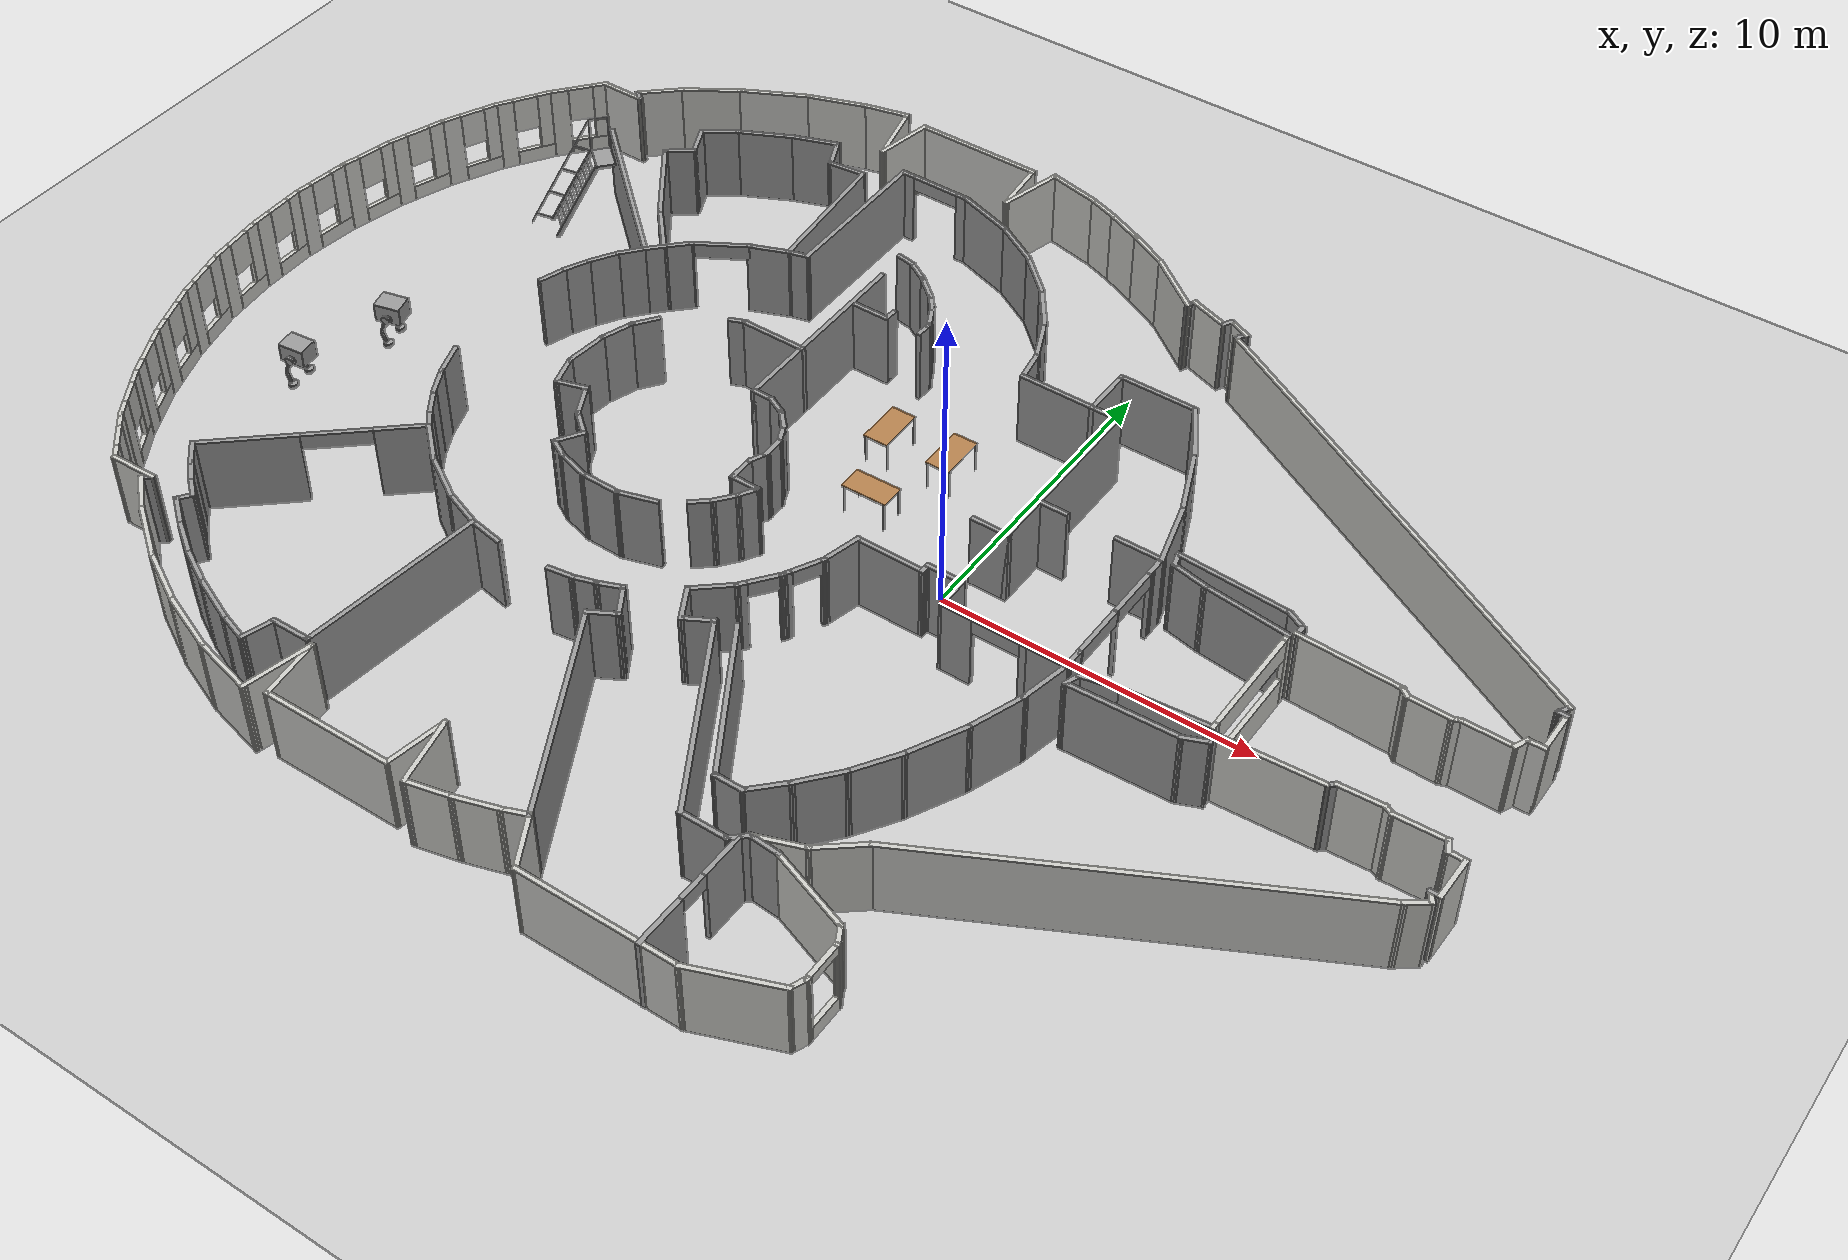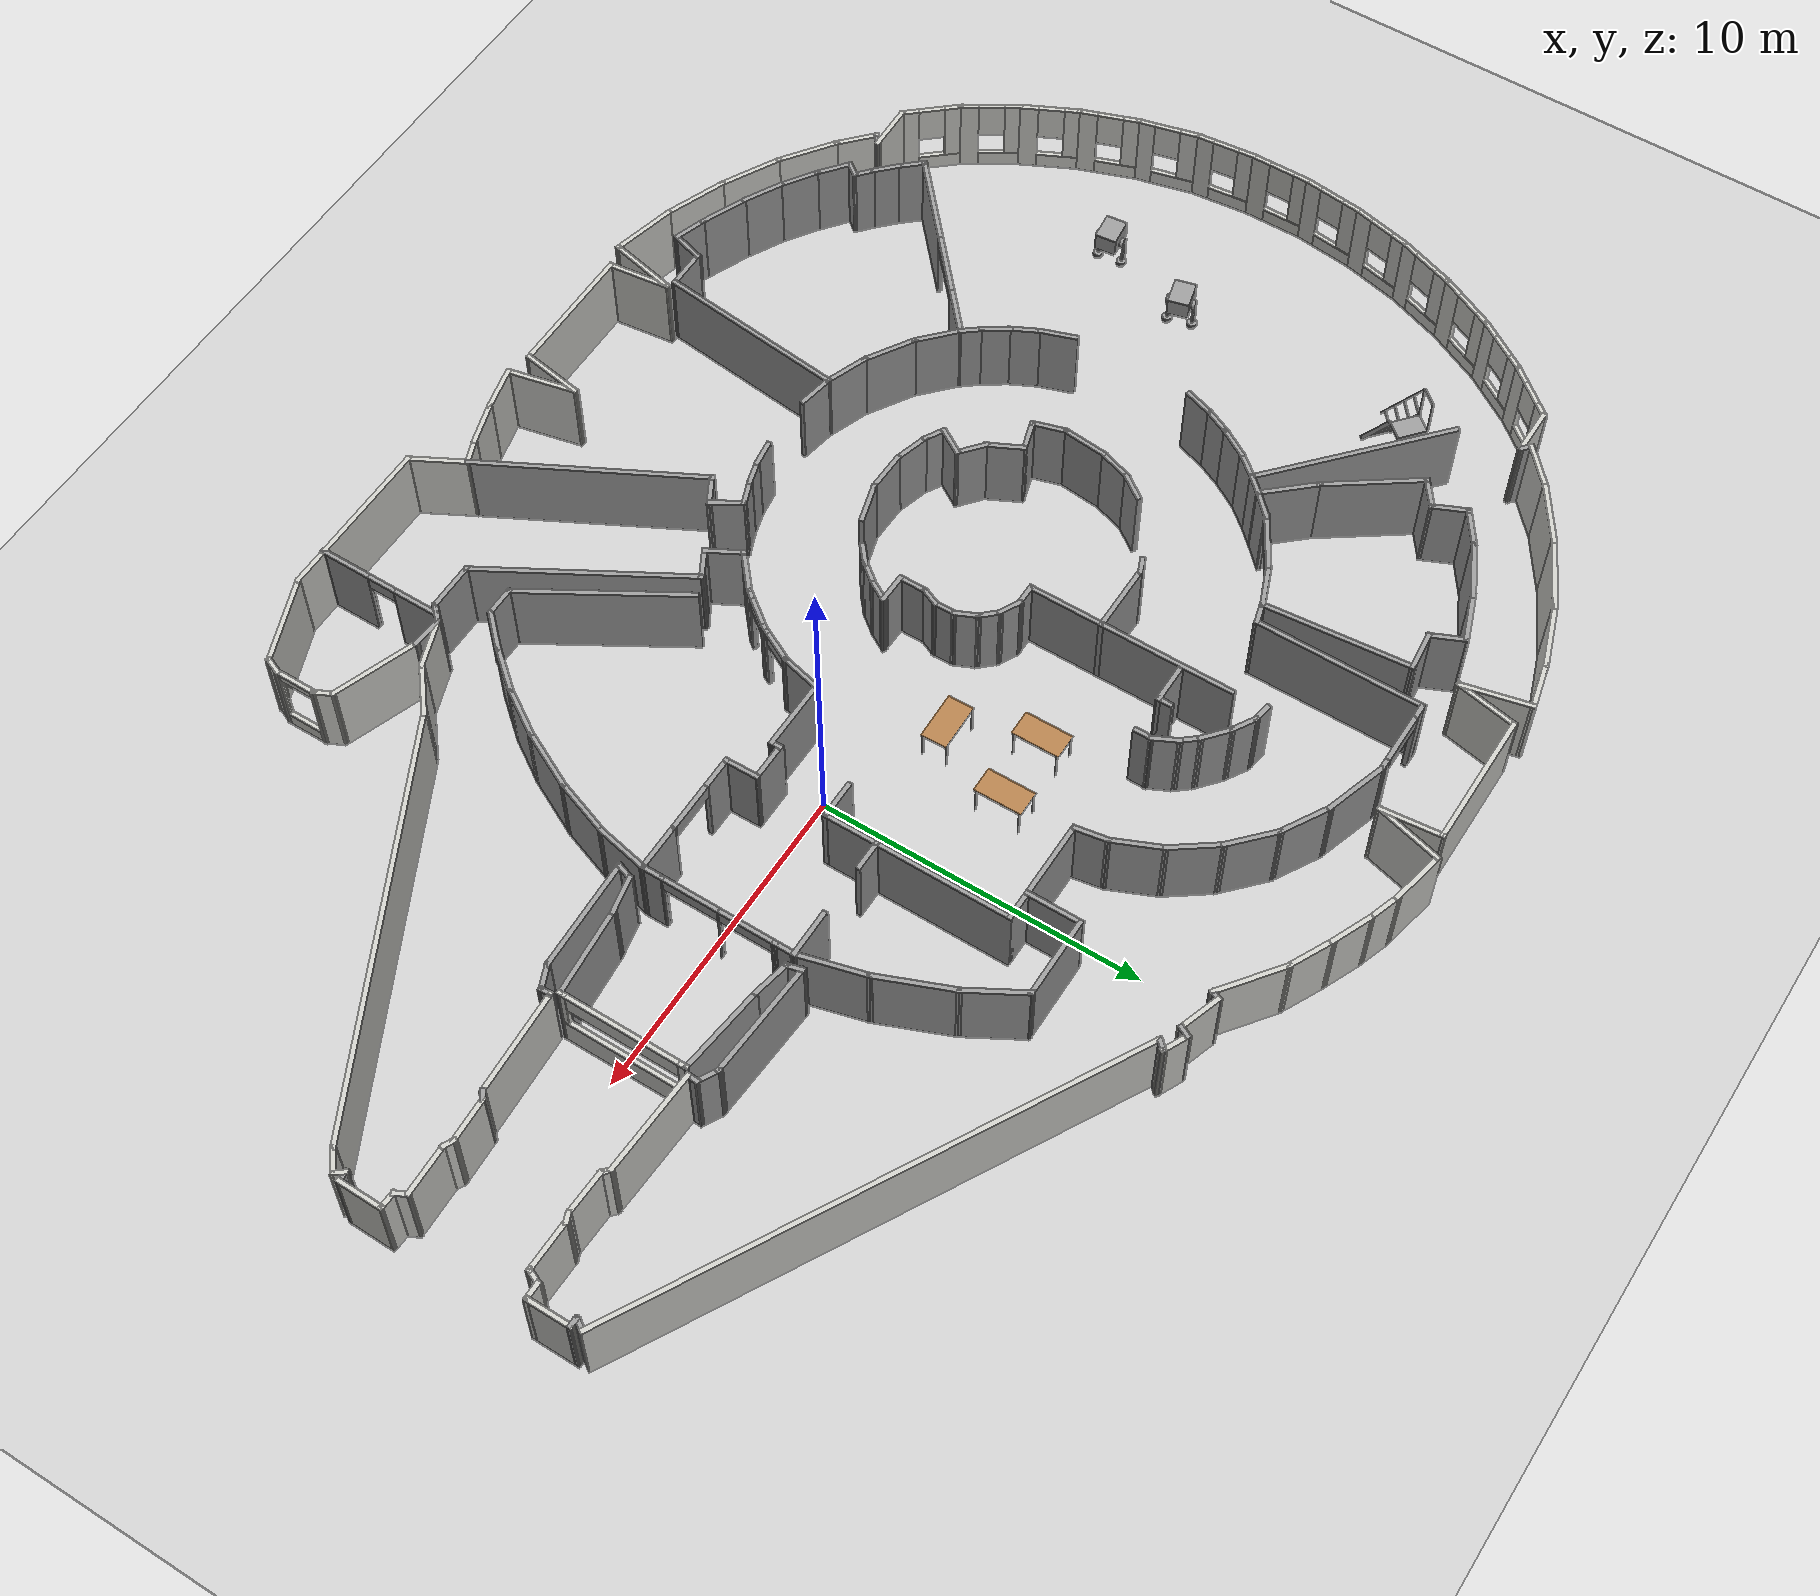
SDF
<sdf version="1.7">
 <world name="default">
  <plugin name="start" filename="libstart.so"/>
  <light name="sun" type="directional">
   <pose>0 0 10 0 -0 0</pose>
   <diffuse>0.8 0.8 0.8 1</diffuse>
   <specular>0.2 0.2 0.2 1</specular>
   <attenuation>
    <range>1000</range>
    <constant>0.9</constant>
    <linear>0.01</linear>
    <quadratic>0.001</quadratic>
   </attenuation>
   <direction>-0.5 0.1 -0.9</direction>
   <spot><inner_angle>0</inner_angle><outer_angle>0</outer_angle><falloff>0</falloff></spot>
  </light>
  <model name="ground_plane">
   <static>1</static>
   <link name="link">
    <collision name="collision">
     <geometry><plane><normal>0 0 1</normal><size>100 100</size></plane></geometry>
     <surface>
      <contact><collide_bitmask>65535</collide_bitmask></contact>
      <friction><ode><mu>100</mu><mu2>50</mu2></ode></friction>
     </surface>
    </collision>
    <visual name="visual">
     <cast_shadows>0</cast_shadows>
     <geometry><plane><normal>0 0 1</normal><size>100 100</size></plane></geometry>
     <material>
      <script><uri>file://media/materials/scripts/gazebo.material</uri><name>Gazebo/Grey</name></script>
     </material>
    </visual>
   </link>
  </model>
  <gravity>0 0 -9.8</gravity>
  <magnetic_field>6e-06 2.3e-05 -4.2e-05</magnetic_field>
  <atmosphere type="adiabatic"/>
  <physics type="ode">
   <max_step_size>0.001</max_step_size>
   <real_time_factor>1</real_time_factor>
   <real_time_update_rate>1000</real_time_update_rate>
  </physics>
  <scene><ambient>0.4 0.4 0.4 1</ambient><background>0.7 0.7 0.7 1</background><shadows>1</shadows></scene>
  <audio><device>default</device></audio>
  <spherical_coordinates>
   <surface_model>EARTH_WGS84</surface_model>
   <latitude_deg>0</latitude_deg>
   <longitude_deg>0</longitude_deg>
   <elevation>0</elevation>
   <heading_deg>0</heading_deg>
  </spherical_coordinates>
  <model name="model">
   <pose>-4.1341 -0.05921 0 0 -0 0</pose>
   <link name="Wall_10">
    <collision name="Wall_10_Collision">
     <geometry><box><size>1.42547 0.15 2.5</size></box></geometry>
     <pose>0 0 1.25 0 -0 0</pose>
    </collision>
    <visual name="Wall_10_Visual">
     <pose>0 0 1.25 0 -0 0</pose>
     <geometry><box><size>1.42547 0.15 2.5</size></box></geometry>
     <material>
      <script><uri>file://media/materials/scripts/gazebo.material</uri><name>Gazebo/CeilingTiled</name></script>
      <ambient>1 1 1 1</ambient>
     </material>
     <meta><layer>0</layer></meta>
    </visual>
    <pose>17.742 2.04987 0 0 -0 3.11021</pose>
   </link>
   <link name="Wall_101">
    <collision name="Wall_101_Collision">
     <geometry><box><size>0.462824 0.15 2.5</size></box></geometry>
     <pose>0 0 1.25 0 -0 0</pose>
    </collision>
    <visual name="Wall_101_Visual">
     <pose>0 0 1.25 0 -0 0</pose>
     <geometry><box><size>0.462824 0.15 2.5</size></box></geometry>
     <material>
      <script><uri>file://media/materials/scripts/gazebo.material</uri><name>Gazebo/Grey</name></script>
      <ambient>1 1 1 1</ambient>
     </material>
     <meta><layer>0</layer></meta>
    </visual>
    <pose>-15.2732 11.179 0 0 -0 2.42042</pose>
   </link>
   <link name="Wall_102">
    <collision name="Wall_102_Collision">
     <geometry><box><size>1.56641 0.15 2.5</size></box></geometry>
     <pose>0 0 1.25 0 -0 0</pose>
    </collision>
    <visual name="Wall_102_Visual">
     <pose>0 0 1.25 0 -0 0</pose>
     <geometry><box><size>1.56641 0.15 2.5</size></box></geometry>
     <material>
      <script><uri>file://media/materials/scripts/gazebo.material</uri><name>Gazebo/CeilingTiled</name></script>
      <ambient>0.964706 1 0.972549 1</ambient>
     </material>
     <meta><layer>0</layer></meta>
    </visual>
    <pose>-14.8674 11.7595 0 0 -0 0.739454</pose>
   </link>
   <link name="Wall_103">
    <collision name="Wall_103_Collision">
     <geometry><box><size>2.03182 0.15 2.5</size></box></geometry>
     <pose>0 0 1.25 0 -0 0</pose>
    </collision>
    <visual name="Wall_103_Visual">
     <pose>0 0 1.25 0 -0 0</pose>
     <geometry><box><size>2.03182 0.15 2.5</size></box></geometry>
     <material>
      <script><uri>file://media/materials/scripts/gazebo.material</uri><name>Gazebo/CeilingTiled</name></script>
      <ambient>0.964706 1 0.972549 1</ambient>
     </material>
     <meta><layer>0</layer></meta>
    </visual>
    <pose>-13.5621 12.76 0 0 -0 0.589698</pose>
   </link>
   <link name="Wall_104">
    <collision name="Wall_104_Collision">
     <geometry><box><size>2.39757 0.15 2.5</size></box></geometry>
     <pose>0 0 1.25 0 -0 0</pose>
    </collision>
    <visual name="Wall_104_Visual">
     <pose>0 0 1.25 0 -0 0</pose>
     <geometry><box><size>2.39757 0.15 2.5</size></box></geometry>
     <material>
      <script><uri>file://media/materials/scripts/gazebo.material</uri><name>Gazebo/CeilingTiled</name></script>
      <ambient>0.964706 1 0.972549 1</ambient>
     </material>
     <meta><layer>0</layer></meta>
    </visual>
    <pose>-11.7796 13.795 0 0 -0 0.472801</pose>
   </link>
   <link name="Wall_106">
    <collision name="Wall_106_Collision">
     <geometry><box><size>2.09081 0.15 2.5</size></box></geometry>
     <pose>0 0 1.25 0 -0 0</pose>
    </collision>
    <visual name="Wall_106_Visual">
     <pose>0 0 1.25 0 -0 0</pose>
     <geometry><box><size>2.09081 0.15 2.5</size></box></geometry>
     <material>
      <script><uri>file://media/materials/scripts/gazebo.material</uri><name>Gazebo/CeilingTiled</name></script>
      <ambient>0.964706 1 0.972549 1</ambient>
     </material>
     <meta><layer>0</layer></meta>
    </visual>
    <pose>-9.86354 14.6283 0 0 -0 0.337731</pose>
   </link>
   <link name="Wall_107">
    <collision name="Wall_107_Collision">
     <geometry><box><size>1.57879 0.15 2.5</size></box></geometry>
     <pose>0 0 1.25 0 -0 0</pose>
    </collision>
    <visual name="Wall_107_Visual">
     <pose>0 0 1.25 0 -0 0</pose>
     <geometry><box><size>1.57879 0.15 2.5</size></box></geometry>
     <material>
      <script><uri>file://media/materials/scripts/gazebo.material</uri><name>Gazebo/CeilingTiled</name></script>
      <ambient>0.964706 1 0.972549 1</ambient>
     </material>
     <meta><layer>0</layer></meta>
    </visual>
    <pose>-8.2523 15.1124 0 0 -0 0.229576</pose>
   </link>
   <link name="Wall_108">
    <collision name="Wall_108_Collision">
     <geometry><box><size>2.19881 0.15 2.5</size></box></geometry>
     <pose>0 0 1.25 0 -0 0</pose>
    </collision>
    <visual name="Wall_108_Visual">
     <pose>0 0 1.25 0 -0 0</pose>
     <geometry><box><size>2.19881 0.15 2.5</size></box></geometry>
     <material>
      <script><uri>file://media/materials/scripts/gazebo.material</uri><name>Gazebo/CeilingTiled</name></script>
      <ambient>0.964706 1 0.972549 1</ambient>
     </material>
     <meta><layer>0</layer></meta>
    </visual>
    <pose>-7.32602 14.2769 0 0 -0 -1.34372</pose>
   </link>
   <link name="Wall_109">
    <collision name="Wall_109_Collision">
     <geometry><box><size>1.99778 0.15 2.5</size></box></geometry>
     <pose>0 0 1.25 0 -0 0</pose>
    </collision>
    <visual name="Wall_109_Visual">
     <pose>0 0 1.25 0 -0 0</pose>
     <geometry><box><size>1.99778 0.15 2.5</size></box></geometry>
     <material>
      <script><uri>file://media/materials/scripts/gazebo.material</uri><name>Gazebo/CeilingTiled</name></script>
      <ambient>0.964706 1 0.972549 1</ambient>
     </material>
     <meta><layer>0</layer></meta>
    </visual>
    <pose>-6.92148 14.1861 0 0 -0 1.38143</pose>
   </link>
   <link name="Wall_11">
    <collision name="Wall_11_Collision">
     <geometry><box><size>0.422349 0.15 2.5</size></box></geometry>
     <pose>0 0 1.25 0 -0 0</pose>
    </collision>
    <visual name="Wall_11_Visual">
     <pose>0 0 1.25 0 -0 0</pose>
     <geometry><box><size>0.422349 0.15 2.5</size></box></geometry>
     <material>
      <script><uri>file://media/materials/scripts/gazebo.material</uri><name>Gazebo/CeilingTiled</name></script>
      <ambient>1 1 1 1</ambient>
     </material>
     <meta><layer>0</layer></meta>
    </visual>
    <pose>16.9987 2.15564 0 0 -0 2.46029</pose>
   </link>
   <link name="Wall_111">
    <collision name="Wall_111_Collision">
     <geometry><box><size>4.25 0.15 2.5</size></box></geometry>
     <pose>0 0 1.25 0 -0 0</pose>
    </collision>
    <visual name="Wall_111_Visual">
     <pose>0 0 1.25 0 -0 0</pose>
     <geometry><box><size>4.25 0.15 2.5</size></box></geometry>
     <material>
      <script><uri>file://media/materials/scripts/gazebo.material</uri><name>Gazebo/CeilingTiled</name></script>
      <ambient>0.964706 1 0.972549 1</ambient>
     </material>
     <meta><layer>0</layer></meta>
    </visual>
    <pose>-4.69757 15.0935 0 0 -0 0</pose>
   </link>
   <link name="Wall_112">
    <collision name="Wall_112_Collision">
     <geometry><box><size>1.93197 0.15 2.5</size></box></geometry>
     <pose>0 0 1.25 0 -0 0</pose>
    </collision>
    <visual name="Wall_112_Visual">
     <pose>0 0 1.25 0 -0 0</pose>
     <geometry><box><size>1.93197 0.15 2.5</size></box></geometry>
     <material>
      <script><uri>file://media/materials/scripts/gazebo.material</uri><name>Gazebo/CeilingTiled</name></script>
      <ambient>0.964706 1 0.972549 1</ambient>
     </material>
     <meta><layer>0</layer></meta>
    </visual>
    <pose>-2.56312 14.2065 0 0 -0 -1.47587</pose>
   </link>
   <link name="Wall_113">
    <collision name="Wall_113_Collision">
     <geometry><box><size>2.16942 0.15 2.5</size></box></geometry>
     <pose>0 0 1.25 0 -0 0</pose>
    </collision>
    <visual name="Wall_113_Visual">
     <pose>0 0 1.25 0 -0 0</pose>
     <geometry><box><size>2.16942 0.15 2.5</size></box></geometry>
     <material>
      <script><uri>file://media/materials/scripts/gazebo.material</uri><name>Gazebo/CeilingTiled</name></script>
      <ambient>0.964706 1 0.972549 1</ambient>
     </material>
     <meta><layer>0</layer></meta>
    </visual>
    <pose>-2.22567 14.2971 0 0 -0 1.31753</pose>
   </link>
   <link name="Wall_118">
    <collision name="Wall_118_Collision">
     <geometry><box><size>2.26593 0.15 2.5</size></box></geometry>
     <pose>0 0 1.25 0 -0 0</pose>
    </collision>
    <visual name="Wall_118_Visual">
     <pose>0 0 1.25 0 -0 0</pose>
     <geometry><box><size>2.26593 0.15 2.5</size></box></geometry>
     <material>
      <script><uri>file://media/materials/scripts/gazebo.material</uri><name>Gazebo/CeilingTiled</name></script>
      <ambient>0.964706 1 0.972549 1</ambient>
     </material>
     <meta><layer>0</layer></meta>
    </visual>
    <pose>3.7645 12.9158 0 0 -0 2.50012</pose>
   </link>
   <link name="Wall_119">
    <collision name="Wall_119_Collision">
     <geometry><box><size>1.52296 0.15 2.5</size></box></geometry>
     <pose>0 0 1.25 0 -0 0</pose>
    </collision>
    <visual name="Wall_119_Visual">
     <pose>0 0 1.25 0 -0 0</pose>
     <geometry><box><size>1.52296 0.15 2.5</size></box></geometry>
     <material>
      <script><uri>file://media/materials/scripts/gazebo.material</uri><name>Gazebo/CeilingTiled</name></script>
      <ambient>0.964706 1 0.972549 1</ambient>
     </material>
     <meta><layer>0</layer></meta>
    </visual>
    <pose>2.30059 13.8514 0 0 -0 2.68533</pose>
   </link>
   <link name="Wall_12">
    <collision name="Wall_12_Collision">
     <geometry><box><size>3.29739 0.15 2.5</size></box></geometry>
     <pose>0 0 1.25 0 -0 0</pose>
    </collision>
    <visual name="Wall_12_Visual">
     <pose>0 0 1.25 0 -0 0</pose>
     <geometry><box><size>3.29739 0.15 2.5</size></box></geometry>
     <material>
      <script><uri>file://media/materials/scripts/gazebo.material</uri><name>Gazebo/CeilingTiled</name></script>
      <ambient>0.964706 1 0.972549 1</ambient>
     </material>
     <meta><layer>0</layer></meta>
    </visual>
    <pose>15.3206 2.30716 0 0 -0 3.0998</pose>
   </link>
   <link name="Wall_120">
    <collision name="Wall_120_Collision">
     <geometry><box><size>1.38613 0.15 2.5</size></box></geometry>
     <pose>0 0 1.25 0 -0 0</pose>
    </collision>
    <visual name="Wall_120_Visual">
     <pose>0 0 1.25 0 -0 0</pose>
     <geometry><box><size>1.38613 0.15 2.5</size></box></geometry>
     <material>
      <script><uri>file://media/materials/scripts/gazebo.material</uri><name>Gazebo/CeilingTiled</name></script>
      <ambient>0.964706 1 0.972549 1</ambient>
     </material>
     <meta><layer>0</layer></meta>
    </visual>
    <pose>1.11722 14.3996 0 0 -0 2.73269</pose>
   </link>
   <link name="Wall_121">
    <collision name="Wall_121_Collision">
     <geometry><box><size>1.10172 0.15 2.5</size></box></geometry>
     <pose>0 0 1.25 0 -0 0</pose>
    </collision>
    <visual name="Wall_121_Visual">
     <pose>0 0 1.25 0 -0 0</pose>
     <geometry><box><size>1.10172 0.15 2.5</size></box></geometry>
     <material>
      <script><uri>file://media/materials/scripts/gazebo.material</uri><name>Gazebo/CeilingTiled</name></script>
      <ambient>0.964706 1 0.972549 1</ambient>
     </material>
     <meta><layer>0</layer></meta>
    </visual>
    <pose>0.100208 14.8003 0 0 -0 2.80979</pose>
   </link>
   <link name="Wall_122">
    <collision name="Wall_122_Collision">
     <geometry><box><size>1.79614 0.15 2.5</size></box></geometry>
     <pose>0 0 1.25 0 -0 0</pose>
    </collision>
    <visual name="Wall_122_Visual">
     <pose>0 0 1.25 0 -0 0</pose>
     <geometry><box><size>1.79614 0.15 2.5</size></box></geometry>
     <material>
      <script><uri>file://media/materials/scripts/gazebo.material</uri><name>Gazebo/CeilingTiled</name></script>
      <ambient>0.964706 1 0.972549 1</ambient>
     </material>
     <meta><layer>0</layer></meta>
    </visual>
    <pose>-1.15499 15.1255 0 0 -0 2.93339</pose>
   </link>
   <link name="Wall_124">
    <collision name="Wall_124_Collision">
     <geometry><box><size>0.404275 0.15 2.5</size></box></geometry>
     <pose>0 0 1.25 0 -0 0</pose>
    </collision>
    <visual name="Wall_124_Visual">
     <pose>0 0 1.25 0 -0 0</pose>
     <geometry><box><size>0.404275 0.15 2.5</size></box></geometry>
     <material>
      <script><uri>file://media/materials/scripts/gazebo.material</uri><name>Gazebo/Grey</name></script>
      <ambient>1 1 1 1</ambient>
     </material>
     <meta><layer>0</layer></meta>
    </visual>
    <pose>4.66935 12.3963 0 0 -0 1.10417</pose>
   </link>
   <link name="Wall_125">
    <collision name="Wall_125_Collision">
     <geometry><box><size>1.41013 0.15 2.5</size></box></geometry>
     <pose>0 0 1.25 0 -0 0</pose>
    </collision>
    <visual name="Wall_125_Visual">
     <pose>0 0 1.25 0 -0 0</pose>
     <geometry><box><size>1.41013 0.15 2.5</size></box></geometry>
     <material>
      <script><uri>file://media/materials/scripts/gazebo.material</uri><name>Gazebo/CeilingTiled</name></script>
      <ambient>0.964706 1 0.972549 1</ambient>
     </material>
     <meta><layer>0</layer></meta>
    </visual>
    <pose>5.3239 12.3095 0 0 -0 -0.323648</pose>
   </link>
   <link name="Wall_126">
    <collision name="Wall_126_Collision">
     <geometry><box><size>0.447598 0.15 2.5</size></box></geometry>
     <pose>0 0 1.25 0 -0 0</pose>
    </collision>
    <visual name="Wall_126_Visual">
     <pose>0 0 1.25 0 -0 0</pose>
     <geometry><box><size>0.447598 0.15 2.5</size></box></geometry>
     <material>
      <script><uri>file://media/materials/scripts/gazebo.material</uri><name>Gazebo/Grey</name></script>
      <ambient>1 1 1 1</ambient>
     </material>
     <meta><layer>0</layer></meta>
    </visual>
    <pose>5.98931 12.2414 0 0 -0 1.09579</pose>
   </link>
   <link name="Wall_127">
    <collision name="Wall_127_Collision">
     <geometry><box><size>0.894139 0.15 2.5</size></box></geometry>
     <pose>0 0 1.25 0 -0 0</pose>
    </collision>
    <visual name="Wall_127_Visual">
     <pose>0 0 1.25 0 -0 0</pose>
     <geometry><box><size>0.894139 0.15 2.5</size></box></geometry>
     <material>
      <script><uri>file://media/materials/scripts/gazebo.material</uri><name>Gazebo/CeilingTiled</name></script>
      <ambient>0.964706 1 0.972549 1</ambient>
     </material>
     <meta><layer>0</layer></meta>
    </visual>
    <pose>6.39384 12.215 0 0 -0 -0.440924</pose>
   </link>
   <link name="Wall_128">
    <collision name="Wall_128_Collision">
     <geometry><box><size>0.468928 0.15 2.5</size></box></geometry>
     <pose>0 0 1.25 0 -0 0</pose>
    </collision>
    <visual name="Wall_128_Visual">
     <pose>0 0 1.25 0 -0 0</pose>
     <geometry><box><size>0.468928 0.15 2.5</size></box></geometry>
     <material>
      <script><uri>file://media/materials/scripts/gazebo.material</uri><name>Gazebo/Grey</name></script>
      <ambient>1 1 1 1</ambient>
     </material>
     <meta><layer>0</layer></meta>
    </visual>
    <pose>6.62336 11.9379 0 0 -0 -2.30603</pose>
   </link>
   <link name="Wall_129">
    <collision name="Wall_129_Collision">
     <geometry><box><size>16.2931 0.15 2.5</size></box></geometry>
     <pose>0 0 1.25 0 -0 0</pose>
    </collision>
    <visual name="Wall_129_Visual">
     <pose>0 0 1.25 0 -0 0</pose>
     <geometry><box><size>16.2931 0.15 2.5</size></box></geometry>
     <material>
      <script><uri>file://media/materials/scripts/gazebo.material</uri><name>Gazebo/CeilingTiled</name></script>
      <ambient>0.964706 1 0.972549 1</ambient>
     </material>
     <meta><layer>0</layer></meta>
    </visual>
    <pose>13.6044 7.95817 0 0 -0 -0.498838</pose>
   </link>
   <link name="Wall_13">
    <collision name="Wall_13_Collision">
     <geometry><box><size>0.430684 0.15 2.5</size></box></geometry>
     <pose>0 0 1.25 0 -0 0</pose>
    </collision>
    <visual name="Wall_13_Visual">
     <pose>0 0 1.25 0 -0 0</pose>
     <geometry><box><size>0.430684 0.15 2.5</size></box></geometry>
     <material>
      <script><uri>file://media/materials/scripts/gazebo.material</uri><name>Gazebo/Grey</name></script>
      <ambient>1 1 1 1</ambient>
     </material>
     <meta><layer>0</layer></meta>
    </visual>
    <pose>13.7569 2.51299 0 0 -0 1.50965</pose>
   </link>
   <link name="Wall_135">
    <collision name="Wall_135_Collision">
     <geometry><box><size>6.29486 0.15 2.5</size></box></geometry>
     <pose>0 0 1.25 0 -0 0</pose>
    </collision>
    <visual name="Wall_135_Visual">
     <pose>0 0 1.25 0 -0 0</pose>
     <geometry><box><size>6.29486 0.15 2.5</size></box></geometry>
     <material>
      <script><uri>file://media/materials/scripts/gazebo.material</uri><name>Gazebo/Grey</name></script>
      <ambient>0.929412 0.960784 0.933333 1</ambient>
     </material>
     <meta><layer>0</layer></meta>
    </visual>
    <pose>-12.4823 7.17089 0 0 -0 -0.727536</pose>
   </link>
   <link name="Wall_136">
    <collision name="Wall_136_Collision">
     <geometry><box><size>0.730094 0.15 2.5</size></box></geometry>
     <pose>0 0 1.25 0 -0 0</pose>
    </collision>
    <visual name="Wall_136_Visual">
     <pose>0 0 1.25 0 -0 0</pose>
     <geometry><box><size>0.730094 0.15 2.5</size></box></geometry>
     <material>
      <script><uri>file://media/materials/scripts/gazebo.material</uri><name>Gazebo/Grey</name></script>
      <ambient>1 1 1 1</ambient>
     </material>
     <meta><layer>0</layer></meta>
    </visual>
    <pose>-9.98937 5.33923 0 0 -0 0.817645</pose>
   </link>
   <link name="Wall_139">
    <collision name="Wall_139_Collision">
     <geometry><box><size>0.967544 0.15 2.5</size></box></geometry>
     <pose>0 0 1.25 0 -0 0</pose>
    </collision>
    <visual name="Wall_139_Visual">
     <pose>0 0 1.25 0 -0 0</pose>
     <geometry><box><size>0.967544 0.15 2.5</size></box></geometry>
     <material>
      <script><uri>file://media/materials/scripts/gazebo.material</uri><name>Gazebo/Grey</name></script>
      <ambient>0.929412 0.960784 0.933333 1</ambient>
     </material>
     <meta><layer>0</layer></meta>
    </visual>
    <pose>-10.4508 4.81478 0 0 -0 -2.27001</pose>
   </link>
   <link name="Wall_140">
    <collision name="Wall_140_Collision">
     <geometry><box><size>1.07537 0.15 2.5</size></box></geometry>
     <pose>0 0 1.25 0 -0 0</pose>
    </collision>
    <visual name="Wall_140_Visual">
     <pose>0 0 1.25 0 -0 0</pose>
     <geometry><box><size>1.07537 0.15 2.5</size></box></geometry>
     <material>
      <script><uri>file://media/materials/scripts/gazebo.material</uri><name>Gazebo/Grey</name></script>
      <ambient>0.929412 0.960784 0.933333 1</ambient>
     </material>
     <meta><layer>0</layer></meta>
    </visual>
    <pose>-10.952 4.10518 0 0 -0 -2.11122</pose>
   </link>
   <link name="Wall_141">
    <collision name="Wall_141_Collision">
     <geometry><box><size>0.954554 0.15 2.5</size></box></geometry>
     <pose>0 0 1.25 0 -0 0</pose>
    </collision>
    <visual name="Wall_141_Visual">
     <pose>0 0 1.25 0 -0 0</pose>
     <geometry><box><size>0.954554 0.15 2.5</size></box></geometry>
     <material>
      <script><uri>file://media/materials/scripts/gazebo.material</uri><name>Gazebo/Grey</name></script>
      <ambient>0.929412 0.960784 0.933333 1</ambient>
     </material>
     <meta><layer>0</layer></meta>
    </visual>
    <pose>-11.362 3.34474 0 0 -0 -2.01239</pose>
   </link>
   <link name="Wall_142">
    <collision name="Wall_142_Collision">
     <geometry><box><size>0.998979 0.15 2.5</size></box></geometry>
     <pose>0 0 1.25 0 -0 0</pose>
    </collision>
    <visual name="Wall_142_Visual">
     <pose>0 0 1.25 0 -0 0</pose>
     <geometry><box><size>0.998979 0.15 2.5</size></box></geometry>
     <material>
      <script><uri>file://media/materials/scripts/gazebo.material</uri><name>Gazebo/Grey</name></script>
      <ambient>0.929412 0.960784 0.933333 1</ambient>
     </material>
     <meta><layer>0</layer></meta>
    </visual>
    <pose>-11.6661 2.57769 0 0 -0 -1.88762</pose>
   </link>
   <link name="Wall_144">
    <collision name="Wall_144_Collision">
     <geometry><box><size>1.19979 0.15 2.5</size></box></geometry>
     <pose>0 0 1.25 0 -0 0</pose>
    </collision>
    <visual name="Wall_144_Visual">
     <pose>0 0 1.25 0 -0 0</pose>
     <geometry><box><size>1.19979 0.15 2.5</size></box></geometry>
     <material>
      <script><uri>file://media/materials/scripts/gazebo.material</uri><name>Gazebo/Grey</name></script>
      <ambient>0.929412 0.960784 0.933333 1</ambient>
     </material>
     <meta><layer>0</layer></meta>
    </visual>
    <pose>-11.6485 -2.13121 0 0 -0 -1.23709</pose>
   </link>
   <link name="Wall_145">
    <collision name="Wall_145_Collision">
     <geometry><box><size>1.02535 0.15 2.5</size></box></geometry>
     <pose>0 0 1.25 0 -0 0</pose>
    </collision>
    <visual name="Wall_145_Visual">
     <pose>0 0 1.25 0 -0 0</pose>
     <geometry><box><size>1.02535 0.15 2.5</size></box></geometry>
     <material>
      <script><uri>file://media/materials/scripts/gazebo.material</uri><name>Gazebo/Grey</name></script>
      <ambient>0.929412 0.960784 0.933333 1</ambient>
     </material>
     <meta><layer>0</layer></meta>
    </visual>
    <pose>-11.2782 -3.01729 0 0 -0 -1.10039</pose>
   </link>
   <link name="Wall_146">
    <collision name="Wall_146_Collision">
     <geometry><box><size>0.997329 0.15 2.5</size></box></geometry>
     <pose>0 0 1.25 0 -0 0</pose>
    </collision>
    <visual name="Wall_146_Visual">
     <pose>0 0 1.25 0 -0 0</pose>
     <geometry><box><size>0.997329 0.15 2.5</size></box></geometry>
     <material>
      <script><uri>file://media/materials/scripts/gazebo.material</uri><name>Gazebo/Grey</name></script>
      <ambient>0.929412 0.960784 0.933333 1</ambient>
     </material>
     <meta><layer>0</layer></meta>
    </visual>
    <pose>-10.8418 -3.75789 0 0 -0 -0.974136</pose>
   </link>
   <link name="Wall_147">
    <collision name="Wall_147_Collision">
     <geometry><box><size>0.761361 0.15 2.5</size></box></geometry>
     <pose>0 0 1.25 0 -0 0</pose>
    </collision>
    <visual name="Wall_147_Visual">
     <pose>0 0 1.25 0 -0 0</pose>
     <geometry><box><size>0.761361 0.15 2.5</size></box></geometry>
     <material>
      <script><uri>file://media/materials/scripts/gazebo.material</uri><name>Gazebo/Grey</name></script>
      <ambient>0.929412 0.960784 0.933333 1</ambient>
     </material>
     <meta><layer>0</layer></meta>
    </visual>
    <pose>-10.4119 -4.3464 0 0 -0 -0.892677</pose>
   </link>
   <link name="Wall_149">
    <pose>-12.6849 -6.76582 0 0 -0 -2.4171</pose>
    <visual name="Wall_149_Visual_0">
     <pose>-2.54709 0 1.25 0 -0 0</pose>
     <geometry><box><size>1.63856 0.15 2.5</size></box></geometry>
     <material>
      <script><uri>file://media/materials/scripts/gazebo.material</uri><name>Gazebo/Grey</name></script>
      <ambient>0.929412 0.960784 0.933333 1</ambient>
     </material>
     <meta><layer>0</layer></meta>
    </visual>
    <collision name="Wall_149_Collision_0">
     <geometry><box><size>1.63856 0.15 2.5</size></box></geometry>
     <pose>-2.54709 0 1.25 0 -0 0</pose>
    </collision>
    <visual name="Wall_149_Visual_1">
     <pose>1.84361 0 1.25 0 -0 0</pose>
     <geometry><box><size>3.04552 0.15 2.5</size></box></geometry>
     <material>
      <script><uri>file://media/materials/scripts/gazebo.material</uri><name>Gazebo/Grey</name></script>
      <ambient>0.929412 0.960784 0.933333 1</ambient>
     </material>
     <meta><layer>0</layer></meta>
    </visual>
    <collision name="Wall_149_Collision_1">
     <geometry><box><size>3.04552 0.15 2.5</size></box></geometry>
     <pose>1.84361 0 1.25 0 -0 0</pose>
    </collision>
    <visual name="Wall_149_Visual_2">
     <pose>-0.703479 0 2.25 0 -0 0</pose>
     <geometry><box><size>2.04867 0.15 0.5</size></box></geometry>
     <material>
      <script><uri>file://media/materials/scripts/gazebo.material</uri><name>Gazebo/Grey</name></script>
      <ambient>0.929412 0.960784 0.933333 1</ambient>
     </material>
     <meta><layer>0</layer></meta>
    </visual>
    <collision name="Wall_149_Collision_2">
     <geometry><box><size>2.04867 0.15 0.5</size></box></geometry>
     <pose>-0.703479 0 2.25 0 -0 0</pose>
    </collision>
   </link>
   <link name="Wall_153">
    <collision name="Wall_153_Collision">
     <geometry><box><size>0.953287 0.15 2.5</size></box></geometry>
     <pose>0 0 1.25 0 -0 0</pose>
    </collision>
    <visual name="Wall_153_Visual">
     <pose>0 0 1.25 0 -0 0</pose>
     <geometry><box><size>0.953287 0.15 2.5</size></box></geometry>
     <material>
      <script><uri>file://media/materials/scripts/gazebo.material</uri><name>Gazebo/Grey</name></script>
      <ambient>1 1 1 1</ambient>
     </material>
     <meta><layer>0</layer></meta>
    </visual>
    <pose>-14.8797 -9.24465 0 0 -0 -0.833951</pose>
   </link>
   <link name="Wall_154">
    <collision name="Wall_154_Collision">
     <geometry><box><size>0.912545 0.15 2.5</size></box></geometry>
     <pose>0 0 1.25 0 -0 0</pose>
    </collision>
    <visual name="Wall_154_Visual">
     <pose>0 0 1.25 0 -0 0</pose>
     <geometry><box><size>0.912545 0.15 2.5</size></box></geometry>
     <material>
      <script><uri>file://media/materials/scripts/gazebo.material</uri><name>Gazebo/Grey</name></script>
      <ambient>1 1 1 1</ambient>
     </material>
     <meta><layer>0</layer></meta>
    </visual>
    <pose>-14.3359 -9.80732 0 0 -0 -0.769271</pose>
   </link>
   <link name="Wall_155">
    <collision name="Wall_155_Collision">
     <geometry><box><size>0.730072 0.15 2.5</size></box></geometry>
     <pose>0 0 1.25 0 -0 0</pose>
    </collision>
    <visual name="Wall_155_Visual">
     <pose>0 0 1.25 0 -0 0</pose>
     <geometry><box><size>0.730072 0.15 2.5</size></box></geometry>
     <material>
      <script><uri>file://media/materials/scripts/gazebo.material</uri><name>Gazebo/Grey</name></script>
      <ambient>1 1 1 1</ambient>
     </material>
     <meta><layer>0</layer></meta>
    </visual>
    <pose>-13.8402 -10.2595 0 0 -0 -0.700496</pose>
   </link>
   <link name="Wall_156">
    <collision name="Wall_156_Collision">
     <geometry><box><size>0.603926 0.15 2.5</size></box></geometry>
     <pose>0 0 1.25 0 -0 0</pose>
    </collision>
    <visual name="Wall_156_Visual">
     <pose>0 0 1.25 0 -0 0</pose>
     <geometry><box><size>0.603926 0.15 2.5</size></box></geometry>
     <material>
      <script><uri>file://media/materials/scripts/gazebo.material</uri><name>Gazebo/Grey</name></script>
      <ambient>1 1 1 1</ambient>
     </material>
     <meta><layer>0</layer></meta>
    </visual>
    <pose>-13.7533 -10.6291 0 0 -0 -2.20663</pose>
   </link>
   <link name="Wall_158">
    <collision name="Wall_158_Collision">
     <geometry><box><size>1.18744 0.15 2.5</size></box></geometry>
     <pose>0 0 1.25 0 -0 0</pose>
    </collision>
    <visual name="Wall_158_Visual">
     <pose>0 0 1.25 0 -0 0</pose>
     <geometry><box><size>1.18744 0.15 2.5</size></box></geometry>
     <material>
      <script><uri>file://media/materials/scripts/gazebo.material</uri><name>Gazebo/Grey</name></script>
      <ambient>1 1 1 1</ambient>
     </material>
     <meta><layer>0</layer></meta>
    </visual>
    <pose>-13.4803 -11.1323 0 0 -0 -0.666394</pose>
   </link>
   <link name="Wall_159">
    <collision name="Wall_159_Collision">
     <geometry><box><size>1.33983 0.15 2.5</size></box></geometry>
     <pose>0 0 1.25 0 -0 0</pose>
    </collision>
    <visual name="Wall_159_Visual">
     <pose>0 0 1.25 0 -0 0</pose>
     <geometry><box><size>1.33983 0.15 2.5</size></box></geometry>
     <material>
      <script><uri>file://media/materials/scripts/gazebo.material</uri><name>Gazebo/Grey</name></script>
      <ambient>1 1 1 1</ambient>
     </material>
     <meta><layer>0</layer></meta>
    </visual>
    <pose>-12.5776 -11.783 0 0 -0 -0.588003</pose>
   </link>
   <link name="Wall_16">
    <collision name="Wall_16_Collision">
     <geometry><box><size>0.771179 0.15 2.5</size></box></geometry>
     <pose>0 0 1.25 0 -0 0</pose>
    </collision>
    <visual name="Wall_16_Visual">
     <pose>0 0 1.25 0 -0 0</pose>
     <geometry><box><size>0.771179 0.15 2.5</size></box></geometry>
     <material>
      <script><uri>file://media/materials/scripts/gazebo.material</uri><name>Gazebo/Grey</name></script>
      <ambient>1 1 1 1</ambient>
     </material>
     <meta><layer>0</layer></meta>
    </visual>
    <pose>13.4901 2.7968 0 0 -0 2.6605</pose>
   </link>
   <link name="Wall_160">
    <collision name="Wall_160_Collision">
     <geometry><box><size>1.37119 0.15 2.5</size></box></geometry>
     <pose>0 0 1.25 0 -0 0</pose>
    </collision>
    <visual name="Wall_160_Visual">
     <pose>0 0 1.25 0 -0 0</pose>
     <geometry><box><size>1.37119 0.15 2.5</size></box></geometry>
     <material>
      <script><uri>file://media/materials/scripts/gazebo.material</uri><name>Gazebo/Grey</name></script>
      <ambient>1 1 1 1</ambient>
     </material>
     <meta><layer>0</layer></meta>
    </visual>
    <pose>-11.5426 -12.398 0 0 -0 -0.485622</pose>
   </link>
   <link name="Wall_161">
    <collision name="Wall_161_Collision">
     <geometry><box><size>1.62462 0.15 2.5</size></box></geometry>
     <pose>0 0 1.25 0 -0 0</pose>
    </collision>
    <visual name="Wall_161_Visual">
     <pose>0 0 1.25 0 -0 0</pose>
     <geometry><box><size>1.62462 0.15 2.5</size></box></geometry>
     <material>
      <script><uri>file://media/materials/scripts/gazebo.material</uri><name>Gazebo/Grey</name></script>
      <ambient>1 1 1 1</ambient>
     </material>
     <meta><layer>0</layer></meta>
    </visual>
    <pose>-10.3226 -12.968 0 0 -0 -0.396878</pose>
   </link>
   <link name="Wall_162">
    <collision name="Wall_162_Collision">
     <geometry><box><size>1.11768 0.15 2.5</size></box></geometry>
     <pose>0 0 1.25 0 -0 0</pose>
    </collision>
    <visual name="Wall_162_Visual">
     <pose>0 0 1.25 0 -0 0</pose>
     <geometry><box><size>1.11768 0.15 2.5</size></box></geometry>
     <material>
      <script><uri>file://media/materials/scripts/gazebo.material</uri><name>Gazebo/Grey</name></script>
      <ambient>1 1 1 1</ambient>
     </material>
     <meta><layer>0</layer></meta>
    </visual>
    <pose>-9.18259 -13.403 0 0 -0 -0.315215</pose>
   </link>
   <link name="Wall_163">
    <collision name="Wall_163_Collision">
     <geometry><box><size>1.12124 0.15 2.5</size></box></geometry>
     <pose>0 0 1.25 0 -0 0</pose>
    </collision>
    <visual name="Wall_163_Visual">
     <pose>0 0 1.25 0 -0 0</pose>
     <geometry><box><size>1.12124 0.15 2.5</size></box></geometry>
     <material>
      <script><uri>file://media/materials/scripts/gazebo.material</uri><name>Gazebo/Grey</name></script>
      <ambient>1 1 1 1</ambient>
     </material>
     <meta><layer>0</layer></meta>
    </visual>
    <pose>-8.58259 -13.088 0 0 -0 1.27835</pose>
   </link>
   <link name="Wall_164">
    <collision name="Wall_164_Collision">
     <geometry><box><size>1.33004 0.15 2.5</size></box></geometry>
     <pose>0 0 1.25 0 -0 0</pose>
    </collision>
    <visual name="Wall_164_Visual">
     <pose>0 0 1.25 0 -0 0</pose>
     <geometry><box><size>1.33004 0.15 2.5</size></box></geometry>
     <material>
      <script><uri>file://media/materials/scripts/gazebo.material</uri><name>Gazebo/Grey</name></script>
      <ambient>1 1 1 1</ambient>
     </material>
     <meta><layer>0</layer></meta>
    </visual>
    <pose>-7.85259 -12.618 0 0 -0 0.008474</pose>
   </link>
   <link name="Wall_166">
    <collision name="Wall_166_Collision">
     <geometry><box><size>5.98967 0.15 2.5</size></box></geometry>
     <pose>0 0 1.25 0 -0 0</pose>
    </collision>
    <visual name="Wall_166_Visual">
     <pose>0 0 1.25 0 -0 0</pose>
     <geometry><box><size>5.98967 0.15 2.5</size></box></geometry>
     <material>
      <script><uri>file://media/materials/scripts/gazebo.material</uri><name>Gazebo/Grey</name></script>
      <ambient>1 1 1 1</ambient>
     </material>
     <meta><layer>0</layer></meta>
    </visual>
    <pose>-6.94415 -9.71055 0 0 -0 1.46152</pose>
   </link>
   <link name="Wall_167">
    <collision name="Wall_167_Collision">
     <geometry><box><size>1.20017 0.15 2.5</size></box></geometry>
     <pose>0 0 1.25 0 -0 0</pose>
    </collision>
    <visual name="Wall_167_Visual">
     <pose>0 0 1.25 0 -0 0</pose>
     <geometry><box><size>1.20017 0.15 2.5</size></box></geometry>
     <material>
      <script><uri>file://media/materials/scripts/gazebo.material</uri><name>Gazebo/Grey</name></script>
      <ambient>1 1 1 1</ambient>
     </material>
     <meta><layer>0</layer></meta>
    </visual>
    <pose>-6.10861 -6.89938 0 0 -0 -0.174672</pose>
   </link>
   <link name="Wall_169">
    <collision name="Wall_169_Collision">
     <geometry><box><size>1.45339 0.15 2.5</size></box></geometry>
     <pose>0 0 1.25 0 -0 0</pose>
    </collision>
    <visual name="Wall_169_Visual">
     <pose>0 0 1.25 0 -0 0</pose>
     <geometry><box><size>1.45339 0.15 2.5</size></box></geometry>
     <material>
      <script><uri>file://media/materials/scripts/gazebo.material</uri><name>Gazebo/Grey</name></script>
      <ambient>1 1 1 1</ambient>
     </material>
     <meta><layer>0</layer></meta>
    </visual>
    <pose>-7.23666 -6.58131 0 0 -0 2.7861</pose>
   </link>
   <link name="Wall_17">
    <collision name="Wall_17_Collision">
     <geometry><box><size>3.65354 0.15 2.5</size></box></geometry>
     <pose>0 0 1.25 0 -0 0</pose>
    </collision>
    <visual name="Wall_17_Visual">
     <pose>0 0 1.25 0 -0 0</pose>
     <geometry><box><size>3.65354 0.15 2.5</size></box></geometry>
     <material>
      <script><uri>file://media/materials/scripts/gazebo.material</uri><name>Gazebo/Grey</name></script>
      <ambient>1 1 1 1</ambient>
     </material>
     <meta><layer>0</layer></meta>
    </visual>
    <pose>11.4658 3.03915 0 0 -0 3.08526</pose>
   </link>
   <link name="Wall_170">
    <collision name="Wall_170_Collision">
     <geometry><box><size>1.74678 0.15 2.5</size></box></geometry>
     <pose>0 0 1.25 0 -0 0</pose>
    </collision>
    <visual name="Wall_170_Visual">
     <pose>0 0 1.25 0 -0 0</pose>
     <geometry><box><size>1.74678 0.15 2.5</size></box></geometry>
     <material>
      <script><uri>file://media/materials/scripts/gazebo.material</uri><name>Gazebo/Grey</name></script>
      <ambient>1 1 1 1</ambient>
     </material>
     <meta><layer>0</layer></meta>
    </visual>
    <pose>-8.52869 -5.93789 0 0 -0 2.59265</pose>
   </link>
   <link name="Wall_171">
    <collision name="Wall_171_Collision">
     <geometry><box><size>1.49778 0.15 2.5</size></box></geometry>
     <pose>0 0 1.25 0 -0 0</pose>
    </collision>
    <visual name="Wall_171_Visual">
     <pose>0 0 1.25 0 -0 0</pose>
     <geometry><box><size>1.49778 0.15 2.5</size></box></geometry>
     <material>
      <script><uri>file://media/materials/scripts/gazebo.material</uri><name>Gazebo/Grey</name></script>
      <ambient>1 1 1 1</ambient>
     </material>
     <meta><layer>0</layer></meta>
    </visual>
    <pose>-9.70572 -5.06504 0 0 -0 2.39784</pose>
   </link>
   <link name="Wall_173">
    <collision name="Wall_173_Collision">
     <geometry><box><size>0.887742 0.15 2.5</size></box></geometry>
     <pose>0 0 1.25 0 -0 0</pose>
    </collision>
    <visual name="Wall_173_Visual">
     <pose>0 0 1.25 0 -0 0</pose>
     <geometry><box><size>0.887742 0.15 2.5</size></box></geometry>
     <material>
      <script><uri>file://media/materials/scripts/gazebo.material</uri><name>Gazebo/Grey</name></script>
      <ambient>1 1 1 1</ambient>
     </material>
     <meta><layer>0</layer></meta>
    </visual>
    <pose>-3.43446 -6.9344 0 0 -0 0.144812</pose>
   </link>
   <link name="Wall_174">
    <collision name="Wall_174_Collision">
     <geometry><box><size>0.847782 0.15 2.5</size></box></geometry>
     <pose>0 0 1.25 0 -0 0</pose>
    </collision>
    <visual name="Wall_174_Visual">
     <pose>0 0 1.25 0 -0 0</pose>
     <geometry><box><size>0.847782 0.15 2.5</size></box></geometry>
     <material>
      <script><uri>file://media/materials/scripts/gazebo.material</uri><name>Gazebo/Grey</name></script>
      <ambient>1 1 1 1</ambient>
     </material>
     <meta><layer>0</layer></meta>
    </visual>
    <pose>-2.73486 -6.78231 0 0 -0 0.287281</pose>
   </link>
   <link name="Wall_175">
    <collision name="Wall_175_Collision">
     <geometry><box><size>0.887115 0.15 2.5</size></box></geometry>
     <pose>0 0 1.25 0 -0 0</pose>
    </collision>
    <visual name="Wall_175_Visual">
     <pose>0 0 1.25 0 -0 0</pose>
     <geometry><box><size>0.887115 0.15 2.5</size></box></geometry>
     <material>
      <script><uri>file://media/materials/scripts/gazebo.material</uri><name>Gazebo/Grey</name></script>
      <ambient>1 1 1 1</ambient>
     </material>
     <meta><layer>0</layer></meta>
    </visual>
    <pose>-2.05807 -6.54657 0 0 -0 0.380506</pose>
   </link>
   <link name="Wall_176">
    <collision name="Wall_176_Collision">
     <geometry><box><size>1.13341 0.15 2.5</size></box></geometry>
     <pose>0 0 1.25 0 -0 0</pose>
    </collision>
    <visual name="Wall_176_Visual">
     <pose>0 0 1.25 0 -0 0</pose>
     <geometry><box><size>1.13341 0.15 2.5</size></box></geometry>
     <material>
      <script><uri>file://media/materials/scripts/gazebo.material</uri><name>Gazebo/Grey</name></script>
      <ambient>1 1 1 1</ambient>
     </material>
     <meta><layer>0</layer></meta>
    </visual>
    <pose>-1.45732 -6.82794 0 0 -0 -1.01711</pose>
   </link>
   <link name="Wall_177">
    <collision name="Wall_177_Collision">
     <geometry><box><size>1.02156 0.15 2.5</size></box></geometry>
     <pose>0 0 1.25 0 -0 0</pose>
    </collision>
    <visual name="Wall_177_Visual">
     <pose>0 0 1.25 0 -0 0</pose>
     <geometry><box><size>1.02156 0.15 2.5</size></box></geometry>
     <material>
      <script><uri>file://media/materials/scripts/gazebo.material</uri><name>Gazebo/Grey</name></script>
      <ambient>1 1 1 1</ambient>
     </material>
     <meta><layer>0</layer></meta>
    </visual>
    <pose>-1.57899 -7.4591 0 0 -0 -2.6311</pose>
   </link>
   <link name="Wall_18">
    <collision name="Wall_18_Collision">
     <geometry><box><size>0.585403 0.15 2.5</size></box></geometry>
     <pose>0 0 1.25 0 -0 0</pose>
    </collision>
    <visual name="Wall_18_Visual">
     <pose>0 0 1.25 0 -0 0</pose>
     <geometry><box><size>0.585403 0.15 2.5</size></box></geometry>
     <material>
      <script><uri>file://media/materials/scripts/gazebo.material</uri><name>Gazebo/Grey</name></script>
      <ambient>1 1 1 1</ambient>
     </material>
     <meta><layer>0</layer></meta>
    </visual>
    <pose>9.77269 2.92737 0 0 -0 -1.31117</pose>
   </link>
   <link name="Wall_180">
    <collision name="Wall_180_Collision">
     <geometry><box><size>7.09459 0.15 2.5</size></box></geometry>
     <pose>0 0 1.25 0 -0 0</pose>
    </collision>
    <visual name="Wall_180_Visual">
     <pose>0 0 1.25 0 -0 0</pose>
     <geometry><box><size>7.09459 0.15 2.5</size></box></geometry>
     <material>
      <script><uri>file://media/materials/scripts/gazebo.material</uri><name>Gazebo/Grey</name></script>
      <ambient>1 1 1 1</ambient>
     </material>
     <meta><layer>0</layer></meta>
    </visual>
    <pose>-0.326679 -10.7366 0 0 -0 -1.08132</pose>
   </link>
   <link name="Wall_182">
    <collision name="Wall_182_Collision">
     <geometry><box><size>1.35009 0.15 2.5</size></box></geometry>
     <pose>0 0 1.25 0 -0 0</pose>
    </collision>
    <visual name="Wall_182_Visual">
     <pose>0 0 1.25 0 -0 0</pose>
     <geometry><box><size>1.35009 0.15 2.5</size></box></geometry>
     <material>
      <script><uri>file://media/materials/scripts/gazebo.material</uri><name>Gazebo/Grey</name></script>
      <ambient>1 1 1 1</ambient>
     </material>
     <meta><layer>0</layer></meta>
    </visual>
    <pose>2.18096 -1.91168 0 0 -0 -1.80764</pose>
   </link>
   <link name="Wall_183">
    <pose>1.75857 -3.03804 0 0 -0 -2.04915</pose>
    <visual name="Wall_183_Visual_0">
     <pose>-0.599077 0 1.25 0 -0 0</pose>
     <geometry><box><size>0.175306 0.15 2.5</size></box></geometry>
     <material>
      <script><uri>file://media/materials/scripts/gazebo.material</uri><name>Gazebo/Grey</name></script>
      <ambient>1 1 1 1</ambient>
     </material>
     <meta><layer>0</layer></meta>
    </visual>
    <collision name="Wall_183_Collision_0">
     <geometry><box><size>0.175306 0.15 2.5</size></box></geometry>
     <pose>-0.599077 0 1.25 0 -0 0</pose>
    </collision>
    <visual name="Wall_183_Visual_1">
     <pose>0.537653 0 1.25 0 -0 0</pose>
     <geometry><box><size>0.298155 0.15 2.5</size></box></geometry>
     <material>
      <script><uri>file://media/materials/scripts/gazebo.material</uri><name>Gazebo/Grey</name></script>
      <ambient>1 1 1 1</ambient>
     </material>
     <meta><layer>0</layer></meta>
    </visual>
    <collision name="Wall_183_Collision_1">
     <geometry><box><size>0.298155 0.15 2.5</size></box></geometry>
     <pose>0.537653 0 1.25 0 -0 0</pose>
    </collision>
    <visual name="Wall_183_Visual_2">
     <pose>-0.061425 0 2.25 0 -0 0</pose>
     <geometry><box><size>0.9 0.15 0.5</size></box></geometry>
     <material>
      <script><uri>file://media/materials/scripts/gazebo.material</uri><name>Gazebo/Grey</name></script>
      <ambient>1 1 1 1</ambient>
     </material>
     <meta><layer>0</layer></meta>
    </visual>
    <collision name="Wall_183_Collision_2">
     <geometry><box><size>0.9 0.15 0.5</size></box></geometry>
     <pose>-0.061425 0 2.25 0 -0 0</pose>
    </collision>
   </link>
   <link name="Wall_184">
    <pose>1.08477 -4.094 0 0 -0 -2.22364</pose>
    <visual name="Wall_184_Visual_0">
     <pose>-0.623774 0 1.25 0 -0 0</pose>
     <geometry><box><size>0.193801 0.15 2.5</size></box></geometry>
     <material>
      <script><uri>file://media/materials/scripts/gazebo.material</uri><name>Gazebo/Grey</name></script>
      <ambient>1 1 1 1</ambient>
     </material>
     <meta><layer>0</layer></meta>
    </visual>
    <collision name="Wall_184_Collision_0">
     <geometry><box><size>0.193801 0.15 2.5</size></box></geometry>
     <pose>-0.623774 0 1.25 0 -0 0</pose>
    </collision>
    <visual name="Wall_184_Visual_1">
     <pose>0.5469 0 1.25 0 -0 0</pose>
     <geometry><box><size>0.347547 0.15 2.5</size></box></geometry>
     <material>
      <script><uri>file://media/materials/scripts/gazebo.material</uri><name>Gazebo/Grey</name></script>
      <ambient>1 1 1 1</ambient>
     </material>
     <meta><layer>0</layer></meta>
    </visual>
    <collision name="Wall_184_Collision_1">
     <geometry><box><size>0.347547 0.15 2.5</size></box></geometry>
     <pose>0.5469 0 1.25 0 -0 0</pose>
    </collision>
    <visual name="Wall_184_Visual_2">
     <pose>-0.076873 0 2.25 0 -0 0</pose>
     <geometry><box><size>0.9 0.15 0.5</size></box></geometry>
     <material>
      <script><uri>file://media/materials/scripts/gazebo.material</uri><name>Gazebo/Grey</name></script>
      <ambient>1 1 1 1</ambient>
     </material>
     <meta><layer>0</layer></meta>
    </visual>
    <collision name="Wall_184_Collision_2">
     <geometry><box><size>0.9 0.15 0.5</size></box></geometry>
     <pose>-0.076873 0 2.25 0 -0 0</pose>
    </collision>
   </link>
   <link name="Wall_185">
    <collision name="Wall_185_Collision">
     <geometry><box><size>1.4602 0.15 2.5</size></box></geometry>
     <pose>0 0 1.25 0 -0 0</pose>
    </collision>
    <visual name="Wall_185_Visual">
     <pose>0 0 1.25 0 -0 0</pose>
     <geometry><box><size>1.4602 0.15 2.5</size></box></geometry>
     <material>
      <script><uri>file://media/materials/scripts/gazebo.material</uri><name>Gazebo/Grey</name></script>
      <ambient>1 1 1 1</ambient>
     </material>
     <meta><layer>0</layer></meta>
    </visual>
    <pose>0.196945 -5.0353 0 0 -0 -2.4288</pose>
   </link>
   <link name="Wall_187">
    <collision name="Wall_187_Collision">
     <geometry><box><size>1.24375 0.15 2.5</size></box></geometry>
     <pose>0 0 1.25 0 -0 0</pose>
    </collision>
    <visual name="Wall_187_Visual">
     <pose>0 0 1.25 0 -0 0</pose>
     <geometry><box><size>1.24375 0.15 2.5</size></box></geometry>
     <material>
      <script><uri>file://media/materials/scripts/gazebo.material</uri><name>Gazebo/Grey</name></script>
      <ambient>1 1 1 1</ambient>
     </material>
     <meta><layer>0</layer></meta>
    </visual>
    <pose>-0.033447 -5.94196 0 0 -0 -1.06447</pose>
   </link>
   <link name="Wall_19">
    <collision name="Wall_19_Collision">
     <geometry><box><size>1.25295 0.15 2.5</size></box></geometry>
     <pose>0 0 1.25 0 -0 0</pose>
    </collision>
    <visual name="Wall_19_Visual">
     <pose>0 0 1.25 0 -0 0</pose>
     <geometry><box><size>1.25295 0.15 2.5</size></box></geometry>
     <material>
      <script><uri>file://media/materials/scripts/gazebo.material</uri><name>Gazebo/Grey</name></script>
      <ambient>1 1 1 1</ambient>
     </material>
     <meta><layer>0</layer></meta>
    </visual>
    <pose>10.3696 2.61005 0 0 -0 -0.195106</pose>
   </link>
   <link name="Wall_190">
    <collision name="Wall_190_Collision">
     <geometry><box><size>0.15 0.15 2.5</size></box></geometry>
     <pose>0 0 1.25 0 -0 0</pose>
    </collision>
    <visual name="Wall_190_Visual">
     <pose>0 0 1.25 0 -0 0</pose>
     <geometry><box><size>0.15 0.15 2.5</size></box></geometry>
     <material>
      <script><uri>file://media/materials/scripts/gazebo.material</uri><name>Gazebo/Grey</name></script>
      <ambient>1 1 1 1</ambient>
     </material>
     <meta><layer>0</layer></meta>
    </visual>
    <pose>1.00568 -5.98544 0 0 -0 0</pose>
   </link>
   <link name="Wall_192">
    <collision name="Wall_192_Collision">
     <geometry><box><size>0.15 0.15 2.5</size></box></geometry>
     <pose>0 0 1.25 0 -0 0</pose>
    </collision>
    <visual name="Wall_192_Visual">
     <pose>0 0 1.25 0 -0 0</pose>
     <geometry><box><size>0.15 0.15 2.5</size></box></geometry>
     <material>
      <script><uri>file://media/materials/scripts/gazebo.material</uri><name>Gazebo/Grey</name></script>
      <ambient>0 0 0 1</ambient>
     </material>
     <meta><layer>0</layer></meta>
    </visual>
    <pose>1.00568 -5.98544 0 0 -0 0</pose>
   </link>
   <link name="Wall_193">
    <collision name="Wall_193_Collision">
     <geometry><box><size>1.03768 0.15 2.5</size></box></geometry>
     <pose>0 0 1.25 0 -0 0</pose>
    </collision>
    <visual name="Wall_193_Visual">
     <pose>0 0 1.25 0 -0 0</pose>
     <geometry><box><size>1.03768 0.15 2.5</size></box></geometry>
     <material>
      <script><uri>file://media/materials/scripts/gazebo.material</uri><name>Gazebo/Grey</name></script>
      <ambient>1 1 1 1</ambient>
     </material>
     <meta><layer>0</layer></meta>
    </visual>
    <pose>0.618727 -6.20283 0 0 -0 0.511856</pose>
   </link>
   <link name="Wall_196">
    <collision name="Wall_196_Collision">
     <geometry><box><size>6.65835 0.15 2.5</size></box></geometry>
     <pose>0 0 1.25 0 -0 0</pose>
    </collision>
    <visual name="Wall_196_Visual">
     <pose>0 0 1.25 0 -0 0</pose>
     <geometry><box><size>6.65835 0.15 2.5</size></box></geometry>
     <material>
      <script><uri>file://media/materials/scripts/gazebo.material</uri><name>Gazebo/Grey</name></script>
      <ambient>1 1 1 1</ambient>
     </material>
     <meta><layer>0</layer></meta>
    </visual>
    <pose>2.64198 -8.7983 0 0 -0 -1.04393</pose>
   </link>
   <link name="Wall_197">
    <collision name="Wall_197_Collision">
     <geometry><box><size>1.59491 0.15 2.5</size></box></geometry>
     <pose>0 0 1.25 0 -0 0</pose>
    </collision>
    <visual name="Wall_197_Visual">
     <pose>0 0 1.25 0 -0 0</pose>
     <geometry><box><size>1.59491 0.15 2.5</size></box></geometry>
     <material>
      <script><uri>file://media/materials/scripts/gazebo.material</uri><name>Gazebo/Grey</name></script>
      <ambient>1 1 1 1</ambient>
     </material>
     <meta><layer>0</layer></meta>
    </visual>
    <pose>5.00069 -11.6112 0 0 -0 0</pose>
   </link>
   <link name="Wall_199">
    <collision name="Wall_199_Collision">
     <geometry><box><size>0.713098 0.15 2.5</size></box></geometry>
     <pose>0 0 1.25 0 -0 0</pose>
    </collision>
    <visual name="Wall_199_Visual">
     <pose>0 0 1.25 0 -0 0</pose>
     <geometry><box><size>0.713098 0.15 2.5</size></box></geometry>
     <material>
      <script><uri>file://media/materials/scripts/gazebo.material</uri><name>Gazebo/Grey</name></script>
      <ambient>1 1 1 1</ambient>
     </material>
     <meta><layer>0</layer></meta>
    </visual>
    <pose>5.9241 -11.414 0 0 -0 0.775769</pose>
   </link>
   <link name="Wall_2">
    <collision name="Wall_2_Collision">
     <geometry><box><size>0.5 0.15 2.5</size></box></geometry>
     <pose>0 0 1.25 0 -0 0</pose>
    </collision>
    <visual name="Wall_2_Visual">
     <pose>0 0 1.25 0 -0 0</pose>
     <geometry><box><size>0.5 0.15 2.5</size></box></geometry>
     <material>
      <script><uri>file://media/materials/scripts/gazebo.material</uri><name>Gazebo/Grey</name></script>
      <ambient>0.964706 1 0.972549 1</ambient>
     </material>
     <meta><layer>0</layer></meta>
    </visual>
    <pose>20.5997 3.94248 0 0 -0 -2.0944</pose>
   </link>
   <link name="Wall_20">
    <collision name="Wall_20_Collision">
     <geometry><box><size>2.84893 0.15 2.5</size></box></geometry>
     <pose>0 0 1.25 0 -0 0</pose>
    </collision>
    <visual name="Wall_20_Visual">
     <pose>0 0 1.25 0 -0 0</pose>
     <geometry><box><size>2.84893 0.15 2.5</size></box></geometry>
     <material>
      <script><uri>file://media/materials/scripts/gazebo.material</uri><name>Gazebo/Grey</name></script>
      <ambient>1 1 1 1</ambient>
     </material>
     <meta><layer>0</layer></meta>
    </visual>
    <pose>12.2519 2.35519 0 0 -0 -0.10985</pose>
   </link>
   <link name="Wall_204">
    <pose>5.9425 -13.3805 0 0 -0 1.5708</pose>
    <visual name="Wall_204_Visual_0">
     <pose>-1.17213 0 1.25 0 -0 0</pose>
     <geometry><box><size>1.65574 0.15 2.5</size></box></geometry>
     <material>
      <script><uri>file://media/materials/scripts/gazebo.material</uri><name>Gazebo/Grey</name></script>
      <ambient>1 1 1 1</ambient>
     </material>
     <meta><layer>0</layer></meta>
    </visual>
    <collision name="Wall_204_Collision_0">
     <geometry><box><size>1.65574 0.15 2.5</size></box></geometry>
     <pose>-1.17213 0 1.25 0 -0 0</pose>
    </collision>
    <visual name="Wall_204_Visual_1">
     <pose>1.27787 0 1.25 0 -0 0</pose>
     <geometry><box><size>1.44426 0.15 2.5</size></box></geometry>
     <material>
      <script><uri>file://media/materials/scripts/gazebo.material</uri><name>Gazebo/Grey</name></script>
      <ambient>1 1 1 1</ambient>
     </material>
     <meta><layer>0</layer></meta>
    </visual>
    <collision name="Wall_204_Collision_1">
     <geometry><box><size>1.44426 0.15 2.5</size></box></geometry>
     <pose>1.27787 0 1.25 0 -0 0</pose>
    </collision>
    <visual name="Wall_204_Visual_2">
     <pose>0.105736 0 2.25 0 -0 0</pose>
     <geometry><box><size>0.9 0.15 0.5</size></box></geometry>
     <material>
      <script><uri>file://media/materials/scripts/gazebo.material</uri><name>Gazebo/Grey</name></script>
      <ambient>1 1 1 1</ambient>
     </material>
     <meta><layer>0</layer></meta>
    </visual>
    <collision name="Wall_204_Collision_2">
     <geometry><box><size>0.9 0.15 0.5</size></box></geometry>
     <pose>0.105736 0 2.25 0 -0 0</pose>
    </collision>
   </link>
   <link name="Wall_206">
    <collision name="Wall_206_Collision">
     <geometry><box><size>2.27583 0.15 2.5</size></box></geometry>
     <pose>0 0 1.25 0 -0 0</pose>
    </collision>
    <visual name="Wall_206_Visual">
     <pose>0 0 1.25 0 -0 0</pose>
     <geometry><box><size>2.27583 0.15 2.5</size></box></geometry>
     <material>
      <script><uri>file://media/materials/scripts/gazebo.material</uri><name>Gazebo/Grey</name></script>
      <ambient>1 1 1 1</ambient>
     </material>
     <meta><layer>0</layer></meta>
    </visual>
    <pose>3.38467 -1.33441 0 0 -0 -0.005672</pose>
   </link>
   <link name="Wall_208">
    <collision name="Wall_208_Collision">
     <geometry><box><size>0.413006 0.15 2.5</size></box></geometry>
     <pose>0 0 1.25 0 -0 0</pose>
    </collision>
    <visual name="Wall_208_Visual">
     <pose>0 0 1.25 0 -0 0</pose>
     <geometry><box><size>0.413006 0.15 2.5</size></box></geometry>
     <material>
      <script><uri>file://media/materials/scripts/gazebo.material</uri><name>Gazebo/Grey</name></script>
      <ambient>1 1 1 1</ambient>
     </material>
     <meta><layer>0</layer></meta>
    </visual>
    <pose>4.44758 -1.20894 0 0 -0 1.5708</pose>
   </link>
   <link name="Wall_212">
    <collision name="Wall_212_Collision">
     <geometry><box><size>1.46175 0.15 2.5</size></box></geometry>
     <pose>0 0 1.25 0 -0 0</pose>
    </collision>
    <visual name="Wall_212_Visual">
     <pose>0 0 1.25 0 -0 0</pose>
     <geometry><box><size>1.46175 0.15 2.5</size></box></geometry>
     <material>
      <script><uri>file://media/materials/scripts/gazebo.material</uri><name>Gazebo/Grey</name></script>
      <ambient>1 1 1 1</ambient>
     </material>
     <meta><layer>0</layer></meta>
    </visual>
    <pose>8.77888 -2.04713 0 0 -0 0</pose>
   </link>
   <link name="Wall_213">
    <collision name="Wall_213_Collision">
     <geometry><box><size>1.72597 0.15 2.5</size></box></geometry>
     <pose>0 0 1.25 0 -0 0</pose>
    </collision>
    <visual name="Wall_213_Visual">
     <pose>0 0 1.25 0 -0 0</pose>
     <geometry><box><size>1.72597 0.15 2.5</size></box></geometry>
     <material>
      <script><uri>file://media/materials/scripts/gazebo.material</uri><name>Gazebo/Grey</name></script>
      <ambient>1 1 1 1</ambient>
     </material>
     <meta><layer>0</layer></meta>
    </visual>
    <pose>9.27571 -2.81563 0 0 -0 -1.77403</pose>
   </link>
   <link name="Wall_214">
    <collision name="Wall_214_Collision">
     <geometry><box><size>1.91476 0.15 2.5</size></box></geometry>
     <pose>0 0 1.25 0 -0 0</pose>
    </collision>
    <visual name="Wall_214_Visual">
     <pose>0 0 1.25 0 -0 0</pose>
     <geometry><box><size>1.91476 0.15 2.5</size></box></geometry>
     <material>
      <script><uri>file://media/materials/scripts/gazebo.material</uri><name>Gazebo/Grey</name></script>
      <ambient>1 1 1 1</ambient>
     </material>
     <meta><layer>0</layer></meta>
    </visual>
    <pose>8.81934 -4.41818 0 0 -0 -1.91449</pose>
   </link>
   <link name="Wall_215">
    <collision name="Wall_215_Collision">
     <geometry><box><size>2.02138 0.15 2.5</size></box></geometry>
     <pose>0 0 1.25 0 -0 0</pose>
    </collision>
    <visual name="Wall_215_Visual">
     <pose>0 0 1.25 0 -0 0</pose>
     <geometry><box><size>2.02138 0.15 2.5</size></box></geometry>
     <material>
      <script><uri>file://media/materials/scripts/gazebo.material</uri><name>Gazebo/Grey</name></script>
      <ambient>1 1 1 1</ambient>
     </material>
     <meta><layer>0</layer></meta>
    </visual>
    <pose>8.10465 -6.08641 0 0 -0 -2.03314</pose>
   </link>
   <link name="Wall_217">
    <collision name="Wall_217_Collision">
     <geometry><box><size>1.66874 0.15 2.5</size></box></geometry>
     <pose>0 0 1.25 0 -0 0</pose>
    </collision>
    <visual name="Wall_217_Visual">
     <pose>0 0 1.25 0 -0 0</pose>
     <geometry><box><size>1.66874 0.15 2.5</size></box></geometry>
     <material>
      <script><uri>file://media/materials/scripts/gazebo.material</uri><name>Gazebo/Grey</name></script>
      <ambient>1 1 1 1</ambient>
     </material>
     <meta><layer>0</layer></meta>
    </visual>
    <pose>7.27665 -7.56263 0 0 -0 -2.14213</pose>
   </link>
   <link name="Wall_218">
    <collision name="Wall_218_Collision">
     <geometry><box><size>1.57541 0.15 2.5</size></box></geometry>
     <pose>0 0 1.25 0 -0 0</pose>
    </collision>
    <visual name="Wall_218_Visual">
     <pose>0 0 1.25 0 -0 0</pose>
     <geometry><box><size>1.57541 0.15 2.5</size></box></geometry>
     <material>
      <script><uri>file://media/materials/scripts/gazebo.material</uri><name>Gazebo/Grey</name></script>
      <ambient>1 1 1 1</ambient>
     </material>
     <meta><layer>0</layer></meta>
    </visual>
    <pose>6.40975 -8.74891 0 0 -0 -2.26553</pose>
   </link>
   <link name="Wall_219">
    <collision name="Wall_219_Collision">
     <geometry><box><size>1.37617 0.15 2.5</size></box></geometry>
     <pose>0 0 1.25 0 -0 0</pose>
    </collision>
    <visual name="Wall_219_Visual">
     <pose>0 0 1.25 0 -0 0</pose>
     <geometry><box><size>1.37617 0.15 2.5</size></box></geometry>
     <material>
      <script><uri>file://media/materials/scripts/gazebo.material</uri><name>Gazebo/Grey</name></script>
      <ambient>1 1 1 1</ambient>
     </material>
     <meta><layer>0</layer></meta>
    </visual>
    <pose>5.52765 -9.73748 0 0 -0 -2.33865</pose>
   </link>
   <link name="Wall_220">
    <collision name="Wall_220_Collision">
     <geometry><box><size>1 0.15 2.5</size></box></geometry>
     <pose>0 0 1.25 0 -0 0</pose>
    </collision>
    <visual name="Wall_220_Visual">
     <pose>0 0 1.25 0 -0 0</pose>
     <geometry><box><size>1 0.15 2.5</size></box></geometry>
     <material>
      <script><uri>file://media/materials/scripts/gazebo.material</uri><name>Gazebo/Grey</name></script>
      <ambient>1 1 1 1</ambient>
     </material>
     <meta><layer>0</layer></meta>
    </visual>
    <pose>4.6768 -10.1785 0 0 -0 3.14159</pose>
   </link>
   <link name="Wall_221">
    <collision name="Wall_221_Collision">
     <geometry><box><size>5.30224 0.15 2.5</size></box></geometry>
     <pose>0 0 1.25 0 -0 0</pose>
    </collision>
    <visual name="Wall_221_Visual">
     <pose>0 0 1.25 0 -0 0</pose>
     <geometry><box><size>5.30224 0.15 2.5</size></box></geometry>
     <material>
      <script><uri>file://media/materials/scripts/gazebo.material</uri><name>Gazebo/Grey</name></script>
      <ambient>1 1 1 1</ambient>
     </material>
     <meta><layer>0</layer></meta>
    </visual>
    <pose>2.92019 -7.97326 0 0 -0 2.11403</pose>
   </link>
   <link name="Wall_223">
    <pose>6.86071 -2.04841 0 0 -0 3.14159</pose>
    <visual name="Wall_223_Visual_0">
     <pose>-1.26472 0 1.25 0 -0 0</pose>
     <geometry><box><size>0.220557 0.15 2.5</size></box></geometry>
     <material>
      <script><uri>file://media/materials/scripts/gazebo.material</uri><name>Gazebo/Grey</name></script>
      <ambient>1 1 1 1</ambient>
     </material>
     <meta><layer>0</layer></meta>
    </visual>
    <collision name="Wall_223_Collision_0">
     <geometry><box><size>0.220557 0.15 2.5</size></box></geometry>
     <pose>-1.26472 0 1.25 0 -0 0</pose>
    </collision>
    <visual name="Wall_223_Visual_1">
     <pose>0.857841 0 1.25 0 -0 0</pose>
     <geometry><box><size>1.03432 0.15 2.5</size></box></geometry>
     <material>
      <script><uri>file://media/materials/scripts/gazebo.material</uri><name>Gazebo/Grey</name></script>
      <ambient>1 1 1 1</ambient>
     </material>
     <meta><layer>0</layer></meta>
    </visual>
    <collision name="Wall_223_Collision_1">
     <geometry><box><size>1.03432 0.15 2.5</size></box></geometry>
     <pose>0.857841 0 1.25 0 -0 0</pose>
    </collision>
    <visual name="Wall_223_Visual_2">
     <pose>-0.406881 0 2.25 0 -0 0</pose>
     <geometry><box><size>1.49513 0.15 0.5</size></box></geometry>
     <material>
      <script><uri>file://media/materials/scripts/gazebo.material</uri><name>Gazebo/Grey</name></script>
      <ambient>1 1 1 1</ambient>
     </material>
     <meta><layer>0</layer></meta>
    </visual>
    <collision name="Wall_223_Collision_2">
     <geometry><box><size>1.49513 0.15 0.5</size></box></geometry>
     <pose>-0.406881 0 2.25 0 -0 0</pose>
    </collision>
   </link>
   <link name="Wall_226">
    <collision name="Wall_226_Collision">
     <geometry><box><size>1.25 0.15 2.5</size></box></geometry>
     <pose>0 0 1.25 0 -0 0</pose>
    </collision>
    <visual name="Wall_226_Visual">
     <pose>0 0 1.25 0 -0 0</pose>
     <geometry><box><size>1.25 0.15 2.5</size></box></geometry>
     <material>
      <script><uri>file://media/materials/scripts/gazebo.material</uri><name>Gazebo/Grey</name></script>
      <ambient>1 1 1 1</ambient>
     </material>
     <meta><layer>0</layer></meta>
    </visual>
    <pose>4.99758 -1.07743 0 0 -0 0</pose>
   </link>
   <link name="Wall_227">
    <collision name="Wall_227_Collision">
     <geometry><box><size>1.12106 0.15 2.5</size></box></geometry>
     <pose>0 0 1.25 0 -0 0</pose>
    </collision>
    <visual name="Wall_227_Visual">
     <pose>0 0 1.25 0 -0 0</pose>
     <geometry><box><size>1.12106 0.15 2.5</size></box></geometry>
     <material>
      <script><uri>file://media/materials/scripts/gazebo.material</uri><name>Gazebo/Grey</name></script>
      <ambient>1 1 1 1</ambient>
     </material>
     <meta><layer>0</layer></meta>
    </visual>
    <pose>5.55415 -1.56292 0 0 -0 -1.55727</pose>
   </link>
   <link name="Wall_229">
    <collision name="Wall_229_Collision">
     <geometry><box><size>0.75 0.15 2.5</size></box></geometry>
     <pose>0 0 1.25 0 -0 0</pose>
    </collision>
    <visual name="Wall_229_Visual">
     <pose>0 0 1.25 0 -0 0</pose>
     <geometry><box><size>0.75 0.15 2.5</size></box></geometry>
     <material>
      <script><uri>file://media/materials/scripts/gazebo.material</uri><name>Gazebo/Grey</name></script>
      <ambient>1 1 1 1</ambient>
     </material>
     <meta><layer>0</layer></meta>
    </visual>
    <pose>9.43476 -1.74386 0 0 -0 1.5708</pose>
   </link>
   <link name="Wall_23">
    <pose>13.5923 0.25608 0 0 -0 -1.5713</pose>
    <visual name="Wall_23_Visual_0">
     <pose>-1.87272 0 1.25 0 -0 0</pose>
     <geometry><box><size>0.306899 0.15 2.5</size></box></geometry>
     <material>
      <script><uri>file://media/materials/scripts/gazebo.material</uri><name>Gazebo/CeilingTiled</name></script>
      <ambient>0.964706 1 0.972549 1</ambient>
     </material>
     <meta><layer>0</layer></meta>
    </visual>
    <collision name="Wall_23_Collision_0">
     <geometry><box><size>0.306899 0.15 2.5</size></box></geometry>
     <pose>-1.87272 0 1.25 0 -0 0</pose>
    </collision>
    <visual name="Wall_23_Visual_1">
     <pose>0.15345 0 0.5 0 -0 0</pose>
     <geometry><box><size>3.74545 0.15 1</size></box></geometry>
     <material>
      <script><uri>file://media/materials/scripts/gazebo.material</uri><name>Gazebo/CeilingTiled</name></script>
      <ambient>0.964706 1 0.972549 1</ambient>
     </material>
     <meta><layer>0</layer></meta>
    </visual>
    <collision name="Wall_23_Collision_1">
     <geometry><box><size>3.74545 0.15 1</size></box></geometry>
     <pose>0.15345 0 0.5 0 -0 0</pose>
    </collision>
    <visual name="Wall_23_Visual_2">
     <pose>1.89845 0 1.75 0 -0 0</pose>
     <geometry><box><size>0.255448 0.15 1.5</size></box></geometry>
     <material>
      <script><uri>file://media/materials/scripts/gazebo.material</uri><name>Gazebo/CeilingTiled</name></script>
      <ambient>0.964706 1 0.972549 1</ambient>
     </material>
     <meta><layer>0</layer></meta>
    </visual>
    <collision name="Wall_23_Collision_2">
     <geometry><box><size>0.255448 0.15 1.5</size></box></geometry>
     <pose>1.89845 0 1.75 0 -0 0</pose>
    </collision>
    <visual name="Wall_23_Visual_3">
     <pose>0.025726 0 2.15 0 -0 0</pose>
     <geometry><box><size>3.49 0.15 0.7</size></box></geometry>
     <material>
      <script><uri>file://media/materials/scripts/gazebo.material</uri><name>Gazebo/CeilingTiled</name></script>
      <ambient>0.964706 1 0.972549 1</ambient>
     </material>
     <meta><layer>0</layer></meta>
    </visual>
    <collision name="Wall_23_Collision_3">
     <geometry><box><size>3.49 0.15 0.7</size></box></geometry>
     <pose>0.025726 0 2.15 0 -0 0</pose>
    </collision>
   </link>
   <link name="Wall_231">
    <collision name="Wall_231_Collision">
     <geometry><box><size>0.75 0.15 2.5</size></box></geometry>
     <pose>0 0 1.25 0 -0 0</pose>
    </collision>
    <visual name="Wall_231_Visual">
     <pose>0 0 1.25 0 -0 0</pose>
     <geometry><box><size>0.75 0.15 2.5</size></box></geometry>
     <material>
      <script><uri>file://media/materials/scripts/gazebo.material</uri><name>Gazebo/Grey</name></script>
      <ambient>1 1 1 1</ambient>
     </material>
     <meta><layer>0</layer></meta>
    </visual>
    <pose>9.44804 2.42522 0 0 -0 1.5708</pose>
   </link>
   <link name="Wall_238">
    <collision name="Wall_238_Collision">
     <geometry><box><size>2.5 0.15 2.5</size></box></geometry>
     <pose>0 0 1.25 0 -0 0</pose>
    </collision>
    <visual name="Wall_238_Visual">
     <pose>0 0 1.25 0 -0 0</pose>
     <geometry><box><size>2.5 0.15 2.5</size></box></geometry>
     <material>
      <script><uri>file://media/materials/scripts/gazebo.material</uri><name>Gazebo/Grey</name></script>
      <ambient>1 1 1 1</ambient>
     </material>
     <meta><layer>0</layer></meta>
    </visual>
    <pose>3.52465 6.8111 0 0 -0 0</pose>
   </link>
   <link name="Wall_239">
    <collision name="Wall_239_Collision">
     <geometry><box><size>1.7501 0.15 2.5</size></box></geometry>
     <pose>0 0 1.25 0 -0 0</pose>
    </collision>
    <visual name="Wall_239_Visual">
     <pose>0 0 1.25 0 -0 0</pose>
     <geometry><box><size>1.7501 0.15 2.5</size></box></geometry>
     <material>
      <script><uri>file://media/materials/scripts/gazebo.material</uri><name>Gazebo/Grey</name></script>
      <ambient>1 1 1 1</ambient>
     </material>
     <meta><layer>0</layer></meta>
    </visual>
    <pose>4.69965 7.6111 0 0 -0 1.5708</pose>
   </link>
   <link name="Wall_24">
    <collision name="Wall_24_Collision">
     <geometry><box><size>2.8 0.15 2.5</size></box></geometry>
     <pose>0 0 1.25 0 -0 0</pose>
    </collision>
    <visual name="Wall_24_Visual">
     <pose>0 0 1.25 0 -0 0</pose>
     <geometry><box><size>2.8 0.15 2.5</size></box></geometry>
     <material>
      <script><uri>file://media/materials/scripts/gazebo.material</uri><name>Gazebo/Grey</name></script>
      <ambient>1 1 1 1</ambient>
     </material>
     <meta><layer>0</layer></meta>
    </visual>
    <pose>12.2713 -1.81009 0 0 -0 -3.05469</pose>
   </link>
   <link name="Wall_242">
    <collision name="Wall_242_Collision">
     <geometry><box><size>2.5748 0.15 2.5</size></box></geometry>
     <pose>0 0 1.25 0 -0 0</pose>
    </collision>
    <visual name="Wall_242_Visual">
     <pose>0 0 1.25 0 -0 0</pose>
     <geometry><box><size>2.5748 0.15 2.5</size></box></geometry>
     <material>
      <script><uri>file://media/materials/scripts/gazebo.material</uri><name>Gazebo/Grey</name></script>
      <ambient>1 1 1 1</ambient>
     </material>
     <meta><layer>0</layer></meta>
    </visual>
    <pose>5.91205 8.41564 0 0 -0 0.003747</pose>
   </link>
   <link name="Wall_243">
    <collision name="Wall_243_Collision">
     <geometry><box><size>2 0.15 2.5</size></box></geometry>
     <pose>0 0 1.25 0 -0 0</pose>
    </collision>
    <visual name="Wall_243_Visual">
     <pose>0 0 1.25 0 -0 0</pose>
     <geometry><box><size>2 0.15 2.5</size></box></geometry>
     <material>
      <script><uri>file://media/materials/scripts/gazebo.material</uri><name>Gazebo/Grey</name></script>
      <ambient>1 1 1 1</ambient>
     </material>
     <meta><layer>0</layer></meta>
    </visual>
    <pose>7.58694 7.61911 0 0 -0 -1.0472</pose>
   </link>
   <link name="Wall_244">
    <collision name="Wall_244_Collision">
     <geometry><box><size>2.46321 0.15 2.5</size></box></geometry>
     <pose>0 0 1.25 0 -0 0</pose>
    </collision>
    <visual name="Wall_244_Visual">
     <pose>0 0 1.25 0 -0 0</pose>
     <geometry><box><size>2.46321 0.15 2.5</size></box></geometry>
     <material>
      <script><uri>file://media/materials/scripts/gazebo.material</uri><name>Gazebo/Grey</name></script>
      <ambient>1 1 1 1</ambient>
     </material>
     <meta><layer>0</layer></meta>
    </visual>
    <pose>8.48768 5.74767 0 0 -0 -1.18219</pose>
   </link>
   <link name="Wall_245">
    <collision name="Wall_245_Collision">
     <geometry><box><size>2.19484 0.15 2.5</size></box></geometry>
     <pose>0 0 1.25 0 -0 0</pose>
    </collision>
    <visual name="Wall_245_Visual">
     <pose>0 0 1.25 0 -0 0</pose>
     <geometry><box><size>2.19484 0.15 2.5</size></box></geometry>
     <material>
      <script><uri>file://media/materials/scripts/gazebo.material</uri><name>Gazebo/Grey</name></script>
      <ambient>1 1 1 1</ambient>
     </material>
     <meta><layer>0</layer></meta>
    </visual>
    <pose>9.18827 3.68912 0 0 -0 -1.3113</pose>
   </link>
   <link name="Wall_247">
    <collision name="Wall_247_Collision">
     <geometry><box><size>1 0.15 2.5</size></box></geometry>
     <pose>0 0 1.25 0 -0 0</pose>
    </collision>
    <visual name="Wall_247_Visual">
     <pose>0 0 1.25 0 -0 0</pose>
     <geometry><box><size>1 0.15 2.5</size></box></geometry>
     <material>
      <script><uri>file://media/materials/scripts/gazebo.material</uri><name>Gazebo/Grey</name></script>
      <ambient>1 1 1 1</ambient>
     </material>
     <meta><layer>0</layer></meta>
    </visual>
    <pose>5.12465 6.8111 0 0 -0 0</pose>
   </link>
   <link name="Wall_249">
    <collision name="Wall_249_Collision">
     <geometry><box><size>4.25 0.15 2.5</size></box></geometry>
     <pose>0 0 1.25 0 -0 0</pose>
    </collision>
    <visual name="Wall_249_Visual">
     <pose>0 0 1.25 0 -0 0</pose>
     <geometry><box><size>4.25 0.15 2.5</size></box></geometry>
     <material>
      <script><uri>file://media/materials/scripts/gazebo.material</uri><name>Gazebo/Grey</name></script>
      <ambient>1 1 1 1</ambient>
     </material>
     <meta><layer>0</layer></meta>
    </visual>
    <pose>5.54965 4.7611 0 0 -0 -1.5708</pose>
   </link>
   <link name="Wall_25">
    <collision name="Wall_25_Collision">
     <geometry><box><size>1.24238 0.15 2.5</size></box></geometry>
     <pose>0 0 1.25 0 -0 0</pose>
    </collision>
    <visual name="Wall_25_Visual">
     <pose>0 0 1.25 0 -0 0</pose>
     <geometry><box><size>1.24238 0.15 2.5</size></box></geometry>
     <material>
      <script><uri>file://media/materials/scripts/gazebo.material</uri><name>Gazebo/Grey</name></script>
      <ambient>1 1 1 1</ambient>
     </material>
     <meta><layer>0</layer></meta>
    </visual>
    <pose>10.4163 -2.03509 0 0 -0 -2.93881</pose>
   </link>
   <link name="Wall_251">
    <collision name="Wall_251_Collision">
     <geometry><box><size>1 0.15 2.5</size></box></geometry>
     <pose>0 0 1.25 0 -0 0</pose>
    </collision>
    <visual name="Wall_251_Visual">
     <pose>0 0 1.25 0 -0 0</pose>
     <geometry><box><size>1 0.15 2.5</size></box></geometry>
     <material>
      <script><uri>file://media/materials/scripts/gazebo.material</uri><name>Gazebo/Grey</name></script>
      <ambient>1 1 1 1</ambient>
     </material>
     <meta><layer>0</layer></meta>
    </visual>
    <pose>5.97465 2.7111 0 0 -0 0</pose>
   </link>
   <link name="Wall_253">
    <collision name="Wall_253_Collision">
     <geometry><box><size>1.75 0.15 2.5</size></box></geometry>
     <pose>0 0 1.25 0 -0 0</pose>
    </collision>
    <visual name="Wall_253_Visual">
     <pose>0 0 1.25 0 -0 0</pose>
     <geometry><box><size>1.75 0.15 2.5</size></box></geometry>
     <material>
      <script><uri>file://media/materials/scripts/gazebo.material</uri><name>Gazebo/Grey</name></script>
      <ambient>1 1 1 1</ambient>
     </material>
     <meta><layer>0</layer></meta>
    </visual>
    <pose>5.54965 1.9111 0 0 -0 -1.5708</pose>
   </link>
   <link name="Wall_254">
    <collision name="Wall_254_Collision">
     <geometry><box><size>1.25 0.15 2.5</size></box></geometry>
     <pose>0 0 1.25 0 -0 0</pose>
    </collision>
    <visual name="Wall_254_Visual">
     <pose>0 0 1.25 0 -0 0</pose>
     <geometry><box><size>1.25 0.15 2.5</size></box></geometry>
     <material>
      <script><uri>file://media/materials/scripts/gazebo.material</uri><name>Gazebo/Grey</name></script>
      <ambient>1 1 1 1</ambient>
     </material>
     <meta><layer>0</layer></meta>
    </visual>
    <pose>4.99965 1.1111 0 0 -0 3.14159</pose>
   </link>
   <link name="Wall_258">
    <collision name="Wall_258_Collision">
     <geometry><box><size>1.5546 0.15 2.5</size></box></geometry>
     <pose>0 0 1.25 0 -0 0</pose>
    </collision>
    <visual name="Wall_258_Visual">
     <pose>0 0 1.25 0 -0 0</pose>
     <geometry><box><size>1.5546 0.15 2.5</size></box></geometry>
     <material>
      <script><uri>file://media/materials/scripts/gazebo.material</uri><name>Gazebo/Grey</name></script>
      <ambient>1 1 1 1</ambient>
     </material>
     <meta><layer>0</layer></meta>
    </visual>
    <pose>8.74832 2.69877 0 0 -0 0.003078</pose>
   </link>
   <link name="Wall_260">
    <collision name="Wall_260_Collision">
     <geometry><box><size>1.91837 0.15 2.5</size></box></geometry>
     <pose>0 0 1.25 0 -0 0</pose>
    </collision>
    <visual name="Wall_260_Visual">
     <pose>0 0 1.25 0 -0 0</pose>
     <geometry><box><size>1.91837 0.15 2.5</size></box></geometry>
     <material>
      <script><uri>file://media/materials/scripts/gazebo.material</uri><name>Gazebo/Grey</name></script>
      <ambient>1 1 1 1</ambient>
     </material>
     <meta><layer>0</layer></meta>
    </visual>
    <pose>-10.3841 6.20662 0 0 -0 2.30601</pose>
   </link>
   <link name="Wall_261">
    <collision name="Wall_261_Collision">
     <geometry><box><size>3.18479 0.15 2.5</size></box></geometry>
     <pose>0 0 1.25 0 -0 0</pose>
    </collision>
    <visual name="Wall_261_Visual">
     <pose>0 0 1.25 0 -0 0</pose>
     <geometry><box><size>3.18479 0.15 2.5</size></box></geometry>
     <material>
      <script><uri>file://media/materials/scripts/gazebo.material</uri><name>Gazebo/Grey</name></script>
      <ambient>1 1 1 1</ambient>
     </material>
     <meta><layer>0</layer></meta>
    </visual>
    <pose>-11.8566 8.09894 0 0 -0 2.18902</pose>
   </link>
   <link name="Wall_262">
    <collision name="Wall_262_Collision">
     <geometry><box><size>1.06788 0.15 2.5</size></box></geometry>
     <pose>0 0 1.25 0 -0 0</pose>
    </collision>
    <visual name="Wall_262_Visual">
     <pose>0 0 1.25 0 -0 0</pose>
     <geometry><box><size>1.06788 0.15 2.5</size></box></geometry>
     <material>
      <script><uri>file://media/materials/scripts/gazebo.material</uri><name>Gazebo/Grey</name></script>
      <ambient>1 1 1 1</ambient>
     </material>
     <meta><layer>0</layer></meta>
    </visual>
    <pose>-12.3657 9.60659 0 0 -0 0.631974</pose>
   </link>
   <link name="Wall_264">
    <collision name="Wall_264_Collision">
     <geometry><box><size>1.17754 0.15 2.5</size></box></geometry>
     <pose>0 0 1.25 0 -0 0</pose>
    </collision>
    <visual name="Wall_264_Visual">
     <pose>0 0 1.25 0 -0 0</pose>
     <geometry><box><size>1.17754 0.15 2.5</size></box></geometry>
     <material>
      <script><uri>file://media/materials/scripts/gazebo.material</uri><name>Gazebo/Grey</name></script>
      <ambient>1 1 1 1</ambient>
     </material>
     <meta><layer>0</layer></meta>
    </visual>
    <pose>-12.207 10.3459 0 0 -0 1.99515</pose>
   </link>
   <link name="Wall_265">
    <collision name="Wall_265_Collision">
     <geometry><box><size>1.31922 0.15 2.5</size></box></geometry>
     <pose>0 0 1.25 0 -0 0</pose>
    </collision>
    <visual name="Wall_265_Visual">
     <pose>0 0 1.25 0 -0 0</pose>
     <geometry><box><size>1.31922 0.15 2.5</size></box></geometry>
     <material>
      <script><uri>file://media/materials/scripts/gazebo.material</uri><name>Gazebo/Grey</name></script>
      <ambient>1 1 1 1</ambient>
     </material>
     <meta><layer>0</layer></meta>
    </visual>
    <pose>-11.9375 11.1464 0 0 -0 0.604599</pose>
   </link>
   <link name="Wall_266">
    <collision name="Wall_266_Collision">
     <geometry><box><size>1.88646 0.15 2.5</size></box></geometry>
     <pose>0 0 1.25 0 -0 0</pose>
    </collision>
    <visual name="Wall_266_Visual">
     <pose>0 0 1.25 0 -0 0</pose>
     <geometry><box><size>1.88646 0.15 2.5</size></box></geometry>
     <material>
      <script><uri>file://media/materials/scripts/gazebo.material</uri><name>Gazebo/Grey</name></script>
      <ambient>1 1 1 1</ambient>
     </material>
     <meta><layer>0</layer></meta>
    </visual>
    <pose>-10.6783 11.8635 0 0 -0 0.459143</pose>
   </link>
   <link name="Wall_267">
    <collision name="Wall_267_Collision">
     <geometry><box><size>1.6383 0.15 2.5</size></box></geometry>
     <pose>0 0 1.25 0 -0 0</pose>
    </collision>
    <visual name="Wall_267_Visual">
     <pose>0 0 1.25 0 -0 0</pose>
     <geometry><box><size>1.6383 0.15 2.5</size></box></geometry>
     <material>
      <script><uri>file://media/materials/scripts/gazebo.material</uri><name>Gazebo/Grey</name></script>
      <ambient>1 1 1 1</ambient>
     </material>
     <meta><layer>0</layer></meta>
    </visual>
    <pose>-9.20034 12.5019 0 0 -0 0.347767</pose>
   </link>
   <link name="Wall_268">
    <collision name="Wall_268_Collision">
     <geometry><box><size>1.16759 0.15 2.5</size></box></geometry>
     <pose>0 0 1.25 0 -0 0</pose>
    </collision>
    <visual name="Wall_268_Visual">
     <pose>0 0 1.25 0 -0 0</pose>
     <geometry><box><size>1.16759 0.15 2.5</size></box></geometry>
     <material>
      <script><uri>file://media/materials/scripts/gazebo.material</uri><name>Gazebo/Grey</name></script>
      <ambient>1 1 1 1</ambient>
     </material>
     <meta><layer>0</layer></meta>
    </visual>
    <pose>-8.29086 12.292 0 0 -0 -1.14559</pose>
   </link>
   <link name="Wall_269">
    <collision name="Wall_269_Collision">
     <geometry><box><size>1.31082 0.15 2.5</size></box></geometry>
     <pose>0 0 1.25 0 -0 0</pose>
    </collision>
    <visual name="Wall_269_Visual">
     <pose>0 0 1.25 0 -0 0</pose>
     <geometry><box><size>1.31082 0.15 2.5</size></box></geometry>
     <material>
      <script><uri>file://media/materials/scripts/gazebo.material</uri><name>Gazebo/Grey</name></script>
      <ambient>1 1 1 1</ambient>
     </material>
     <meta><layer>0</layer></meta>
    </visual>
    <pose>-7.5038 11.8897 0 0 -0 0.105666</pose>
   </link>
   <link name="Wall_27">
    <collision name="Wall_27_Collision">
     <geometry><box><size>0.603733 0.15 2.5</size></box></geometry>
     <pose>0 0 1.25 0 -0 0</pose>
    </collision>
    <visual name="Wall_27_Visual">
     <pose>0 0 1.25 0 -0 0</pose>
     <geometry><box><size>0.603733 0.15 2.5</size></box></geometry>
     <material>
      <script><uri>file://media/materials/scripts/gazebo.material</uri><name>Gazebo/Grey</name></script>
      <ambient>1 1 1 1</ambient>
     </material>
     <meta><layer>0</layer></meta>
    </visual>
    <pose>9.80722 -2.35952 0 0 -0 -1.90344</pose>
   </link>
   <link name="Wall_270">
    <collision name="Wall_270_Collision">
     <geometry><box><size>4.61065 0.15 2.5</size></box></geometry>
     <pose>0 0 1.25 0 -0 0</pose>
    </collision>
    <visual name="Wall_270_Visual">
     <pose>0 0 1.25 0 -0 0</pose>
     <geometry><box><size>4.61065 0.15 2.5</size></box></geometry>
     <material>
      <script><uri>file://media/materials/scripts/gazebo.material</uri><name>Gazebo/Grey</name></script>
      <ambient>1 1 1 1</ambient>
     </material>
     <meta><layer>0</layer></meta>
    </visual>
    <pose>-6.7255 9.72973 0 0 -0 -1.48049</pose>
   </link>
   <link name="Wall_271">
    <collision name="Wall_271_Collision">
     <geometry><box><size>1.39068 0.15 2.5</size></box></geometry>
     <pose>0 0 1.25 0 -0 0</pose>
    </collision>
    <visual name="Wall_271_Visual">
     <pose>0 0 1.25 0 -0 0</pose>
     <geometry><box><size>1.39068 0.15 2.5</size></box></geometry>
     <material>
      <script><uri>file://media/materials/scripts/gazebo.material</uri><name>Gazebo/Grey</name></script>
      <ambient>1 1 1 1</ambient>
     </material>
     <meta><layer>0</layer></meta>
    </visual>
    <pose>-7.10153 7.28112 0 0 -0 -2.76632</pose>
   </link>
   <link name="Wall_273">
    <collision name="Wall_273_Collision">
     <geometry><box><size>0.75 0.15 2.5</size></box></geometry>
     <pose>0 0 1.25 0 -0 0</pose>
    </collision>
    <visual name="Wall_273_Visual">
     <pose>0 0 1.25 0 -0 0</pose>
     <geometry><box><size>0.75 0.15 2.5</size></box></geometry>
     <material>
      <script><uri>file://media/materials/scripts/gazebo.material</uri><name>Gazebo/Grey</name></script>
      <ambient>1 1 1 1</ambient>
     </material>
     <meta><layer>0</layer></meta>
    </visual>
    <pose>-6.23458 7.58613 0 0 -0 0.261799</pose>
   </link>
   <link name="Wall_275">
    <collision name="Wall_275_Collision">
     <geometry><box><size>5.25 0.15 2.5</size></box></geometry>
     <pose>0 0 1.25 0 -0 0</pose>
    </collision>
    <visual name="Wall_275_Visual">
     <pose>0 0 1.25 0 -0 0</pose>
     <geometry><box><size>5.25 0.15 2.5</size></box></geometry>
     <material>
      <script><uri>file://media/materials/scripts/gazebo.material</uri><name>Gazebo/Grey</name></script>
      <ambient>1 1 1 1</ambient>
     </material>
     <meta><layer>0</layer></meta>
    </visual>
    <pose>-5.9448 10.2138 0 0 -0 1.5708</pose>
   </link>
   <link name="Wall_276">
    <pose>-4.7698 12.7638 0 0 -0 0</pose>
    <visual name="Wall_276_Visual_0">
     <pose>-1.00458 0 1.25 0 -0 0</pose>
     <geometry><box><size>0.490836 0.15 2.5</size></box></geometry>
     <material>
      <script><uri>file://media/materials/scripts/gazebo.material</uri><name>Gazebo/Grey</name></script>
      <ambient>1 1 1 1</ambient>
     </material>
     <meta><layer>0</layer></meta>
    </visual>
    <collision name="Wall_276_Collision_0">
     <geometry><box><size>0.490836 0.15 2.5</size></box></geometry>
     <pose>-1.00458 0 1.25 0 -0 0</pose>
    </collision>
    <visual name="Wall_276_Visual_1">
     <pose>1.03647 0 1.25 0 -0 0</pose>
     <geometry><box><size>0.427052 0.15 2.5</size></box></geometry>
     <material>
      <script><uri>file://media/materials/scripts/gazebo.material</uri><name>Gazebo/Grey</name></script>
      <ambient>1 1 1 1</ambient>
     </material>
     <meta><layer>0</layer></meta>
    </visual>
    <collision name="Wall_276_Collision_1">
     <geometry><box><size>0.427052 0.15 2.5</size></box></geometry>
     <pose>1.03647 0 1.25 0 -0 0</pose>
    </collision>
    <visual name="Wall_276_Visual_2">
     <pose>0.031892 0 2.25 0 -0 0</pose>
     <geometry><box><size>1.58211 0.15 0.5</size></box></geometry>
     <material>
      <script><uri>file://media/materials/scripts/gazebo.material</uri><name>Gazebo/Grey</name></script>
      <ambient>1 1 1 1</ambient>
     </material>
     <meta><layer>0</layer></meta>
    </visual>
    <collision name="Wall_276_Collision_2">
     <geometry><box><size>1.58211 0.15 0.5</size></box></geometry>
     <pose>0.031892 0 2.25 0 -0 0</pose>
    </collision>
   </link>
   <link name="Wall_277">
    <collision name="Wall_277_Collision">
     <geometry><box><size>2.04723 0.15 2.5</size></box></geometry>
     <pose>0 0 1.25 0 -0 0</pose>
    </collision>
    <visual name="Wall_277_Visual">
     <pose>0 0 1.25 0 -0 0</pose>
     <geometry><box><size>2.04723 0.15 2.5</size></box></geometry>
     <material>
      <script><uri>file://media/materials/scripts/gazebo.material</uri><name>Gazebo/Grey</name></script>
      <ambient>1 1 1 1</ambient>
     </material>
     <meta><layer>0</layer></meta>
    </visual>
    <pose>-2.69124 12.4749 0 0 -0 -0.30942</pose>
   </link>
   <link name="Wall_278">
    <collision name="Wall_278_Collision">
     <geometry><box><size>1.68932 0.15 2.5</size></box></geometry>
     <pose>0 0 1.25 0 -0 0</pose>
    </collision>
    <visual name="Wall_278_Visual">
     <pose>0 0 1.25 0 -0 0</pose>
     <geometry><box><size>1.68932 0.15 2.5</size></box></geometry>
     <material>
      <script><uri>file://media/materials/scripts/gazebo.material</uri><name>Gazebo/Grey</name></script>
      <ambient>1 1 1 1</ambient>
     </material>
     <meta><layer>0</layer></meta>
    </visual>
    <pose>-1.11848 11.8058 0 0 -0 -0.516695</pose>
   </link>
   <link name="Wall_279">
    <collision name="Wall_279_Collision">
     <geometry><box><size>1.69995 0.15 2.5</size></box></geometry>
     <pose>0 0 1.25 0 -0 0</pose>
    </collision>
    <visual name="Wall_279_Visual">
     <pose>0 0 1.25 0 -0 0</pose>
     <geometry><box><size>1.69995 0.15 2.5</size></box></geometry>
     <material>
      <script><uri>file://media/materials/scripts/gazebo.material</uri><name>Gazebo/Grey</name></script>
      <ambient>1 1 1 1</ambient>
     </material>
     <meta><layer>0</layer></meta>
    </visual>
    <pose>0.121028 10.9009 0 0 -0 -0.743756</pose>
   </link>
   <link name="Wall_28">
    <collision name="Wall_28_Collision">
     <geometry><box><size>3.51448 0.15 2.5</size></box></geometry>
     <pose>0 0 1.25 0 -0 0</pose>
    </collision>
    <visual name="Wall_28_Visual">
     <pose>0 0 1.25 0 -0 0</pose>
     <geometry><box><size>3.51448 0.15 2.5</size></box></geometry>
     <material>
      <script><uri>file://media/materials/scripts/gazebo.material</uri><name>Gazebo/Grey</name></script>
      <ambient>1 1 1 1</ambient>
     </material>
     <meta><layer>0</layer></meta>
    </visual>
    <pose>11.4141 -2.51106 0 0 -0 0.037398</pose>
   </link>
   <link name="Wall_280">
    <collision name="Wall_280_Collision">
     <geometry><box><size>1.67406 0.15 2.5</size></box></geometry>
     <pose>0 0 1.25 0 -0 0</pose>
    </collision>
    <visual name="Wall_280_Visual">
     <pose>0 0 1.25 0 -0 0</pose>
     <geometry><box><size>1.67406 0.15 2.5</size></box></geometry>
     <material>
      <script><uri>file://media/materials/scripts/gazebo.material</uri><name>Gazebo/Grey</name></script>
      <ambient>1 1 1 1</ambient>
     </material>
     <meta><layer>0</layer></meta>
    </visual>
    <pose>1.14001 9.76027 0 0 -0 -0.941266</pose>
   </link>
   <link name="Wall_281">
    <collision name="Wall_281_Collision">
     <geometry><box><size>1.6618 0.15 2.5</size></box></geometry>
     <pose>0 0 1.25 0 -0 0</pose>
    </collision>
    <visual name="Wall_281_Visual">
     <pose>0 0 1.25 0 -0 0</pose>
     <geometry><box><size>1.6618 0.15 2.5</size></box></geometry>
     <material>
      <script><uri>file://media/materials/scripts/gazebo.material</uri><name>Gazebo/Grey</name></script>
      <ambient>1 1 1 1</ambient>
     </material>
     <meta><layer>0</layer></meta>
    </visual>
    <pose>1.89285 8.45231 0 0 -0 -1.15666</pose>
   </link>
   <link name="Wall_282">
    <collision name="Wall_282_Collision">
     <geometry><box><size>1.07511 0.15 2.5</size></box></geometry>
     <pose>0 0 1.25 0 -0 0</pose>
    </collision>
    <visual name="Wall_282_Visual">
     <pose>0 0 1.25 0 -0 0</pose>
     <geometry><box><size>1.07511 0.15 2.5</size></box></geometry>
     <material>
      <script><uri>file://media/materials/scripts/gazebo.material</uri><name>Gazebo/Grey</name></script>
      <ambient>1 1 1 1</ambient>
     </material>
     <meta><layer>0</layer></meta>
    </visual>
    <pose>2.27307 7.30405 0 0 -0 -1.40565</pose>
   </link>
   <link name="Wall_288">
    <collision name="Wall_288_Collision">
     <geometry><box><size>0.6604 0.15 2.5</size></box></geometry>
     <pose>0 0 1.25 0 -0 0</pose>
    </collision>
    <visual name="Wall_288_Visual">
     <pose>0 0 1.25 0 -0 0</pose>
     <geometry><box><size>0.6604 0.15 2.5</size></box></geometry>
     <material>
      <script><uri>file://media/materials/scripts/gazebo.material</uri><name>Gazebo/Grey</name></script>
      <ambient>1 1 1 1</ambient>
     </material>
     <meta><layer>0</layer></meta>
    </visual>
    <pose>-3.42046 9.22796 0 0 -0 -0.168832</pose>
   </link>
   <link name="Wall_289">
    <collision name="Wall_289_Collision">
     <geometry><box><size>0.913863 0.15 2.5</size></box></geometry>
     <pose>0 0 1.25 0 -0 0</pose>
    </collision>
    <visual name="Wall_289_Visual">
     <pose>0 0 1.25 0 -0 0</pose>
     <geometry><box><size>0.913863 0.15 2.5</size></box></geometry>
     <material>
      <script><uri>file://media/materials/scripts/gazebo.material</uri><name>Gazebo/Grey</name></script>
      <ambient>1 1 1 1</ambient>
     </material>
     <meta><layer>0</layer></meta>
    </visual>
    <pose>-2.84013 8.99069 0 0 -0 -0.534001</pose>
   </link>
   <link name="Wall_290">
    <collision name="Wall_290_Collision">
     <geometry><box><size>1.03435 0.15 2.5</size></box></geometry>
     <pose>0 0 1.25 0 -0 0</pose>
    </collision>
    <visual name="Wall_290_Visual">
     <pose>0 0 1.25 0 -0 0</pose>
     <geometry><box><size>1.03435 0.15 2.5</size></box></geometry>
     <material>
      <script><uri>file://media/materials/scripts/gazebo.material</uri><name>Gazebo/Grey</name></script>
      <ambient>1 1 1 1</ambient>
     </material>
     <meta><layer>0</layer></meta>
    </visual>
    <pose>-2.17403 8.51041 0 0 -0 -0.703016</pose>
   </link>
   <link name="Wall_291">
    <collision name="Wall_291_Collision">
     <geometry><box><size>0.701971 0.15 2.5</size></box></geometry>
     <pose>0 0 1.25 0 -0 0</pose>
    </collision>
    <visual name="Wall_291_Visual">
     <pose>0 0 1.25 0 -0 0</pose>
     <geometry><box><size>0.701971 0.15 2.5</size></box></geometry>
     <material>
      <script><uri>file://media/materials/scripts/gazebo.material</uri><name>Gazebo/Grey</name></script>
      <ambient>1 1 1 1</ambient>
     </material>
     <meta><layer>0</layer></meta>
    </visual>
    <pose>-1.65946 8.01299 0 0 -0 -0.873406</pose>
   </link>
   <link name="Wall_292">
    <collision name="Wall_292_Collision">
     <geometry><box><size>0.911978 0.15 2.5</size></box></geometry>
     <pose>0 0 1.25 0 -0 0</pose>
    </collision>
    <visual name="Wall_292_Visual">
     <pose>0 0 1.25 0 -0 0</pose>
     <geometry><box><size>0.911978 0.15 2.5</size></box></geometry>
     <material>
      <script><uri>file://media/materials/scripts/gazebo.material</uri><name>Gazebo/Grey</name></script>
      <ambient>1 1 1 1</ambient>
     </material>
     <meta><layer>0</layer></meta>
    </visual>
    <pose>-1.31069 7.46125 0 0 -0 -1.10379</pose>
   </link>
   <link name="Wall_294">
    <collision name="Wall_294_Collision">
     <geometry><box><size>0.620114 0.15 2.5</size></box></geometry>
     <pose>0 0 1.25 0 -0 0</pose>
    </collision>
    <visual name="Wall_294_Visual">
     <pose>0 0 1.25 0 -0 0</pose>
     <geometry><box><size>0.620114 0.15 2.5</size></box></geometry>
     <material>
      <script><uri>file://media/materials/scripts/gazebo.material</uri><name>Gazebo/Grey</name></script>
      <ambient>1 1 1 1</ambient>
     </material>
     <meta><layer>0</layer></meta>
    </visual>
    <pose>-1.14078 6.886 0 0 -0 -1.57767</pose>
   </link>
   <link name="Wall_297">
    <collision name="Wall_297_Collision">
     <geometry><box><size>6.5 0.15 2.5</size></box></geometry>
     <pose>0 0 1.25 0 -0 0</pose>
    </collision>
    <visual name="Wall_297_Visual">
     <pose>0 0 1.25 0 -0 0</pose>
     <geometry><box><size>6.5 0.15 2.5</size></box></geometry>
     <material>
      <script><uri>file://media/materials/scripts/gazebo.material</uri><name>Gazebo/Grey</name></script>
      <ambient>1 1 1 1</ambient>
     </material>
     <meta><layer>0</layer></meta>
    </visual>
    <pose>-3.58502 5.03881 0 0 -0 -1.5708</pose>
   </link>
   <link name="Wall_299">
    <collision name="Wall_299_Collision">
     <geometry><box><size>1.25 0.15 2.5</size></box></geometry>
     <pose>0 0 1.25 0 -0 0</pose>
    </collision>
    <visual name="Wall_299_Visual">
     <pose>0 0 1.25 0 -0 0</pose>
     <geometry><box><size>1.25 0.15 2.5</size></box></geometry>
     <material>
      <script><uri>file://media/materials/scripts/gazebo.material</uri><name>Gazebo/Grey</name></script>
      <ambient>1 1 1 1</ambient>
     </material>
     <meta><layer>0</layer></meta>
    </visual>
    <pose>-2.87412 6.66507 0 0 -0 0</pose>
   </link>
   <link name="Wall_3">
    <collision name="Wall_3_Collision">
     <geometry><box><size>0.38758 0.15 2.5</size></box></geometry>
     <pose>0 0 1.25 0 -0 0</pose>
    </collision>
    <visual name="Wall_3_Visual">
     <pose>0 0 1.25 0 -0 0</pose>
     <geometry><box><size>0.38758 0.15 2.5</size></box></geometry>
     <material>
      <script><uri>file://media/materials/scripts/gazebo.material</uri><name>Gazebo/Grey</name></script>
      <ambient>1 1 1 1</ambient>
     </material>
     <meta><layer>0</layer></meta>
    </visual>
    <pose>20.6309 3.79128 0 0 -0 0.002945</pose>
   </link>
   <link name="Wall_300">
    <collision name="Wall_300_Collision">
     <geometry><box><size>0.5 0.15 2.5</size></box></geometry>
     <pose>0 0 1.25 0 -0 0</pose>
    </collision>
    <visual name="Wall_300_Visual">
     <pose>0 0 1.25 0 -0 0</pose>
     <geometry><box><size>0.5 0.15 2.5</size></box></geometry>
     <material>
      <script><uri>file://media/materials/scripts/gazebo.material</uri><name>Gazebo/Grey</name></script>
      <ambient>1 1 1 1</ambient>
     </material>
     <meta><layer>0</layer></meta>
    </visual>
    <pose>-2.32412 6.84007 0 0 -0 1.5708</pose>
   </link>
   <link name="Wall_302">
    <collision name="Wall_302_Collision">
     <geometry><box><size>0.75 0.15 2.5</size></box></geometry>
     <pose>0 0 1.25 0 -0 0</pose>
    </collision>
    <visual name="Wall_302_Visual">
     <pose>0 0 1.25 0 -0 0</pose>
     <geometry><box><size>0.75 0.15 2.5</size></box></geometry>
     <material>
      <script><uri>file://media/materials/scripts/gazebo.material</uri><name>Gazebo/Grey</name></script>
      <ambient>1 1 1 1</ambient>
     </material>
     <meta><layer>0</layer></meta>
    </visual>
    <pose>-3.28503 1.86381 0 0 -0 0</pose>
   </link>
   <link name="Wall_303">
    <collision name="Wall_303_Collision">
     <geometry><box><size>0.787599 0.15 2.5</size></box></geometry>
     <pose>0 0 1.25 0 -0 0</pose>
    </collision>
    <visual name="Wall_303_Visual">
     <pose>0 0 1.25 0 -0 0</pose>
     <geometry><box><size>0.787599 0.15 2.5</size></box></geometry>
     <material>
      <script><uri>file://media/materials/scripts/gazebo.material</uri><name>Gazebo/Grey</name></script>
      <ambient>1 1 1 1</ambient>
     </material>
     <meta><layer>0</layer></meta>
    </visual>
    <pose>-2.70044 1.72013 0 0 -0 -0.467553</pose>
   </link>
   <link name="Wall_304">
    <collision name="Wall_304_Collision">
     <geometry><box><size>0.748787 0.15 2.5</size></box></geometry>
     <pose>0 0 1.25 0 -0 0</pose>
    </collision>
    <visual name="Wall_304_Visual">
     <pose>0 0 1.25 0 -0 0</pose>
     <geometry><box><size>0.748787 0.15 2.5</size></box></geometry>
     <material>
      <script><uri>file://media/materials/scripts/gazebo.material</uri><name>Gazebo/Grey</name></script>
      <ambient>1 1 1 1</ambient>
     </material>
     <meta><layer>0</layer></meta>
    </visual>
    <pose>-2.21087 1.35823 0 0 -0 -0.816638</pose>
   </link>
   <link name="Wall_305">
    <collision name="Wall_305_Collision">
     <geometry><box><size>0.818746 0.15 2.5</size></box></geometry>
     <pose>0 0 1.25 0 -0 0</pose>
    </collision>
    <visual name="Wall_305_Visual">
     <pose>0 0 1.25 0 -0 0</pose>
     <geometry><box><size>0.818746 0.15 2.5</size></box></geometry>
     <material>
      <script><uri>file://media/materials/scripts/gazebo.material</uri><name>Gazebo/Grey</name></script>
      <ambient>1 1 1 1</ambient>
     </material>
     <meta><layer>0</layer></meta>
    </visual>
    <pose>-1.86702 0.835843 0 0 -0 -1.14253</pose>
   </link>
   <link name="Wall_306">
    <collision name="Wall_306_Collision">
     <geometry><box><size>0.745272 0.15 2.5</size></box></geometry>
     <pose>0 0 1.25 0 -0 0</pose>
    </collision>
    <visual name="Wall_306_Visual">
     <pose>0 0 1.25 0 -0 0</pose>
     <geometry><box><size>0.745272 0.15 2.5</size></box></geometry>
     <material>
      <script><uri>file://media/materials/scripts/gazebo.material</uri><name>Gazebo/Grey</name></script>
      <ambient>1 1 1 1</ambient>
     </material>
     <meta><layer>0</layer></meta>
    </visual>
    <pose>-1.72154 0.234105 0 0 -0 -1.54858</pose>
   </link>
   <link name="Wall_307">
    <collision name="Wall_307_Collision">
     <geometry><box><size>0.671005 0.15 2.5</size></box></geometry>
     <pose>0 0 1.25 0 -0 0</pose>
    </collision>
    <visual name="Wall_307_Visual">
     <pose>0 0 1.25 0 -0 0</pose>
     <geometry><box><size>0.671005 0.15 2.5</size></box></geometry>
     <material>
      <script><uri>file://media/materials/scripts/gazebo.material</uri><name>Gazebo/Grey</name></script>
      <ambient>1 1 1 1</ambient>
     </material>
     <meta><layer>0</layer></meta>
    </visual>
    <pose>-1.82073 -0.301507 0 0 -0 -1.98902</pose>
   </link>
   <link name="Wall_308">
    <collision name="Wall_308_Collision">
     <geometry><box><size>0.9435 0.15 2.5</size></box></geometry>
     <pose>0 0 1.25 0 -0 0</pose>
    </collision>
    <visual name="Wall_308_Visual">
     <pose>0 0 1.25 0 -0 0</pose>
     <geometry><box><size>0.9435 0.15 2.5</size></box></geometry>
     <material>
      <script><uri>file://media/materials/scripts/gazebo.material</uri><name>Gazebo/Grey</name></script>
      <ambient>1 1 1 1</ambient>
     </material>
     <meta><layer>0</layer></meta>
    </visual>
    <pose>-1.92653 -0.936307 0 0 -0 -1.5708</pose>
   </link>
   <link name="Wall_309">
    <collision name="Wall_309_Collision">
     <geometry><box><size>1.00973 0.15 2.5</size></box></geometry>
     <pose>0 0 1.25 0 -0 0</pose>
    </collision>
    <visual name="Wall_309_Visual">
     <pose>0 0 1.25 0 -0 0</pose>
     <geometry><box><size>1.00973 0.15 2.5</size></box></geometry>
     <material>
      <script><uri>file://media/materials/scripts/gazebo.material</uri><name>Gazebo/Grey</name></script>
      <ambient>1 1 1 1</ambient>
     </material>
     <meta><layer>0</layer></meta>
    </visual>
    <pose>-1.49672 -1.33967 0 0 -0 -0.015383</pose>
   </link>
   <link name="Wall_31">
    <collision name="Wall_31_Collision">
     <geometry><box><size>0.875248 0.15 2.5</size></box></geometry>
     <pose>0 0 1.25 0 -0 0</pose>
    </collision>
    <visual name="Wall_31_Visual">
     <pose>0 0 1.25 0 -0 0</pose>
     <geometry><box><size>0.875248 0.15 2.5</size></box></geometry>
     <material>
      <script><uri>file://media/materials/scripts/gazebo.material</uri><name>Gazebo/Grey</name></script>
      <ambient>1 1 1 1</ambient>
     </material>
     <meta><layer>0</layer></meta>
    </visual>
    <pose>13.4295 -2.30809 0 0 -0 0.39661</pose>
   </link>
   <link name="Wall_311">
    <collision name="Wall_311_Collision">
     <geometry><box><size>0.75 0.15 2.5</size></box></geometry>
     <pose>0 0 1.25 0 -0 0</pose>
    </collision>
    <visual name="Wall_311_Visual">
     <pose>0 0 1.25 0 -0 0</pose>
     <geometry><box><size>0.75 0.15 2.5</size></box></geometry>
     <material>
      <script><uri>file://media/materials/scripts/gazebo.material</uri><name>Gazebo/Grey</name></script>
      <ambient>1 1 1 1</ambient>
     </material>
     <meta><layer>0</layer></meta>
    </visual>
    <pose>-1.21691 -1.60609 0 0 -0 -2.0944</pose>
   </link>
   <link name="Wall_312">
    <collision name="Wall_312_Collision">
     <geometry><box><size>0.85304 0.15 2.5</size></box></geometry>
     <pose>0 0 1.25 0 -0 0</pose>
    </collision>
    <visual name="Wall_312_Visual">
     <pose>0 0 1.25 0 -0 0</pose>
     <geometry><box><size>0.85304 0.15 2.5</size></box></geometry>
     <material>
      <script><uri>file://media/materials/scripts/gazebo.material</uri><name>Gazebo/Grey</name></script>
      <ambient>1 1 1 1</ambient>
     </material>
     <meta><layer>0</layer></meta>
    </visual>
    <pose>-1.58538 -2.14128 0 0 -0 -2.24147</pose>
   </link>
   <link name="Wall_313">
    <collision name="Wall_313_Collision">
     <geometry><box><size>0.786149 0.15 2.5</size></box></geometry>
     <pose>0 0 1.25 0 -0 0</pose>
    </collision>
    <visual name="Wall_313_Visual">
     <pose>0 0 1.25 0 -0 0</pose>
     <geometry><box><size>0.786149 0.15 2.5</size></box></geometry>
     <material>
      <script><uri>file://media/materials/scripts/gazebo.material</uri><name>Gazebo/Grey</name></script>
      <ambient>1 1 1 1</ambient>
     </material>
     <meta><layer>0</layer></meta>
    </visual>
    <pose>-2.04536 -2.62366 0 0 -0 -2.43297</pose>
   </link>
   <link name="Wall_317">
    <collision name="Wall_317_Collision">
     <geometry><box><size>1.33513 0.15 2.5</size></box></geometry>
     <pose>0 0 1.25 0 -0 0</pose>
    </collision>
    <visual name="Wall_317_Visual">
     <pose>0 0 1.25 0 -0 0</pose>
     <geometry><box><size>1.33513 0.15 2.5</size></box></geometry>
     <material>
      <script><uri>file://media/materials/scripts/gazebo.material</uri><name>Gazebo/Grey</name></script>
      <ambient>1 1 1 1</ambient>
     </material>
     <meta><layer>0</layer></meta>
    </visual>
    <pose>-3.5968 -3.48902 0 0 -0 -2.85799</pose>
   </link>
   <link name="Wall_318">
    <collision name="Wall_318_Collision">
     <geometry><box><size>1.36212 0.15 2.5</size></box></geometry>
     <pose>0 0 1.25 0 -0 0</pose>
    </collision>
    <visual name="Wall_318_Visual">
     <pose>0 0 1.25 0 -0 0</pose>
     <geometry><box><size>1.36212 0.15 2.5</size></box></geometry>
     <material>
      <script><uri>file://media/materials/scripts/gazebo.material</uri><name>Gazebo/Grey</name></script>
      <ambient>1 1 1 1</ambient>
     </material>
     <meta><layer>0</layer></meta>
    </visual>
    <pose>-4.77176 -3.64339 0 0 -0 3.12273</pose>
   </link>
   <link name="Wall_319">
    <collision name="Wall_319_Collision">
     <geometry><box><size>1.16705 0.15 2.5</size></box></geometry>
     <pose>0 0 1.25 0 -0 0</pose>
    </collision>
    <visual name="Wall_319_Visual">
     <pose>0 0 1.25 0 -0 0</pose>
     <geometry><box><size>1.16705 0.15 2.5</size></box></geometry>
     <material>
      <script><uri>file://media/materials/scripts/gazebo.material</uri><name>Gazebo/Grey</name></script>
      <ambient>1 1 1 1</ambient>
     </material>
     <meta><layer>0</layer></meta>
    </visual>
    <pose>-5.86666 -3.49187 0 0 -0 2.86252</pose>
   </link>
   <link name="Wall_32">
    <collision name="Wall_32_Collision">
     <geometry><box><size>0.44165 0.15 2.5</size></box></geometry>
     <pose>0 0 1.25 0 -0 0</pose>
    </collision>
    <visual name="Wall_32_Visual">
     <pose>0 0 1.25 0 -0 0</pose>
     <geometry><box><size>0.44165 0.15 2.5</size></box></geometry>
     <material>
      <script><uri>file://media/materials/scripts/gazebo.material</uri><name>Gazebo/Grey</name></script>
      <ambient>1 1 1 1</ambient>
     </material>
     <meta><layer>0</layer></meta>
    </visual>
    <pose>13.7583 -2.02221 0 0 -0 1.60999</pose>
   </link>
   <link name="Wall_320">
    <collision name="Wall_320_Collision">
     <geometry><box><size>0.764202 0.15 2.5</size></box></geometry>
     <pose>0 0 1.25 0 -0 0</pose>
    </collision>
    <visual name="Wall_320_Visual">
     <pose>0 0 1.25 0 -0 0</pose>
     <geometry><box><size>0.764202 0.15 2.5</size></box></geometry>
     <material>
      <script><uri>file://media/materials/scripts/gazebo.material</uri><name>Gazebo/Grey</name></script>
      <ambient>1 1 1 1</ambient>
     </material>
     <meta><layer>0</layer></meta>
    </visual>
    <pose>-6.62424 -3.20314 0 0 -0 2.6363</pose>
   </link>
   <link name="Wall_321">
    <collision name="Wall_321_Collision">
     <geometry><box><size>1.01303 0.15 2.5</size></box></geometry>
     <pose>0 0 1.25 0 -0 0</pose>
    </collision>
    <visual name="Wall_321_Visual">
     <pose>0 0 1.25 0 -0 0</pose>
     <geometry><box><size>1.01303 0.15 2.5</size></box></geometry>
     <material>
      <script><uri>file://media/materials/scripts/gazebo.material</uri><name>Gazebo/Grey</name></script>
      <ambient>1 1 1 1</ambient>
     </material>
     <meta><layer>0</layer></meta>
    </visual>
    <pose>-6.66426 -2.68856 0 0 -0 1.0122</pose>
   </link>
   <link name="Wall_323">
    <collision name="Wall_323_Collision">
     <geometry><box><size>1.02555 0.15 2.5</size></box></geometry>
     <pose>0 0 1.25 0 -0 0</pose>
    </collision>
    <visual name="Wall_323_Visual">
     <pose>0 0 1.25 0 -0 0</pose>
     <geometry><box><size>1.02555 0.15 2.5</size></box></geometry>
     <material>
      <script><uri>file://media/materials/scripts/gazebo.material</uri><name>Gazebo/Grey</name></script>
      <ambient>1 1 1 1</ambient>
     </material>
     <meta><layer>0</layer></meta>
    </visual>
    <pose>-6.77373 -2.04463 0 0 -0 2.45352</pose>
   </link>
   <link name="Wall_324">
    <collision name="Wall_324_Collision">
     <geometry><box><size>1.23235 0.15 2.5</size></box></geometry>
     <pose>0 0 1.25 0 -0 0</pose>
    </collision>
    <visual name="Wall_324_Visual">
     <pose>0 0 1.25 0 -0 0</pose>
     <geometry><box><size>1.23235 0.15 2.5</size></box></geometry>
     <material>
      <script><uri>file://media/materials/scripts/gazebo.material</uri><name>Gazebo/Grey</name></script>
      <ambient>1 1 1 1</ambient>
     </material>
     <meta><layer>0</layer></meta>
    </visual>
    <pose>-7.35656 -1.28391 0 0 -0 2.03991</pose>
   </link>
   <link name="Wall_325">
    <collision name="Wall_325_Collision">
     <geometry><box><size>1.06205 0.15 2.5</size></box></geometry>
     <pose>0 0 1.25 0 -0 0</pose>
    </collision>
    <visual name="Wall_325_Visual">
     <pose>0 0 1.25 0 -0 0</pose>
     <geometry><box><size>1.06205 0.15 2.5</size></box></geometry>
     <material>
      <script><uri>file://media/materials/scripts/gazebo.material</uri><name>Gazebo/Grey</name></script>
      <ambient>1 1 1 1</ambient>
     </material>
     <meta><layer>0</layer></meta>
    </visual>
    <pose>-8.03764 -0.933445 0 0 -0 -2.84736</pose>
   </link>
   <link name="Wall_326">
    <collision name="Wall_326_Collision">
     <geometry><box><size>1.12919 0.15 2.5</size></box></geometry>
     <pose>0 0 1.25 0 -0 0</pose>
    </collision>
    <visual name="Wall_326_Visual">
     <pose>0 0 1.25 0 -0 0</pose>
     <geometry><box><size>1.12919 0.15 2.5</size></box></geometry>
     <material>
      <script><uri>file://media/materials/scripts/gazebo.material</uri><name>Gazebo/Grey</name></script>
      <ambient>1 1 1 1</ambient>
     </material>
     <meta><layer>0</layer></meta>
    </visual>
    <pose>-8.61293 -0.596208 0 0 -0 1.85837</pose>
   </link>
   <link name="Wall_327">
    <collision name="Wall_327_Collision">
     <geometry><box><size>1.4791 0.15 2.5</size></box></geometry>
     <pose>0 0 1.25 0 -0 0</pose>
    </collision>
    <visual name="Wall_327_Visual">
     <pose>0 0 1.25 0 -0 0</pose>
     <geometry><box><size>1.4791 0.15 2.5</size></box></geometry>
     <material>
      <script><uri>file://media/materials/scripts/gazebo.material</uri><name>Gazebo/Grey</name></script>
      <ambient>1 1 1 1</ambient>
     </material>
     <meta><layer>0</layer></meta>
    </visual>
    <pose>-8.68567 0.53453 0 0 -0 1.47113</pose>
   </link>
   <link name="Wall_329">
    <collision name="Wall_329_Collision">
     <geometry><box><size>1.14137 0.15 2.5</size></box></geometry>
     <pose>0 0 1.25 0 -0 0</pose>
    </collision>
    <visual name="Wall_329_Visual">
     <pose>0 0 1.25 0 -0 0</pose>
     <geometry><box><size>1.14137 0.15 2.5</size></box></geometry>
     <material>
      <script><uri>file://media/materials/scripts/gazebo.material</uri><name>Gazebo/Grey</name></script>
      <ambient>1 1 1 1</ambient>
     </material>
     <meta><layer>0</layer></meta>
    </visual>
    <pose>-8.46123 1.6655 0 0 -0 1.2457</pose>
   </link>
   <link name="Wall_330">
    <collision name="Wall_330_Collision">
     <geometry><box><size>0.964815 0.15 2.5</size></box></geometry>
     <pose>0 0 1.25 0 -0 0</pose>
    </collision>
    <visual name="Wall_330_Visual">
     <pose>0 0 1.25 0 -0 0</pose>
     <geometry><box><size>0.964815 0.15 2.5</size></box></geometry>
     <material>
      <script><uri>file://media/materials/scripts/gazebo.material</uri><name>Gazebo/Grey</name></script>
      <ambient>1 1 1 1</ambient>
     </material>
     <meta><layer>0</layer></meta>
    </visual>
    <pose>-8.06486 2.46585 0 0 -0 0.946773</pose>
   </link>
   <link name="Wall_332">
    <collision name="Wall_332_Collision">
     <geometry><box><size>0.565063 0.15 2.5</size></box></geometry>
     <pose>0 0 1.25 0 -0 0</pose>
    </collision>
    <visual name="Wall_332_Visual">
     <pose>0 0 1.25 0 -0 0</pose>
     <geometry><box><size>0.565063 0.15 2.5</size></box></geometry>
     <material>
      <script><uri>file://media/materials/scripts/gazebo.material</uri><name>Gazebo/Grey</name></script>
      <ambient>1 1 1 1</ambient>
     </material>
     <meta><layer>0</layer></meta>
    </visual>
    <pose>-5.86289 4.05285 0 0 -0 0.39234</pose>
   </link>
   <link name="Wall_333">
    <collision name="Wall_333_Collision">
     <geometry><box><size>2.23955 0.15 2.5</size></box></geometry>
     <pose>0 0 1.25 0 -0 0</pose>
    </collision>
    <visual name="Wall_333_Visual">
     <pose>0 0 1.25 0 -0 0</pose>
     <geometry><box><size>2.23955 0.15 2.5</size></box></geometry>
     <material>
      <script><uri>file://media/materials/scripts/gazebo.material</uri><name>Gazebo/Grey</name></script>
      <ambient>1 1 1 1</ambient>
     </material>
     <meta><layer>0</layer></meta>
    </visual>
    <pose>-4.62636 4.1322 0 0 -0 0</pose>
   </link>
   <link name="Wall_335">
    <collision name="Wall_335_Collision">
     <geometry><box><size>1 0.15 2.5</size></box></geometry>
     <pose>0 0 1.25 0 -0 0</pose>
    </collision>
    <visual name="Wall_335_Visual">
     <pose>0 0 1.25 0 -0 0</pose>
     <geometry><box><size>1 0.15 2.5</size></box></geometry>
     <material>
      <script><uri>file://media/materials/scripts/gazebo.material</uri><name>Gazebo/Grey</name></script>
      <ambient>1 1 1 1</ambient>
     </material>
     <meta><layer>0</layer></meta>
    </visual>
    <pose>-9.49047 5.85135 0 0 -0 0.785398</pose>
   </link>
   <link name="Wall_336">
    <pose>-8.43433 6.60281 0 0 -0 0.538045</pose>
    <visual name="Wall_336_Visual_0">
     <pose>-0.883843 0 1.25 0 -0 0</pose>
     <geometry><box><size>0.142213 0.15 2.5</size></box></geometry>
     <material>
      <script><uri>file://media/materials/scripts/gazebo.material</uri><name>Gazebo/Grey</name></script>
      <ambient>1 1 1 1</ambient>
     </material>
     <meta><layer>0</layer></meta>
    </visual>
    <collision name="Wall_336_Collision_0">
     <geometry><box><size>0.142213 0.15 2.5</size></box></geometry>
     <pose>-0.883843 0 1.25 0 -0 0</pose>
    </collision>
    <visual name="Wall_336_Visual_1">
     <pose>0.917568 0 1.25 0 -0 0</pose>
     <geometry><box><size>0.074763 0.15 2.5</size></box></geometry>
     <material>
      <script><uri>file://media/materials/scripts/gazebo.material</uri><name>Gazebo/Grey</name></script>
      <ambient>1 1 1 1</ambient>
     </material>
     <meta><layer>0</layer></meta>
    </visual>
    <collision name="Wall_336_Collision_1">
     <geometry><box><size>0.074763 0.15 2.5</size></box></geometry>
     <pose>0.917568 0 1.25 0 -0 0</pose>
    </collision>
    <visual name="Wall_336_Visual_2">
     <pose>0.033725 0 2.25 0 -0 0</pose>
     <geometry><box><size>1.69292 0.15 0.5</size></box></geometry>
     <material>
      <script><uri>file://media/materials/scripts/gazebo.material</uri><name>Gazebo/Grey</name></script>
      <ambient>1 1 1 1</ambient>
     </material>
     <meta><layer>0</layer></meta>
    </visual>
    <collision name="Wall_336_Collision_2">
     <geometry><box><size>1.69292 0.15 0.5</size></box></geometry>
     <pose>0.033725 0 2.25 0 -0 0</pose>
    </collision>
   </link>
   <link name="Wall_338">
    <pose>9.4414 0.340677 0 0 -0 -1.57452</pose>
    <visual name="Wall_338_Visual_0">
     <pose>-1.77744 0 1.25 0 -0 0</pose>
     <geometry><box><size>0.164214 0.15 2.5</size></box></geometry>
     <material>
      <script><uri>file://media/materials/scripts/gazebo.material</uri><name>Gazebo/Grey</name></script>
      <ambient>1 1 1 1</ambient>
     </material>
     <meta><layer>0</layer></meta>
    </visual>
    <collision name="Wall_338_Collision_0">
     <geometry><box><size>0.164214 0.15 2.5</size></box></geometry>
     <pose>-1.77744 0 1.25 0 -0 0</pose>
    </collision>
    <visual name="Wall_338_Visual_1">
     <pose>-0.017237 0 1.25 0 -0 0</pose>
     <geometry><box><size>0.035105 0.15 2.5</size></box></geometry>
     <material>
      <script><uri>file://media/materials/scripts/gazebo.material</uri><name>Gazebo/Grey</name></script>
      <ambient>1 1 1 1</ambient>
     </material>
     <meta><layer>0</layer></meta>
    </visual>
    <collision name="Wall_338_Collision_1">
     <geometry><box><size>0.035105 0.15 2.5</size></box></geometry>
     <pose>-0.017237 0 1.25 0 -0 0</pose>
    </collision>
    <visual name="Wall_338_Visual_2">
     <pose>1.79806 0 1.25 0 -0 0</pose>
     <geometry><box><size>0.122985 0.15 2.5</size></box></geometry>
     <material>
      <script><uri>file://media/materials/scripts/gazebo.material</uri><name>Gazebo/Grey</name></script>
      <ambient>1 1 1 1</ambient>
     </material>
     <meta><layer>0</layer></meta>
    </visual>
    <collision name="Wall_338_Collision_2">
     <geometry><box><size>0.122985 0.15 2.5</size></box></geometry>
     <pose>1.79806 0 1.25 0 -0 0</pose>
    </collision>
    <visual name="Wall_338_Visual_3">
     <pose>-0.865063 0 2.25 0 -0 0</pose>
     <geometry><box><size>1.66054 0.15 0.5</size></box></geometry>
     <material>
      <script><uri>file://media/materials/scripts/gazebo.material</uri><name>Gazebo/Grey</name></script>
      <ambient>1 1 1 1</ambient>
     </material>
     <meta><layer>0</layer></meta>
    </visual>
    <collision name="Wall_338_Collision_3">
     <geometry><box><size>1.66054 0.15 0.5</size></box></geometry>
     <pose>-0.865063 0 2.25 0 -0 0</pose>
    </collision>
    <visual name="Wall_338_Visual_4">
     <pose>0.86844 0 2.25 0 -0 0</pose>
     <geometry><box><size>1.73625 0.15 0.5</size></box></geometry>
     <material>
      <script><uri>file://media/materials/scripts/gazebo.material</uri><name>Gazebo/Grey</name></script>
      <ambient>1 1 1 1</ambient>
     </material>
     <meta><layer>0</layer></meta>
    </visual>
    <collision name="Wall_338_Collision_4">
     <geometry><box><size>1.73625 0.15 0.5</size></box></geometry>
     <pose>0.86844 0 2.25 0 -0 0</pose>
    </collision>
   </link>
   <link name="Wall_34">
    <collision name="Wall_34_Collision">
     <geometry><box><size>3.2685 0.15 2.5</size></box></geometry>
     <pose>0 0 1.25 0 -0 0</pose>
    </collision>
    <visual name="Wall_34_Visual">
     <pose>0 0 1.25 0 -0 0</pose>
     <geometry><box><size>3.2685 0.15 2.5</size></box></geometry>
     <material>
      <script><uri>file://media/materials/scripts/gazebo.material</uri><name>Gazebo/CeilingTiled</name></script>
      <ambient>0.964706 1 0.972549 1</ambient>
     </material>
     <meta><layer>0</layer></meta>
    </visual>
    <pose>15.3097 -1.79513 0 0 -0 0.052154</pose>
   </link>
   <link name="Wall_35">
    <collision name="Wall_35_Collision">
     <geometry><box><size>0.392084 0.15 2.5</size></box></geometry>
     <pose>0 0 1.25 0 -0 0</pose>
    </collision>
    <visual name="Wall_35_Visual">
     <pose>0 0 1.25 0 -0 0</pose>
     <geometry><box><size>0.392084 0.15 2.5</size></box></geometry>
     <material>
      <script><uri>file://media/materials/scripts/gazebo.material</uri><name>Gazebo/Grey</name></script>
      <ambient>0.964706 1 0.972549 1</ambient>
     </material>
     <meta><layer>0</layer></meta>
    </visual>
    <pose>16.9613 -1.63823 0 0 -0 0.674741</pose>
   </link>
   <link name="Wall_36">
    <collision name="Wall_36_Collision">
     <geometry><box><size>1.44442 0.15 2.5</size></box></geometry>
     <pose>0 0 1.25 0 -0 0</pose>
    </collision>
    <visual name="Wall_36_Visual">
     <pose>0 0 1.25 0 -0 0</pose>
     <geometry><box><size>1.44442 0.15 2.5</size></box></geometry>
     <material>
      <script><uri>file://media/materials/scripts/gazebo.material</uri><name>Gazebo/CeilingTiled</name></script>
      <ambient>0.964706 1 0.972549 1</ambient>
     </material>
     <meta><layer>0</layer></meta>
    </visual>
    <pose>17.7024 -1.53237 0 0 -0 0.04675</pose>
   </link>
   <link name="Wall_37">
    <collision name="Wall_37_Collision">
     <geometry><box><size>0.447886 0.15 2.5</size></box></geometry>
     <pose>0 0 1.25 0 -0 0</pose>
    </collision>
    <visual name="Wall_37_Visual">
     <pose>0 0 1.25 0 -0 0</pose>
     <geometry><box><size>0.447886 0.15 2.5</size></box></geometry>
     <material>
      <script><uri>file://media/materials/scripts/gazebo.material</uri><name>Gazebo/CeilingTiled</name></script>
      <ambient>0.964706 1 0.972549 1</ambient>
     </material>
     <meta><layer>0</layer></meta>
    </visual>
    <pose>18.485 -1.56262 0 0 -0 -0.418224</pose>
   </link>
   <link name="Wall_39">
    <collision name="Wall_39_Collision">
     <geometry><box><size>1.63299 0.15 2.5</size></box></geometry>
     <pose>0 0 1.25 0 -0 0</pose>
    </collision>
    <visual name="Wall_39_Visual">
     <pose>0 0 1.25 0 -0 0</pose>
     <geometry><box><size>1.63299 0.15 2.5</size></box></geometry>
     <material>
      <script><uri>file://media/materials/scripts/gazebo.material</uri><name>Gazebo/CeilingTiled</name></script>
      <ambient>0.964706 1 0.972549 1</ambient>
     </material>
     <meta><layer>0</layer></meta>
    </visual>
    <pose>19.3621 -1.60043 0 0 -0 0.030603</pose>
   </link>
   <link name="Wall_4">
    <collision name="Wall_4_Collision">
     <geometry><box><size>1.46 0.15 2.5</size></box></geometry>
     <pose>0 0 1.25 0 -0 0</pose>
    </collision>
    <visual name="Wall_4_Visual">
     <pose>0 0 1.25 0 -0 0</pose>
     <geometry><box><size>1.46 0.15 2.5</size></box></geometry>
     <material>
      <script><uri>file://media/materials/scripts/gazebo.material</uri><name>Gazebo/CeilingTiled</name></script>
      <ambient>0.964706 1 0.972549 1</ambient>
     </material>
     <meta><layer>0</layer></meta>
    </visual>
    <pose>20.7496 3.13663 0 0 -0 -1.5708</pose>
   </link>
   <link name="Wall_40">
    <collision name="Wall_40_Collision">
     <geometry><box><size>0.512082 0.15 2.5</size></box></geometry>
     <pose>0 0 1.25 0 -0 0</pose>
    </collision>
    <visual name="Wall_40_Visual">
     <pose>0 0 1.25 0 -0 0</pose>
     <geometry><box><size>0.512082 0.15 2.5</size></box></geometry>
     <material>
      <script><uri>file://media/materials/scripts/gazebo.material</uri><name>Gazebo/CeilingTiled</name></script>
      <ambient>0.964706 1 0.972549 1</ambient>
     </material>
     <meta><layer>0</layer></meta>
    </visual>
    <pose>20.1901 -1.73653 0 0 -0 -1.06978</pose>
   </link>
   <link name="Wall_41">
    <collision name="Wall_41_Collision">
     <geometry><box><size>0.62661 0.15 2.5</size></box></geometry>
     <pose>0 0 1.25 0 -0 0</pose>
    </collision>
    <visual name="Wall_41_Visual">
     <pose>0 0 1.25 0 -0 0</pose>
     <geometry><box><size>0.62661 0.15 2.5</size></box></geometry>
     <material>
      <script><uri>file://media/materials/scripts/gazebo.material</uri><name>Gazebo/CeilingTiled</name></script>
      <ambient>0.964706 1 0.972549 1</ambient>
     </material>
     <meta><layer>0</layer></meta>
    </visual>
    <pose>20.5152 -1.90288 0 0 -0 -0.031735</pose>
   </link>
   <link name="Wall_42">
    <collision name="Wall_42_Collision">
     <geometry><box><size>1.46578 0.15 2.5</size></box></geometry>
     <pose>0 0 1.25 0 -0 0</pose>
    </collision>
    <visual name="Wall_42_Visual">
     <pose>0 0 1.25 0 -0 0</pose>
     <geometry><box><size>1.46578 0.15 2.5</size></box></geometry>
     <material>
      <script><uri>file://media/materials/scripts/gazebo.material</uri><name>Gazebo/CeilingTiled</name></script>
      <ambient>0.964706 1 0.972549 1</ambient>
     </material>
     <meta><layer>0</layer></meta>
    </visual>
    <pose>20.7458 -2.56829 0 0 -0 -1.58229</pose>
   </link>
   <link name="Wall_43">
    <collision name="Wall_43_Collision">
     <geometry><box><size>0.422212 0.15 2.5</size></box></geometry>
     <pose>0 0 1.25 0 -0 0</pose>
    </collision>
    <visual name="Wall_43_Visual">
     <pose>0 0 1.25 0 -0 0</pose>
     <geometry><box><size>0.422212 0.15 2.5</size></box></geometry>
     <material>
      <script><uri>file://media/materials/scripts/gazebo.material</uri><name>Gazebo/Grey</name></script>
      <ambient>1 1 1 1</ambient>
     </material>
     <meta><layer>0</layer></meta>
    </visual>
    <pose>20.6022 -3.22614 0 0 -0 3.14159</pose>
   </link>
   <link name="Wall_44">
    <collision name="Wall_44_Collision">
     <geometry><box><size>0.477158 0.15 2.5</size></box></geometry>
     <pose>0 0 1.25 0 -0 0</pose>
    </collision>
    <visual name="Wall_44_Visual">
     <pose>0 0 1.25 0 -0 0</pose>
     <geometry><box><size>0.477158 0.15 2.5</size></box></geometry>
     <material>
      <script><uri>file://media/materials/scripts/gazebo.material</uri><name>Gazebo/CeilingTiled</name></script>
      <ambient>0.964706 1 0.972549 1</ambient>
     </material>
     <meta><layer>0</layer></meta>
    </visual>
    <pose>20.5568 -3.36224 0 0 -0 -0.982794</pose>
   </link>
   <link name="Wall_46">
    <collision name="Wall_46_Collision">
     <geometry><box><size>0.829776 0.15 2.5</size></box></geometry>
     <pose>0 0 1.25 0 -0 0</pose>
    </collision>
    <visual name="Wall_46_Visual">
     <pose>0 0 1.25 0 -0 0</pose>
     <geometry><box><size>0.829776 0.15 2.5</size></box></geometry>
     <material>
      <script><uri>file://media/materials/scripts/gazebo.material</uri><name>Gazebo/CeilingTiled</name></script>
      <ambient>0.964706 1 0.972549 1</ambient>
     </material>
     <meta><layer>0</layer></meta>
    </visual>
    <pose>20.3768 -3.70389 0 0 -0 -2.49216</pose>
   </link>
   <link name="Wall_48">
    <collision name="Wall_48_Collision">
     <geometry><box><size>12.9371 0.15 2.5</size></box></geometry>
     <pose>0 0 1.25 0 -0 0</pose>
    </collision>
    <visual name="Wall_48_Visual">
     <pose>0 0 1.25 0 -0 0</pose>
     <geometry><box><size>12.9371 0.15 2.5</size></box></geometry>
     <material>
      <script><uri>file://media/materials/scripts/gazebo.material</uri><name>Gazebo/CeilingTiled</name></script>
      <ambient>0.964706 1 0.972549 1</ambient>
     </material>
     <meta><layer>0</layer></meta>
    </visual>
    <pose>14.4129 -6.81893 0 0 -0 -2.66914</pose>
   </link>
   <link name="Wall_49">
    <collision name="Wall_49_Collision">
     <geometry><box><size>1.70812 0.15 2.5</size></box></geometry>
     <pose>0 0 1.25 0 -0 0</pose>
    </collision>
    <visual name="Wall_49_Visual">
     <pose>0 0 1.25 0 -0 0</pose>
     <geometry><box><size>1.70812 0.15 2.5</size></box></geometry>
     <material>
      <script><uri>file://media/materials/scripts/gazebo.material</uri><name>Gazebo/CeilingTiled</name></script>
      <ambient>0.964706 1 0.972549 1</ambient>
     </material>
     <meta><layer>0</layer></meta>
    </visual>
    <pose>8.11633 -10.2212 0 0 -0 -2.45677</pose>
   </link>
   <link name="Wall_5">
    <collision name="Wall_5_Collision">
     <geometry><box><size>0.620106 0.15 2.5</size></box></geometry>
     <pose>0 0 1.25 0 -0 0</pose>
    </collision>
    <visual name="Wall_5_Visual">
     <pose>0 0 1.25 0 -0 0</pose>
     <geometry><box><size>0.620106 0.15 2.5</size></box></geometry>
     <material>
      <script><uri>file://media/materials/scripts/gazebo.material</uri><name>Gazebo/CeilingTiled</name></script>
      <ambient>0.964706 1 0.972549 1</ambient>
     </material>
     <meta><layer>0</layer></meta>
    </visual>
    <pose>20.5146 2.48163 0 0 -0 3.14159</pose>
   </link>
   <link name="Wall_50">
    <collision name="Wall_50_Collision">
     <geometry><box><size>1.62612 0.15 2.5</size></box></geometry>
     <pose>0 0 1.25 0 -0 0</pose>
    </collision>
    <visual name="Wall_50_Visual">
     <pose>0 0 1.25 0 -0 0</pose>
     <geometry><box><size>1.62612 0.15 2.5</size></box></geometry>
     <material>
      <script><uri>file://media/materials/scripts/gazebo.material</uri><name>Gazebo/CeilingTiled</name></script>
      <ambient>0.964706 1 0.972549 1</ambient>
     </material>
     <meta><layer>0</layer></meta>
    </visual>
    <pose>6.81901 -10.9654 0 0 -0 -2.79399</pose>
   </link>
   <link name="Wall_51">
    <collision name="Wall_51_Collision">
     <geometry><box><size>1.05712 0.15 2.5</size></box></geometry>
     <pose>0 0 1.25 0 -0 0</pose>
    </collision>
    <visual name="Wall_51_Visual">
     <pose>0 0 1.25 0 -0 0</pose>
     <geometry><box><size>1.05712 0.15 2.5</size></box></geometry>
     <material>
      <script><uri>file://media/materials/scripts/gazebo.material</uri><name>Gazebo/Grey</name></script>
      <ambient>0.964706 1 0.972549 1</ambient>
     </material>
     <meta><layer>0</layer></meta>
    </visual>
    <pose>6.57765 -11.247 0 0 -0 -0.066568</pose>
   </link>
   <link name="Wall_53">
    <collision name="Wall_53_Collision">
     <geometry><box><size>2.80305 0.15 2.5</size></box></geometry>
     <pose>0 0 1.25 0 -0 0</pose>
    </collision>
    <visual name="Wall_53_Visual">
     <pose>0 0 1.25 0 -0 0</pose>
     <geometry><box><size>2.80305 0.15 2.5</size></box></geometry>
     <material>
      <script><uri>file://media/materials/scripts/gazebo.material</uri><name>Gazebo/CeilingTiled</name></script>
      <ambient>0.964706 1 0.972549 1</ambient>
     </material>
     <meta><layer>0</layer></meta>
    </visual>
    <pose>8.27876 -11.7253 0 0 -0 -0.344555</pose>
   </link>
   <link name="Wall_54">
    <collision name="Wall_54_Collision">
     <geometry><box><size>0.68108 0.15 2.5</size></box></geometry>
     <pose>0 0 1.25 0 -0 0</pose>
    </collision>
    <visual name="Wall_54_Visual">
     <pose>0 0 1.25 0 -0 0</pose>
     <geometry><box><size>0.68108 0.15 2.5</size></box></geometry>
     <material>
      <script><uri>file://media/materials/scripts/gazebo.material</uri><name>Gazebo/CeilingTiled</name></script>
      <ambient>1 1 1 1</ambient>
     </material>
     <meta><layer>0</layer></meta>
    </visual>
    <pose>9.65208 -12.4077 0 0 -0 -1.08168</pose>
   </link>
   <link name="Wall_55">
    <pose>9.78063 -13.2622 0 0 -0 -1.5647</pose>
    <visual name="Wall_55_Visual_0">
     <pose>-0.617424 0 1.25 0 -0 0</pose>
     <geometry><box><size>0.15525 0.15 2.5</size></box></geometry>
     <material>
      <script><uri>file://media/materials/scripts/gazebo.material</uri><name>Gazebo/CeilingTiled</name></script>
      <ambient>0.964706 1 0.972549 1</ambient>
     </material>
     <meta><layer>0</layer></meta>
    </visual>
    <collision name="Wall_55_Collision_0">
     <geometry><box><size>0.15525 0.15 2.5</size></box></geometry>
     <pose>-0.617424 0 1.25 0 -0 0</pose>
    </collision>
    <visual name="Wall_55_Visual_1">
     <pose>0.077625 0 0.25 0 -0 0</pose>
     <geometry><box><size>1.23485 0.15 0.5</size></box></geometry>
     <material>
      <script><uri>file://media/materials/scripts/gazebo.material</uri><name>Gazebo/CeilingTiled</name></script>
      <ambient>0.964706 1 0.972549 1</ambient>
     </material>
     <meta><layer>0</layer></meta>
    </visual>
    <collision name="Wall_55_Collision_1">
     <geometry><box><size>1.23485 0.15 0.5</size></box></geometry>
     <pose>0.077625 0 0.25 0 -0 0</pose>
    </collision>
    <visual name="Wall_55_Visual_2">
     <pose>0.612625 0 1.5 0 -0 0</pose>
     <geometry><box><size>0.164848 0.15 2</size></box></geometry>
     <material>
      <script><uri>file://media/materials/scripts/gazebo.material</uri><name>Gazebo/CeilingTiled</name></script>
      <ambient>0.964706 1 0.972549 1</ambient>
     </material>
     <meta><layer>0</layer></meta>
    </visual>
    <collision name="Wall_55_Collision_2">
     <geometry><box><size>0.164848 0.15 2</size></box></geometry>
     <pose>0.612625 0 1.5 0 -0 0</pose>
    </collision>
    <visual name="Wall_55_Visual_3">
     <pose>-0.004799 0 2.35 0 -0 0</pose>
     <geometry><box><size>1.07 0.15 0.3</size></box></geometry>
     <material>
      <script><uri>file://media/materials/scripts/gazebo.material</uri><name>Gazebo/CeilingTiled</name></script>
      <ambient>0.964706 1 0.972549 1</ambient>
     </material>
     <meta><layer>0</layer></meta>
    </visual>
    <collision name="Wall_55_Collision_3">
     <geometry><box><size>1.07 0.15 0.3</size></box></geometry>
     <pose>-0.004799 0 2.35 0 -0 0</pose>
    </collision>
   </link>
   <link name="Wall_57">
    <collision name="Wall_57_Collision">
     <geometry><box><size>0.624626 0.15 2.5</size></box></geometry>
     <pose>0 0 1.25 0 -0 0</pose>
    </collision>
    <visual name="Wall_57_Visual">
     <pose>0 0 1.25 0 -0 0</pose>
     <geometry><box><size>0.624626 0.15 2.5</size></box></geometry>
     <material>
      <script><uri>file://media/materials/scripts/gazebo.material</uri><name>Gazebo/CeilingTiled</name></script>
      <ambient>0.964706 1 0.972549 1</ambient>
     </material>
     <meta><layer>0</layer></meta>
    </visual>
    <pose>9.69387 -14.1016 0 0 -0 -1.96225</pose>
   </link>
   <link name="Wall_58">
    <collision name="Wall_58_Collision">
     <geometry><box><size>2.829 0.15 2.5</size></box></geometry>
     <pose>0 0 1.25 0 -0 0</pose>
    </collision>
    <visual name="Wall_58_Visual">
     <pose>0 0 1.25 0 -0 0</pose>
     <geometry><box><size>2.829 0.15 2.5</size></box></geometry>
     <material>
      <script><uri>file://media/materials/scripts/gazebo.material</uri><name>Gazebo/CeilingTiled</name></script>
      <ambient>0.964706 1 0.972549 1</ambient>
     </material>
     <meta><layer>0</layer></meta>
    </visual>
    <pose>8.35404 -14.8042 0 0 -0 -2.77248</pose>
   </link>
   <link name="Wall_60">
    <collision name="Wall_60_Collision">
     <geometry><box><size>5.14219 0.15 2.5</size></box></geometry>
     <pose>0 0 1.25 0 -0 0</pose>
    </collision>
    <visual name="Wall_60_Visual">
     <pose>0 0 1.25 0 -0 0</pose>
     <geometry><box><size>5.14219 0.15 2.5</size></box></geometry>
     <material>
      <script><uri>file://media/materials/scripts/gazebo.material</uri><name>Gazebo/CeilingTiled</name></script>
      <ambient>0.964706 1 0.972549 1</ambient>
     </material>
     <meta><layer>0</layer></meta>
    </visual>
    <pose>4.60867 -15.2849 0 0 -0 3.14057</pose>
   </link>
   <link name="Wall_61">
    <collision name="Wall_61_Collision">
     <geometry><box><size>1.83664 0.15 2.5</size></box></geometry>
     <pose>0 0 1.25 0 -0 0</pose>
    </collision>
    <visual name="Wall_61_Visual">
     <pose>0 0 1.25 0 -0 0</pose>
     <geometry><box><size>1.83664 0.15 2.5</size></box></geometry>
     <material>
      <script><uri>file://media/materials/scripts/gazebo.material</uri><name>Gazebo/CeilingTiled</name></script>
      <ambient>0.964706 1 0.972549 1</ambient>
     </material>
     <meta><layer>0</layer></meta>
    </visual>
    <pose>1.70922 -14.5418 0 0 -0 2.06952</pose>
   </link>
   <link name="Wall_62">
    <collision name="Wall_62_Collision">
     <geometry><box><size>0.903941 0.15 2.5</size></box></geometry>
     <pose>0 0 1.25 0 -0 0</pose>
    </collision>
    <visual name="Wall_62_Visual">
     <pose>0 0 1.25 0 -0 0</pose>
     <geometry><box><size>0.903941 0.15 2.5</size></box></geometry>
     <material>
      <script><uri>file://media/materials/scripts/gazebo.material</uri><name>Gazebo/CeilingTiled</name></script>
      <ambient>0.964706 1 0.972549 1</ambient>
     </material>
     <meta><layer>0</layer></meta>
    </visual>
    <pose>0.955392 -13.94 0 0 -0 -2.76434</pose>
   </link>
   <link name="Wall_63">
    <collision name="Wall_63_Collision">
     <geometry><box><size>1.45097 0.15 2.5</size></box></geometry>
     <pose>0 0 1.25 0 -0 0</pose>
    </collision>
    <visual name="Wall_63_Visual">
     <pose>0 0 1.25 0 -0 0</pose>
     <geometry><box><size>1.45097 0.15 2.5</size></box></geometry>
     <material>
      <script><uri>file://media/materials/scripts/gazebo.material</uri><name>Gazebo/CeilingTiled</name></script>
      <ambient>0.964706 1 0.972549 1</ambient>
     </material>
     <meta><layer>0</layer></meta>
    </visual>
    <pose>-0.016645 -14.2707 0 0 -0 -2.84235</pose>
   </link>
   <link name="Wall_64">
    <collision name="Wall_64_Collision">
     <geometry><box><size>1.49414 0.15 2.5</size></box></geometry>
     <pose>0 0 1.25 0 -0 0</pose>
    </collision>
    <visual name="Wall_64_Visual">
     <pose>0 0 1.25 0 -0 0</pose>
     <geometry><box><size>1.49414 0.15 2.5</size></box></geometry>
     <material>
      <script><uri>file://media/materials/scripts/gazebo.material</uri><name>Gazebo/CeilingTiled</name></script>
      <ambient>0.964706 1 0.972549 1</ambient>
     </material>
     <meta><layer>0</layer></meta>
    </visual>
    <pose>-1.29286 -14.6145 0 0 -0 -2.91332</pose>
   </link>
   <link name="Wall_65">
    <collision name="Wall_65_Collision">
     <geometry><box><size>2.2357 0.15 2.5</size></box></geometry>
     <pose>0 0 1.25 0 -0 0</pose>
    </collision>
    <visual name="Wall_65_Visual">
     <pose>0 0 1.25 0 -0 0</pose>
     <geometry><box><size>2.2357 0.15 2.5</size></box></geometry>
     <material>
      <script><uri>file://media/materials/scripts/gazebo.material</uri><name>Gazebo/CeilingTiled</name></script>
      <ambient>0.964706 1 0.972549 1</ambient>
     </material>
     <meta><layer>0</layer></meta>
    </visual>
    <pose>-2.17232 -13.7483 0 0 -0 1.78809</pose>
   </link>
   <link name="Wall_66">
    <collision name="Wall_66_Collision">
     <geometry><box><size>2.01327 0.15 2.5</size></box></geometry>
     <pose>0 0 1.25 0 -0 0</pose>
    </collision>
    <visual name="Wall_66_Visual">
     <pose>0 0 1.25 0 -0 0</pose>
     <geometry><box><size>2.01327 0.15 2.5</size></box></geometry>
     <material>
      <script><uri>file://media/materials/scripts/gazebo.material</uri><name>Gazebo/CeilingTiled</name></script>
      <ambient>0.964706 1 0.972549 1</ambient>
     </material>
     <meta><layer>0</layer></meta>
    </visual>
    <pose>-2.54923 -13.6491 0 0 -0 -1.73478</pose>
   </link>
   <link name="Wall_68">
    <collision name="Wall_68_Collision">
     <geometry><box><size>4.23655 0.15 2.5</size></box></geometry>
     <pose>0 0 1.25 0 -0 0</pose>
    </collision>
    <visual name="Wall_68_Visual">
     <pose>0 0 1.25 0 -0 0</pose>
     <geometry><box><size>4.23655 0.15 2.5</size></box></geometry>
     <material>
      <script><uri>file://media/materials/scripts/gazebo.material</uri><name>Gazebo/CeilingTiled</name></script>
      <ambient>0.964706 1 0.972549 1</ambient>
     </material>
     <meta><layer>0</layer></meta>
    </visual>
    <pose>-4.74458 -14.5748 0 0 -0 -3.13836</pose>
   </link>
   <link name="Wall_69">
    <collision name="Wall_69_Collision">
     <geometry><box><size>2.02823 0.15 2.5</size></box></geometry>
     <pose>0 0 1.25 0 -0 0</pose>
    </collision>
    <visual name="Wall_69_Visual">
     <pose>0 0 1.25 0 -0 0</pose>
     <geometry><box><size>2.02823 0.15 2.5</size></box></geometry>
     <material>
      <script><uri>file://media/materials/scripts/gazebo.material</uri><name>Gazebo/CeilingTiled</name></script>
      <ambient>0.964706 1 0.972549 1</ambient>
     </material>
     <meta><layer>0</layer></meta>
    </visual>
    <pose>-6.90026 -13.6491 0 0 -0 1.69078</pose>
   </link>
   <link name="Wall_7">
    <collision name="Wall_7_Collision">
     <geometry><box><size>0.563016 0.15 2.5</size></box></geometry>
     <pose>0 0 1.25 0 -0 0</pose>
    </collision>
    <visual name="Wall_7_Visual">
     <pose>0 0 1.25 0 -0 0</pose>
     <geometry><box><size>0.563016 0.15 2.5</size></box></geometry>
     <material>
      <script><uri>file://media/materials/scripts/gazebo.material</uri><name>Gazebo/CeilingTiled</name></script>
      <ambient>0.964706 1 0.972549 1</ambient>
     </material>
     <meta><layer>0</layer></meta>
    </visual>
    <pose>20.1958 2.29291 0 0 -0 -1.98889</pose>
   </link>
   <link name="Wall_70">
    <collision name="Wall_70_Collision">
     <geometry><box><size>2.26153 0.15 2.5</size></box></geometry>
     <pose>0 0 1.25 0 -0 0</pose>
    </collision>
    <visual name="Wall_70_Visual">
     <pose>0 0 1.25 0 -0 0</pose>
     <geometry><box><size>2.26153 0.15 2.5</size></box></geometry>
     <material>
      <script><uri>file://media/materials/scripts/gazebo.material</uri><name>Gazebo/CeilingTiled</name></script>
      <ambient>0.964706 1 0.972549 1</ambient>
     </material>
     <meta><layer>0</layer></meta>
    </visual>
    <pose>-7.2375 -13.7483 0 0 -0 -1.78539</pose>
   </link>
   <link name="Wall_71">
    <collision name="Wall_71_Collision">
     <geometry><box><size>2.1227 0.15 2.5</size></box></geometry>
     <pose>0 0 1.25 0 -0 0</pose>
    </collision>
    <visual name="Wall_71_Visual">
     <pose>0 0 1.25 0 -0 0</pose>
     <geometry><box><size>2.1227 0.15 2.5</size></box></geometry>
     <material>
      <script><uri>file://media/materials/scripts/gazebo.material</uri><name>Gazebo/CeilingTiled</name></script>
      <ambient>0.964706 1 0.972549 1</ambient>
     </material>
     <meta><layer>0</layer></meta>
    </visual>
    <pose>-8.42113 -14.5484 0 0 -0 2.90474</pose>
   </link>
   <link name="Wall_72">
    <collision name="Wall_72_Collision">
     <geometry><box><size>2.08035 0.15 2.5</size></box></geometry>
     <pose>0 0 1.25 0 -0 0</pose>
    </collision>
    <visual name="Wall_72_Visual">
     <pose>0 0 1.25 0 -0 0</pose>
     <geometry><box><size>2.08035 0.15 2.5</size></box></geometry>
     <material>
      <script><uri>file://media/materials/scripts/gazebo.material</uri><name>Gazebo/CeilingTiled</name></script>
      <ambient>0.964706 1 0.972549 1</ambient>
     </material>
     <meta><layer>0</layer></meta>
    </visual>
    <pose>-10.2792 -13.9665 0 0 -0 2.76999</pose>
   </link>
   <link name="Wall_73">
    <collision name="Wall_73_Collision">
     <geometry><box><size>2.06685 0.15 2.5</size></box></geometry>
     <pose>0 0 1.25 0 -0 0</pose>
    </collision>
    <visual name="Wall_73_Visual">
     <pose>0 0 1.25 0 -0 0</pose>
     <geometry><box><size>2.06685 0.15 2.5</size></box></geometry>
     <material>
      <script><uri>file://media/materials/scripts/gazebo.material</uri><name>Gazebo/CeilingTiled</name></script>
      <ambient>0.964706 1 0.972549 1</ambient>
     </material>
     <meta><layer>0</layer></meta>
    </visual>
    <pose>-12.0249 -13.1664 0 0 -0 2.65326</pose>
   </link>
   <link name="Wall_75">
    <collision name="Wall_75_Collision">
     <geometry><box><size>2.02562 0.15 2.5</size></box></geometry>
     <pose>0 0 1.25 0 -0 0</pose>
    </collision>
    <visual name="Wall_75_Visual">
     <pose>0 0 1.25 0 -0 0</pose>
     <geometry><box><size>2.02562 0.15 2.5</size></box></geometry>
     <material>
      <script><uri>file://media/materials/scripts/gazebo.material</uri><name>Gazebo/CeilingTiled</name></script>
      <ambient>0.964706 1 0.972549 1</ambient>
     </material>
     <meta><layer>0</layer></meta>
    </visual>
    <pose>-13.6318 -12.1679 0 0 -0 2.51642</pose>
   </link>
   <link name="Wall_76">
    <collision name="Wall_76_Collision">
     <geometry><box><size>1.39463 0.15 2.5</size></box></geometry>
     <pose>0 0 1.25 0 -0 0</pose>
    </collision>
    <visual name="Wall_76_Visual">
     <pose>0 0 1.25 0 -0 0</pose>
     <geometry><box><size>1.39463 0.15 2.5</size></box></geometry>
     <material>
      <script><uri>file://media/materials/scripts/gazebo.material</uri><name>Gazebo/CeilingTiled</name></script>
      <ambient>0.964706 1 0.972549 1</ambient>
     </material>
     <meta><layer>0</layer></meta>
    </visual>
    <pose>-14.8485 -11.1959 0 0 -0 2.39377</pose>
   </link>
   <link name="Wall_77">
    <collision name="Wall_77_Collision">
     <geometry><box><size>0.478502 0.15 2.5</size></box></geometry>
     <pose>0 0 1.25 0 -0 0</pose>
    </collision>
    <visual name="Wall_77_Visual">
     <pose>0 0 1.25 0 -0 0</pose>
     <geometry><box><size>0.478502 0.15 2.5</size></box></geometry>
     <material>
      <script><uri>file://media/materials/scripts/gazebo.material</uri><name>Gazebo/Grey</name></script>
      <ambient>1 1 1 1</ambient>
     </material>
     <meta><layer>0</layer></meta>
    </visual>
    <pose>-15.1791 -10.6669 0 0 -0 0.699893</pose>
   </link>
   <link name="Wall_78">
    <collision name="Wall_78_Collision">
     <geometry><box><size>1.59207 0.15 2.5</size></box></geometry>
     <pose>0 0 1.25 0 -0 0</pose>
    </collision>
    <visual name="Wall_78_Visual">
     <pose>0 0 1.25 0 -0 0</pose>
     <geometry><box><size>1.59207 0.15 2.5</size></box></geometry>
     <material>
      <script><uri>file://media/materials/scripts/gazebo.material</uri><name>Gazebo/CeilingTiled</name></script>
      <ambient>0.964706 1 0.972549 1</ambient>
     </material>
     <meta><layer>0</layer></meta>
    </visual>
    <pose>-15.7742 -10.5809 0 0 -0 -3.11408</pose>
   </link>
   <link name="Wall_8">
    <collision name="Wall_8_Collision">
     <geometry><box><size>1.64232 0.15 2.5</size></box></geometry>
     <pose>0 0 1.25 0 -0 0</pose>
    </collision>
    <visual name="Wall_8_Visual">
     <pose>0 0 1.25 0 -0 0</pose>
     <geometry><box><size>1.64232 0.15 2.5</size></box></geometry>
     <material>
      <script><uri>file://media/materials/scripts/gazebo.material</uri><name>Gazebo/CeilingTiled</name></script>
      <ambient>0.964706 1 0.972549 1</ambient>
     </material>
     <meta><layer>0</layer></meta>
    </visual>
    <pose>19.3658 2.1099 0 0 -0 3.13393</pose>
   </link>
   <link name="Wall_80">
    <pose>-17.0835 -9.92626 0 0 -0 2.28824</pose>
    <visual name="Wall_80_Visual_0">
     <pose>-0.679132 0 1.25 0 -0 0</pose>
     <geometry><box><size>0.582002 0.15 2.5</size></box></geometry>
     <material>
      <script><uri>file://media/materials/scripts/gazebo.material</uri><name>Gazebo/CeilingTiled</name></script>
      <ambient>0 0.423529 0.960784 1</ambient>
     </material>
     <meta><layer>0</layer></meta>
    </visual>
    <collision name="Wall_80_Collision_0">
     <geometry><box><size>0.582002 0.15 2.5</size></box></geometry>
     <pose>-0.679132 0 1.25 0 -0 0</pose>
    </collision>
    <visual name="Wall_80_Visual_1">
     <pose>0.291001 0 0.25 0 -0 0</pose>
     <geometry><box><size>1.35826 0.15 0.5</size></box></geometry>
     <material>
      <script><uri>file://media/materials/scripts/gazebo.material</uri><name>Gazebo/CeilingTiled</name></script>
      <ambient>0 0.423529 0.960784 1</ambient>
     </material>
     <meta><layer>0</layer></meta>
    </visual>
    <collision name="Wall_80_Collision_1">
     <geometry><box><size>1.35826 0.15 0.5</size></box></geometry>
     <pose>0.291001 0 0.25 0 -0 0</pose>
    </collision>
    <visual name="Wall_80_Visual_2">
     <pose>0.691001 0 1.5 0 -0 0</pose>
     <geometry><box><size>0.558264 0.15 2</size></box></geometry>
     <material>
      <script><uri>file://media/materials/scripts/gazebo.material</uri><name>Gazebo/CeilingTiled</name></script>
      <ambient>0 0.423529 0.960784 1</ambient>
     </material>
     <meta><layer>0</layer></meta>
    </visual>
    <collision name="Wall_80_Collision_2">
     <geometry><box><size>0.558264 0.15 2</size></box></geometry>
     <pose>0.691001 0 1.5 0 -0 0</pose>
    </collision>
    <visual name="Wall_80_Visual_3">
     <pose>0.011869 0 1.9 0 -0 0</pose>
     <geometry><box><size>0.8 0.15 1.2</size></box></geometry>
     <material>
      <script><uri>file://media/materials/scripts/gazebo.material</uri><name>Gazebo/CeilingTiled</name></script>
      <ambient>0 0.423529 0.960784 1</ambient>
     </material>
     <meta><layer>0</layer></meta>
    </visual>
    <collision name="Wall_80_Collision_3">
     <geometry><box><size>0.8 0.15 1.2</size></box></geometry>
     <pose>0.011869 0 1.9 0 -0 0</pose>
    </collision>
   </link>
   <link name="Wall_81">
    <pose>-18.1613 -8.48473 0 0 -0 2.13864</pose>
    <visual name="Wall_81_Visual_0">
     <pose>-0.666849 0 1.25 0 -0 0</pose>
     <geometry><box><size>0.635978 0.15 2.5</size></box></geometry>
     <material>
      <script><uri>file://media/materials/scripts/gazebo.material</uri><name>Gazebo/CeilingTiled</name></script>
      <ambient>0 0.423529 0.960784 1</ambient>
     </material>
     <meta><layer>0</layer></meta>
    </visual>
    <collision name="Wall_81_Collision_0">
     <geometry><box><size>0.635978 0.15 2.5</size></box></geometry>
     <pose>-0.666849 0 1.25 0 -0 0</pose>
    </collision>
    <visual name="Wall_81_Visual_1">
     <pose>0.317989 0 0.25 0 -0 0</pose>
     <geometry><box><size>1.3337 0.15 0.5</size></box></geometry>
     <material>
      <script><uri>file://media/materials/scripts/gazebo.material</uri><name>Gazebo/CeilingTiled</name></script>
      <ambient>0 0.423529 0.960784 1</ambient>
     </material>
     <meta><layer>0</layer></meta>
    </visual>
    <collision name="Wall_81_Collision_1">
     <geometry><box><size>1.3337 0.15 0.5</size></box></geometry>
     <pose>0.317989 0 0.25 0 -0 0</pose>
    </collision>
    <visual name="Wall_81_Visual_2">
     <pose>0.717989 0 1.5 0 -0 0</pose>
     <geometry><box><size>0.533697 0.15 2</size></box></geometry>
     <material>
      <script><uri>file://media/materials/scripts/gazebo.material</uri><name>Gazebo/CeilingTiled</name></script>
      <ambient>0 0.423529 0.960784 1</ambient>
     </material>
     <meta><layer>0</layer></meta>
    </visual>
    <collision name="Wall_81_Collision_2">
     <geometry><box><size>0.533697 0.15 2</size></box></geometry>
     <pose>0.717989 0 1.5 0 -0 0</pose>
    </collision>
    <visual name="Wall_81_Visual_3">
     <pose>0.05114 0 1.9 0 -0 0</pose>
     <geometry><box><size>0.8 0.15 1.2</size></box></geometry>
     <material>
      <script><uri>file://media/materials/scripts/gazebo.material</uri><name>Gazebo/CeilingTiled</name></script>
      <ambient>0 0.423529 0.960784 1</ambient>
     </material>
     <meta><layer>0</layer></meta>
    </visual>
    <collision name="Wall_81_Collision_3">
     <geometry><box><size>0.8 0.15 1.2</size></box></geometry>
     <pose>0.05114 0 1.9 0 -0 0</pose>
    </collision>
   </link>
   <link name="Wall_83">
    <pose>-19.0596 -6.89911 0 0 -0 2.03407</pose>
    <visual name="Wall_83_Visual_0">
     <pose>-0.667927 0 1.25 0 -0 0</pose>
     <geometry><box><size>0.644177 0.15 2.5</size></box></geometry>
     <material>
      <script><uri>file://media/materials/scripts/gazebo.material</uri><name>Gazebo/CeilingTiled</name></script>
      <ambient>0 0.423529 0.960784 1</ambient>
     </material>
     <meta><layer>0</layer></meta>
    </visual>
    <collision name="Wall_83_Collision_0">
     <geometry><box><size>0.644177 0.15 2.5</size></box></geometry>
     <pose>-0.667927 0 1.25 0 -0 0</pose>
    </collision>
    <visual name="Wall_83_Visual_1">
     <pose>0.322089 0 0.25 0 -0 0</pose>
     <geometry><box><size>1.33585 0.15 0.5</size></box></geometry>
     <material>
      <script><uri>file://media/materials/scripts/gazebo.material</uri><name>Gazebo/CeilingTiled</name></script>
      <ambient>0 0.423529 0.960784 1</ambient>
     </material>
     <meta><layer>0</layer></meta>
    </visual>
    <collision name="Wall_83_Collision_1">
     <geometry><box><size>1.33585 0.15 0.5</size></box></geometry>
     <pose>0.322089 0 0.25 0 -0 0</pose>
    </collision>
    <visual name="Wall_83_Visual_2">
     <pose>0.722089 0 1.5 0 -0 0</pose>
     <geometry><box><size>0.535853 0.15 2</size></box></geometry>
     <material>
      <script><uri>file://media/materials/scripts/gazebo.material</uri><name>Gazebo/CeilingTiled</name></script>
      <ambient>0 0.423529 0.960784 1</ambient>
     </material>
     <meta><layer>0</layer></meta>
    </visual>
    <collision name="Wall_83_Collision_2">
     <geometry><box><size>0.535853 0.15 2</size></box></geometry>
     <pose>0.722089 0 1.5 0 -0 0</pose>
    </collision>
    <visual name="Wall_83_Visual_3">
     <pose>0.054162 0 1.9 0 -0 0</pose>
     <geometry><box><size>0.8 0.15 1.2</size></box></geometry>
     <material>
      <script><uri>file://media/materials/scripts/gazebo.material</uri><name>Gazebo/CeilingTiled</name></script>
      <ambient>0 0.423529 0.960784 1</ambient>
     </material>
     <meta><layer>0</layer></meta>
    </visual>
    <collision name="Wall_83_Collision_3">
     <geometry><box><size>0.8 0.15 1.2</size></box></geometry>
     <pose>0.054162 0 1.9 0 -0 0</pose>
    </collision>
   </link>
   <link name="Wall_84">
    <pose>-19.7859 -5.2077 0 0 -0 1.91957</pose>
    <visual name="Wall_84_Visual_0">
     <pose>-0.683971 0 1.25 0 -0 0</pose>
     <geometry><box><size>0.639593 0.15 2.5</size></box></geometry>
     <material>
      <script><uri>file://media/materials/scripts/gazebo.material</uri><name>Gazebo/CeilingTiled</name></script>
      <ambient>0 0.423529 0.960784 1</ambient>
     </material>
     <meta><layer>0</layer></meta>
    </visual>
    <collision name="Wall_84_Collision_0">
     <geometry><box><size>0.639593 0.15 2.5</size></box></geometry>
     <pose>-0.683971 0 1.25 0 -0 0</pose>
    </collision>
    <visual name="Wall_84_Visual_1">
     <pose>0.319797 0 0.25 0 -0 0</pose>
     <geometry><box><size>1.36794 0.15 0.5</size></box></geometry>
     <material>
      <script><uri>file://media/materials/scripts/gazebo.material</uri><name>Gazebo/CeilingTiled</name></script>
      <ambient>0 0.423529 0.960784 1</ambient>
     </material>
     <meta><layer>0</layer></meta>
    </visual>
    <collision name="Wall_84_Collision_1">
     <geometry><box><size>1.36794 0.15 0.5</size></box></geometry>
     <pose>0.319797 0 0.25 0 -0 0</pose>
    </collision>
    <visual name="Wall_84_Visual_2">
     <pose>0.719797 0 1.5 0 -0 0</pose>
     <geometry><box><size>0.567942 0.15 2</size></box></geometry>
     <material>
      <script><uri>file://media/materials/scripts/gazebo.material</uri><name>Gazebo/CeilingTiled</name></script>
      <ambient>0 0.423529 0.960784 1</ambient>
     </material>
     <meta><layer>0</layer></meta>
    </visual>
    <collision name="Wall_84_Collision_2">
     <geometry><box><size>0.567942 0.15 2</size></box></geometry>
     <pose>0.719797 0 1.5 0 -0 0</pose>
    </collision>
    <visual name="Wall_84_Visual_3">
     <pose>0.035826 0 1.9 0 -0 0</pose>
     <geometry><box><size>0.8 0.15 1.2</size></box></geometry>
     <material>
      <script><uri>file://media/materials/scripts/gazebo.material</uri><name>Gazebo/CeilingTiled</name></script>
      <ambient>0 0.423529 0.960784 1</ambient>
     </material>
     <meta><layer>0</layer></meta>
    </visual>
    <collision name="Wall_84_Collision_3">
     <geometry><box><size>0.8 0.15 1.2</size></box></geometry>
     <pose>0.035826 0 1.9 0 -0 0</pose>
    </collision>
   </link>
   <link name="Wall_86">
    <pose>-20.3246 -3.43824 0 0 -0 1.81282</pose>
    <visual name="Wall_86_Visual_0">
     <pose>-0.710407 0 1.25 0 -0 0</pose>
     <geometry><box><size>0.576238 0.15 2.5</size></box></geometry>
     <material>
      <script><uri>file://media/materials/scripts/gazebo.material</uri><name>Gazebo/CeilingTiled</name></script>
      <ambient>0 0.423529 0.960784 1</ambient>
     </material>
     <meta><layer>0</layer></meta>
    </visual>
    <collision name="Wall_86_Collision_0">
     <geometry><box><size>0.576238 0.15 2.5</size></box></geometry>
     <pose>-0.710407 0 1.25 0 -0 0</pose>
    </collision>
    <visual name="Wall_86_Visual_1">
     <pose>0.288119 0 0.25 0 -0 0</pose>
     <geometry><box><size>1.42081 0.15 0.5</size></box></geometry>
     <material>
      <script><uri>file://media/materials/scripts/gazebo.material</uri><name>Gazebo/CeilingTiled</name></script>
      <ambient>0 0.423529 0.960784 1</ambient>
     </material>
     <meta><layer>0</layer></meta>
    </visual>
    <collision name="Wall_86_Collision_1">
     <geometry><box><size>1.42081 0.15 0.5</size></box></geometry>
     <pose>0.288119 0 0.25 0 -0 0</pose>
    </collision>
    <visual name="Wall_86_Visual_2">
     <pose>0.688119 0 1.5 0 -0 0</pose>
     <geometry><box><size>0.620814 0.15 2</size></box></geometry>
     <material>
      <script><uri>file://media/materials/scripts/gazebo.material</uri><name>Gazebo/CeilingTiled</name></script>
      <ambient>0 0.423529 0.960784 1</ambient>
     </material>
     <meta><layer>0</layer></meta>
    </visual>
    <collision name="Wall_86_Collision_2">
     <geometry><box><size>0.620814 0.15 2</size></box></geometry>
     <pose>0.688119 0 1.5 0 -0 0</pose>
    </collision>
    <visual name="Wall_86_Visual_3">
     <pose>-0.022288 0 1.9 0 -0 0</pose>
     <geometry><box><size>0.8 0.15 1.2</size></box></geometry>
     <material>
      <script><uri>file://media/materials/scripts/gazebo.material</uri><name>Gazebo/CeilingTiled</name></script>
      <ambient>0 0.423529 0.960784 1</ambient>
     </material>
     <meta><layer>0</layer></meta>
    </visual>
    <collision name="Wall_86_Collision_3">
     <geometry><box><size>0.8 0.15 1.2</size></box></geometry>
     <pose>-0.022288 0 1.9 0 -0 0</pose>
    </collision>
   </link>
   <link name="Wall_88">
    <pose>-20.6401 -1.63694 0 0 -0 1.67453</pose>
    <visual name="Wall_88_Visual_0">
     <pose>-0.680255 0 1.25 0 -0 0</pose>
     <geometry><box><size>0.608646 0.15 2.5</size></box></geometry>
     <material>
      <script><uri>file://media/materials/scripts/gazebo.material</uri><name>Gazebo/CeilingTiled</name></script>
      <ambient>0 0.423529 0.960784 1</ambient>
     </material>
     <meta><layer>0</layer></meta>
    </visual>
    <collision name="Wall_88_Collision_0">
     <geometry><box><size>0.608646 0.15 2.5</size></box></geometry>
     <pose>-0.680255 0 1.25 0 -0 0</pose>
    </collision>
    <visual name="Wall_88_Visual_1">
     <pose>0.304323 0 0.25 0 -0 0</pose>
     <geometry><box><size>1.36051 0.15 0.5</size></box></geometry>
     <material>
      <script><uri>file://media/materials/scripts/gazebo.material</uri><name>Gazebo/CeilingTiled</name></script>
      <ambient>0 0.423529 0.960784 1</ambient>
     </material>
     <meta><layer>0</layer></meta>
    </visual>
    <collision name="Wall_88_Collision_1">
     <geometry><box><size>1.36051 0.15 0.5</size></box></geometry>
     <pose>0.304323 0 0.25 0 -0 0</pose>
    </collision>
    <visual name="Wall_88_Visual_2">
     <pose>0.704323 0 1.5 0 -0 0</pose>
     <geometry><box><size>0.560511 0.15 2</size></box></geometry>
     <material>
      <script><uri>file://media/materials/scripts/gazebo.material</uri><name>Gazebo/CeilingTiled</name></script>
      <ambient>0 0.423529 0.960784 1</ambient>
     </material>
     <meta><layer>0</layer></meta>
    </visual>
    <collision name="Wall_88_Collision_2">
     <geometry><box><size>0.560511 0.15 2</size></box></geometry>
     <pose>0.704323 0 1.5 0 -0 0</pose>
    </collision>
    <visual name="Wall_88_Visual_3">
     <pose>0.024068 0 1.9 0 -0 0</pose>
     <geometry><box><size>0.8 0.15 1.2</size></box></geometry>
     <material>
      <script><uri>file://media/materials/scripts/gazebo.material</uri><name>Gazebo/CeilingTiled</name></script>
      <ambient>0 0.423529 0.960784 1</ambient>
     </material>
     <meta><layer>0</layer></meta>
    </visual>
    <collision name="Wall_88_Collision_3">
     <geometry><box><size>0.8 0.15 1.2</size></box></geometry>
     <pose>0.024068 0 1.9 0 -0 0</pose>
    </collision>
   </link>
   <link name="Wall_89">
    <pose>-20.7409 0.186888 0 0 -0 1.57799</pose>
    <visual name="Wall_89_Visual_0">
     <pose>-0.657941 0 1.25 0 -0 0</pose>
     <geometry><box><size>0.672441 0.15 2.5</size></box></geometry>
     <material>
      <script><uri>file://media/materials/scripts/gazebo.material</uri><name>Gazebo/CeilingTiled</name></script>
      <ambient>0 0.423529 0.960784 1</ambient>
     </material>
     <meta><layer>0</layer></meta>
    </visual>
    <collision name="Wall_89_Collision_0">
     <geometry><box><size>0.672441 0.15 2.5</size></box></geometry>
     <pose>-0.657941 0 1.25 0 -0 0</pose>
    </collision>
    <visual name="Wall_89_Visual_1">
     <pose>0.33622 0 0.25 0 -0 0</pose>
     <geometry><box><size>1.31588 0.15 0.5</size></box></geometry>
     <material>
      <script><uri>file://media/materials/scripts/gazebo.material</uri><name>Gazebo/CeilingTiled</name></script>
      <ambient>0 0.423529 0.960784 1</ambient>
     </material>
     <meta><layer>0</layer></meta>
    </visual>
    <collision name="Wall_89_Collision_1">
     <geometry><box><size>1.31588 0.15 0.5</size></box></geometry>
     <pose>0.33622 0 0.25 0 -0 0</pose>
    </collision>
    <visual name="Wall_89_Visual_2">
     <pose>0.73622 0 1.5 0 -0 0</pose>
     <geometry><box><size>0.515882 0.15 2</size></box></geometry>
     <material>
      <script><uri>file://media/materials/scripts/gazebo.material</uri><name>Gazebo/CeilingTiled</name></script>
      <ambient>0 0.423529 0.960784 1</ambient>
     </material>
     <meta><layer>0</layer></meta>
    </visual>
    <collision name="Wall_89_Collision_2">
     <geometry><box><size>0.515882 0.15 2</size></box></geometry>
     <pose>0.73622 0 1.5 0 -0 0</pose>
    </collision>
    <visual name="Wall_89_Visual_3">
     <pose>0.07828 0 1.9 0 -0 0</pose>
     <geometry><box><size>0.8 0.15 1.2</size></box></geometry>
     <material>
      <script><uri>file://media/materials/scripts/gazebo.material</uri><name>Gazebo/CeilingTiled</name></script>
      <ambient>0 0.423529 0.960784 1</ambient>
     </material>
     <meta><layer>0</layer></meta>
    </visual>
    <collision name="Wall_89_Collision_3">
     <geometry><box><size>0.8 0.15 1.2</size></box></geometry>
     <pose>0.07828 0 1.9 0 -0 0</pose>
    </collision>
   </link>
   <link name="Wall_9">
    <collision name="Wall_9_Collision">
     <geometry><box><size>0.404992 0.15 2.5</size></box></geometry>
     <pose>0 0 1.25 0 -0 0</pose>
    </collision>
    <visual name="Wall_9_Visual">
     <pose>0 0 1.25 0 -0 0</pose>
     <geometry><box><size>0.404992 0.15 2.5</size></box></geometry>
     <material>
      <script><uri>file://media/materials/scripts/gazebo.material</uri><name>Gazebo/CeilingTiled</name></script>
      <ambient>1 1 1 1</ambient>
     </material>
     <meta><layer>0</layer></meta>
    </visual>
    <pose>18.4996 2.07274 0 0 -0 -2.79857</pose>
   </link>
   <link name="Wall_91">
    <pose>-20.6398 2.0286 0 0 -0 1.45455</pose>
    <visual name="Wall_91_Visual_0">
     <pose>-0.693534 0 1.25 0 -0 0</pose>
     <geometry><box><size>0.620627 0.15 2.5</size></box></geometry>
     <material>
      <script><uri>file://media/materials/scripts/gazebo.material</uri><name>Gazebo/CeilingTiled</name></script>
      <ambient>0 0.423529 0.960784 1</ambient>
     </material>
     <meta><layer>0</layer></meta>
    </visual>
    <collision name="Wall_91_Collision_0">
     <geometry><box><size>0.620627 0.15 2.5</size></box></geometry>
     <pose>-0.693534 0 1.25 0 -0 0</pose>
    </collision>
    <visual name="Wall_91_Visual_1">
     <pose>0.310313 0 0.25 0 -0 0</pose>
     <geometry><box><size>1.38707 0.15 0.5</size></box></geometry>
     <material>
      <script><uri>file://media/materials/scripts/gazebo.material</uri><name>Gazebo/CeilingTiled</name></script>
      <ambient>0 0.423529 0.960784 1</ambient>
     </material>
     <meta><layer>0</layer></meta>
    </visual>
    <collision name="Wall_91_Collision_1">
     <geometry><box><size>1.38707 0.15 0.5</size></box></geometry>
     <pose>0.310313 0 0.25 0 -0 0</pose>
    </collision>
    <visual name="Wall_91_Visual_2">
     <pose>0.710313 0 1.5 0 -0 0</pose>
     <geometry><box><size>0.587068 0.15 2</size></box></geometry>
     <material>
      <script><uri>file://media/materials/scripts/gazebo.material</uri><name>Gazebo/CeilingTiled</name></script>
      <ambient>0 0.423529 0.960784 1</ambient>
     </material>
     <meta><layer>0</layer></meta>
    </visual>
    <collision name="Wall_91_Collision_2">
     <geometry><box><size>0.587068 0.15 2</size></box></geometry>
     <pose>0.710313 0 1.5 0 -0 0</pose>
    </collision>
    <visual name="Wall_91_Visual_3">
     <pose>0.01678 0 1.9 0 -0 0</pose>
     <geometry><box><size>0.8 0.15 1.2</size></box></geometry>
     <material>
      <script><uri>file://media/materials/scripts/gazebo.material</uri><name>Gazebo/CeilingTiled</name></script>
      <ambient>0 0.423529 0.960784 1</ambient>
     </material>
     <meta><layer>0</layer></meta>
    </visual>
    <collision name="Wall_91_Collision_3">
     <geometry><box><size>0.8 0.15 1.2</size></box></geometry>
     <pose>0.01678 0 1.9 0 -0 0</pose>
    </collision>
   </link>
   <link name="Wall_92">
    <pose>-20.3308 3.83668 0 0 -0 1.34732</pose>
    <visual name="Wall_92_Visual_0">
     <pose>-0.661053 0 1.25 0 -0 0</pose>
     <geometry><box><size>0.644056 0.15 2.5</size></box></geometry>
     <material>
      <script><uri>file://media/materials/scripts/gazebo.material</uri><name>Gazebo/CeilingTiled</name></script>
      <ambient>0 0.423529 0.960784 1</ambient>
     </material>
     <meta><layer>0</layer></meta>
    </visual>
    <collision name="Wall_92_Collision_0">
     <geometry><box><size>0.644056 0.15 2.5</size></box></geometry>
     <pose>-0.661053 0 1.25 0 -0 0</pose>
    </collision>
    <visual name="Wall_92_Visual_1">
     <pose>0.322028 0 0.25 0 -0 0</pose>
     <geometry><box><size>1.32211 0.15 0.5</size></box></geometry>
     <material>
      <script><uri>file://media/materials/scripts/gazebo.material</uri><name>Gazebo/CeilingTiled</name></script>
      <ambient>0 0.423529 0.960784 1</ambient>
     </material>
     <meta><layer>0</layer></meta>
    </visual>
    <collision name="Wall_92_Collision_1">
     <geometry><box><size>1.32211 0.15 0.5</size></box></geometry>
     <pose>0.322028 0 0.25 0 -0 0</pose>
    </collision>
    <visual name="Wall_92_Visual_2">
     <pose>0.722028 0 1.5 0 -0 0</pose>
     <geometry><box><size>0.522107 0.15 2</size></box></geometry>
     <material>
      <script><uri>file://media/materials/scripts/gazebo.material</uri><name>Gazebo/CeilingTiled</name></script>
      <ambient>0 0.423529 0.960784 1</ambient>
     </material>
     <meta><layer>0</layer></meta>
    </visual>
    <collision name="Wall_92_Collision_2">
     <geometry><box><size>0.522107 0.15 2</size></box></geometry>
     <pose>0.722028 0 1.5 0 -0 0</pose>
    </collision>
    <visual name="Wall_92_Visual_3">
     <pose>0.060975 0 1.9 0 -0 0</pose>
     <geometry><box><size>0.8 0.15 1.2</size></box></geometry>
     <material>
      <script><uri>file://media/materials/scripts/gazebo.material</uri><name>Gazebo/CeilingTiled</name></script>
      <ambient>0 0.423529 0.960784 1</ambient>
     </material>
     <meta><layer>0</layer></meta>
    </visual>
    <collision name="Wall_92_Collision_3">
     <geometry><box><size>0.8 0.15 1.2</size></box></geometry>
     <pose>0.060975 0 1.9 0 -0 0</pose>
    </collision>
   </link>
   <link name="Wall_94">
    <pose>-19.827 5.59158 0 0 -0 1.23582</pose>
    <visual name="Wall_94_Visual_0">
     <pose>-0.685507 0 1.25 0 -0 0</pose>
     <geometry><box><size>0.620114 0.15 2.5</size></box></geometry>
     <material>
      <script><uri>file://media/materials/scripts/gazebo.material</uri><name>Gazebo/CeilingTiled</name></script>
      <ambient>0 0.423529 0.960784 1</ambient>
     </material>
     <meta><layer>0</layer></meta>
    </visual>
    <collision name="Wall_94_Collision_0">
     <geometry><box><size>0.620114 0.15 2.5</size></box></geometry>
     <pose>-0.685507 0 1.25 0 -0 0</pose>
    </collision>
    <visual name="Wall_94_Visual_1">
     <pose>0.310057 0 0.25 0 -0 0</pose>
     <geometry><box><size>1.37101 0.15 0.5</size></box></geometry>
     <material>
      <script><uri>file://media/materials/scripts/gazebo.material</uri><name>Gazebo/CeilingTiled</name></script>
      <ambient>0 0.423529 0.960784 1</ambient>
     </material>
     <meta><layer>0</layer></meta>
    </visual>
    <collision name="Wall_94_Collision_1">
     <geometry><box><size>1.37101 0.15 0.5</size></box></geometry>
     <pose>0.310057 0 0.25 0 -0 0</pose>
    </collision>
    <visual name="Wall_94_Visual_2">
     <pose>0.710057 0 1.5 0 -0 0</pose>
     <geometry><box><size>0.571013 0.15 2</size></box></geometry>
     <material>
      <script><uri>file://media/materials/scripts/gazebo.material</uri><name>Gazebo/CeilingTiled</name></script>
      <ambient>0 0.423529 0.960784 1</ambient>
     </material>
     <meta><layer>0</layer></meta>
    </visual>
    <collision name="Wall_94_Collision_2">
     <geometry><box><size>0.571013 0.15 2</size></box></geometry>
     <pose>0.710057 0 1.5 0 -0 0</pose>
    </collision>
    <visual name="Wall_94_Visual_3">
     <pose>0.02455 0 1.9 0 -0 0</pose>
     <geometry><box><size>0.8 0.15 1.2</size></box></geometry>
     <material>
      <script><uri>file://media/materials/scripts/gazebo.material</uri><name>Gazebo/CeilingTiled</name></script>
      <ambient>0 0.423529 0.960784 1</ambient>
     </material>
     <meta><layer>0</layer></meta>
    </visual>
    <collision name="Wall_94_Collision_3">
     <geometry><box><size>0.8 0.15 1.2</size></box></geometry>
     <pose>0.02455 0 1.9 0 -0 0</pose>
    </collision>
   </link>
   <link name="Wall_96">
    <pose>-19.1194 7.3083 0 0 -0 1.12503</pose>
    <visual name="Wall_96_Visual_0">
     <pose>-0.66864 0 1.25 0 -0 0</pose>
     <geometry><box><size>0.690914 0.15 2.5</size></box></geometry>
     <material>
      <script><uri>file://media/materials/scripts/gazebo.material</uri><name>Gazebo/CeilingTiled</name></script>
      <ambient>0 0.423529 0.960784 1</ambient>
     </material>
     <meta><layer>0</layer></meta>
    </visual>
    <collision name="Wall_96_Collision_0">
     <geometry><box><size>0.690914 0.15 2.5</size></box></geometry>
     <pose>-0.66864 0 1.25 0 -0 0</pose>
    </collision>
    <visual name="Wall_96_Visual_1">
     <pose>0.345457 0 0.25 0 -0 0</pose>
     <geometry><box><size>1.33728 0.15 0.5</size></box></geometry>
     <material>
      <script><uri>file://media/materials/scripts/gazebo.material</uri><name>Gazebo/CeilingTiled</name></script>
      <ambient>0 0.423529 0.960784 1</ambient>
     </material>
     <meta><layer>0</layer></meta>
    </visual>
    <collision name="Wall_96_Collision_1">
     <geometry><box><size>1.33728 0.15 0.5</size></box></geometry>
     <pose>0.345457 0 0.25 0 -0 0</pose>
    </collision>
    <visual name="Wall_96_Visual_2">
     <pose>0.745457 0 1.5 0 -0 0</pose>
     <geometry><box><size>0.53728 0.15 2</size></box></geometry>
     <material>
      <script><uri>file://media/materials/scripts/gazebo.material</uri><name>Gazebo/CeilingTiled</name></script>
      <ambient>0 0.423529 0.960784 1</ambient>
     </material>
     <meta><layer>0</layer></meta>
    </visual>
    <collision name="Wall_96_Collision_2">
     <geometry><box><size>0.53728 0.15 2</size></box></geometry>
     <pose>0.745457 0 1.5 0 -0 0</pose>
    </collision>
    <visual name="Wall_96_Visual_3">
     <pose>0.076817 0 1.9 0 -0 0</pose>
     <geometry><box><size>0.8 0.15 1.2</size></box></geometry>
     <material>
      <script><uri>file://media/materials/scripts/gazebo.material</uri><name>Gazebo/CeilingTiled</name></script>
      <ambient>0 0.423529 0.960784 1</ambient>
     </material>
     <meta><layer>0</layer></meta>
    </visual>
    <collision name="Wall_96_Collision_3">
     <geometry><box><size>0.8 0.15 1.2</size></box></geometry>
     <pose>0.076817 0 1.9 0 -0 0</pose>
    </collision>
   </link>
   <link name="Wall_97">
    <pose>-18.2278 8.90846 0 0 -0 0.99691</pose>
    <visual name="Wall_97_Visual_0">
     <pose>-0.661481 0 1.25 0 -0 0</pose>
     <geometry><box><size>0.619931 0.15 2.5</size></box></geometry>
     <material>
      <script><uri>file://media/materials/scripts/gazebo.material</uri><name>Gazebo/CeilingTiled</name></script>
      <ambient>0 0.423529 0.960784 1</ambient>
     </material>
     <meta><layer>0</layer></meta>
    </visual>
    <collision name="Wall_97_Collision_0">
     <geometry><box><size>0.619931 0.15 2.5</size></box></geometry>
     <pose>-0.661481 0 1.25 0 -0 0</pose>
    </collision>
    <visual name="Wall_97_Visual_1">
     <pose>0.309965 0 0.25 0 -0 0</pose>
     <geometry><box><size>1.32296 0.15 0.5</size></box></geometry>
     <material>
      <script><uri>file://media/materials/scripts/gazebo.material</uri><name>Gazebo/CeilingTiled</name></script>
      <ambient>0 0.423529 0.960784 1</ambient>
     </material>
     <meta><layer>0</layer></meta>
    </visual>
    <collision name="Wall_97_Collision_1">
     <geometry><box><size>1.32296 0.15 0.5</size></box></geometry>
     <pose>0.309965 0 0.25 0 -0 0</pose>
    </collision>
    <visual name="Wall_97_Visual_2">
     <pose>0.709965 0 1.5 0 -0 0</pose>
     <geometry><box><size>0.522961 0.15 2</size></box></geometry>
     <material>
      <script><uri>file://media/materials/scripts/gazebo.material</uri><name>Gazebo/CeilingTiled</name></script>
      <ambient>0 0.423529 0.960784 1</ambient>
     </material>
     <meta><layer>0</layer></meta>
    </visual>
    <collision name="Wall_97_Collision_2">
     <geometry><box><size>0.522961 0.15 2</size></box></geometry>
     <pose>0.709965 0 1.5 0 -0 0</pose>
    </collision>
    <visual name="Wall_97_Visual_3">
     <pose>0.048485 0 1.9 0 -0 0</pose>
     <geometry><box><size>0.8 0.15 1.2</size></box></geometry>
     <material>
      <script><uri>file://media/materials/scripts/gazebo.material</uri><name>Gazebo/CeilingTiled</name></script>
      <ambient>0 0.423529 0.960784 1</ambient>
     </material>
     <meta><layer>0</layer></meta>
    </visual>
    <collision name="Wall_97_Collision_3">
     <geometry><box><size>0.8 0.15 1.2</size></box></geometry>
     <pose>0.048485 0 1.9 0 -0 0</pose>
    </collision>
   </link>
   <link name="Wall_98">
    <pose>-17.1556 10.3685 0 0 -0 0.879239</pose>
    <visual name="Wall_98_Visual_0">
     <pose>-0.661468 0 1.25 0 -0 0</pose>
     <geometry><box><size>0.66336 0.15 2.5</size></box></geometry>
     <material>
      <script><uri>file://media/materials/scripts/gazebo.material</uri><name>Gazebo/CeilingTiled</name></script>
      <ambient>0 0.423529 0.960784 1</ambient>
     </material>
     <meta><layer>0</layer></meta>
    </visual>
    <collision name="Wall_98_Collision_0">
     <geometry><box><size>0.66336 0.15 2.5</size></box></geometry>
     <pose>-0.661468 0 1.25 0 -0 0</pose>
    </collision>
    <visual name="Wall_98_Visual_1">
     <pose>0.33168 0 0.25 0 -0 0</pose>
     <geometry><box><size>1.32294 0.15 0.5</size></box></geometry>
     <material>
      <script><uri>file://media/materials/scripts/gazebo.material</uri><name>Gazebo/CeilingTiled</name></script>
      <ambient>0 0.423529 0.960784 1</ambient>
     </material>
     <meta><layer>0</layer></meta>
    </visual>
    <collision name="Wall_98_Collision_1">
     <geometry><box><size>1.32294 0.15 0.5</size></box></geometry>
     <pose>0.33168 0 0.25 0 -0 0</pose>
    </collision>
    <visual name="Wall_98_Visual_2">
     <pose>0.73168 0 1.5 0 -0 0</pose>
     <geometry><box><size>0.522936 0.15 2</size></box></geometry>
     <material>
      <script><uri>file://media/materials/scripts/gazebo.material</uri><name>Gazebo/CeilingTiled</name></script>
      <ambient>0 0.423529 0.960784 1</ambient>
     </material>
     <meta><layer>0</layer></meta>
    </visual>
    <collision name="Wall_98_Collision_2">
     <geometry><box><size>0.522936 0.15 2</size></box></geometry>
     <pose>0.73168 0 1.5 0 -0 0</pose>
    </collision>
    <visual name="Wall_98_Visual_3">
     <pose>0.070212 0 1.9 0 -0 0</pose>
     <geometry><box><size>0.8 0.15 1.2</size></box></geometry>
     <material>
      <script><uri>file://media/materials/scripts/gazebo.material</uri><name>Gazebo/CeilingTiled</name></script>
      <ambient>0 0.423529 0.960784 1</ambient>
     </material>
     <meta><layer>0</layer></meta>
    </visual>
    <collision name="Wall_98_Collision_3">
     <geometry><box><size>0.8 0.15 1.2</size></box></geometry>
     <pose>0.070212 0 1.9 0 -0 0</pose>
    </collision>
   </link>
   <link name="Wall_99">
    <collision name="Wall_99_Collision">
     <geometry><box><size>1.56441 0.15 2.5</size></box></geometry>
     <pose>0 0 1.25 0 -0 0</pose>
    </collision>
    <visual name="Wall_99_Visual">
     <pose>0 0 1.25 0 -0 0</pose>
     <geometry><box><size>1.56441 0.15 2.5</size></box></geometry>
     <material>
      <script><uri>file://media/materials/scripts/gazebo.material</uri><name>Gazebo/CeilingTiled</name></script>
      <ambient>0.964706 1 0.972549 1</ambient>
     </material>
     <meta><layer>0</layer></meta>
    </visual>
    <pose>-15.8629 11.0757 0 0 -0 0</pose>
   </link>
   <static>1</static>
  </model>
  <model name="model_0">
   <link name="link_0_clone">
    <inertial>
     <mass>1</mass>
     <inertia><ixx>0.145833</ixx><ixy>0</ixy><ixz>0</ixz><iyy>0.145833</iyy><iyz>0</iyz><izz>0.125</izz></inertia>
    </inertial>
    <pose>-1.70371 0.05719 0.046277 0 -0 0</pose>
    <visual name="visual">
     <geometry><cylinder><radius>0.15</radius><length>0.12</length></cylinder></geometry>
     <material>
      <lighting>1</lighting>
      <script><uri>file://media/materials/scripts/gazebo.material</uri><name>Gazebo/Grey</name></script>
      <shader type="pixel"><normal_map>__default__</normal_map></shader>
      <ambient>0.3 0.3 0.3 1</ambient>
      <diffuse>0.7 0.7 0.7 1</diffuse>
      <specular>0.01 0.01 0.01 1</specular>
      <emissive>0 0 0 1</emissive>
     </material>
    </visual>
    <collision name="collision">
     <geometry><cylinder><radius>0.15</radius><length>0.12</length></cylinder></geometry>
     <surface>
      <friction>
       <ode><mu>1</mu><mu2>1</mu2><fdir1>0 0 0</fdir1><slip1>0</slip1><slip2>0</slip2></ode>
       <torsional>
        <coefficient>1</coefficient>
        <patch_radius>0</patch_radius>
        <surface_radius>0</surface_radius>
        <use_patch_radius>1</use_patch_radius>
        <ode><slip>0</slip></ode>
       </torsional>
      </friction>
      <bounce><restitution_coefficient>0</restitution_coefficient><threshold>1e+06</threshold></bounce>
      <contact>
       <collide_without_contact>0</collide_without_contact>
       <collide_without_contact_bitmask>1</collide_without_contact_bitmask>
       <collide_bitmask>1</collide_bitmask>
       <ode>
        <soft_cfm>0</soft_cfm>
        <soft_erp>0.2</soft_erp>
        <kp>1e+13</kp>
        <kd>1</kd>
        <max_vel>0.01</max_vel>
        <min_depth>0</min_depth>
       </ode>
       <bullet>
        <split_impulse>1</split_impulse>
        <split_impulse_penetration_threshold>-0.01</split_impulse_penetration_threshold>
        <soft_cfm>0</soft_cfm>
        <soft_erp>0.2</soft_erp>
        <kp>1e+13</kp>
        <kd>1</kd>
       </bullet>
      </contact>
     </surface>
    </collision>
   </link>
   <link name="link_0_clone_clone">
    <inertial>
     <mass>1</mass>
     <inertia><ixx>0.145833</ixx><ixy>0</ixy><ixz>0</ixz><iyy>0.145833</iyy><iyz>0</iyz><izz>0.125</izz></inertia>
    </inertial>
    <pose>-1.70371 -0.715173 0.046277 0 -0 0</pose>
    <visual name="visual">
     <geometry><cylinder><radius>0.15</radius><length>0.12</length></cylinder></geometry>
     <material>
      <lighting>1</lighting>
      <script><uri>file://media/materials/scripts/gazebo.material</uri><name>Gazebo/Grey</name></script>
      <shader type="pixel"><normal_map>__default__</normal_map></shader>
      <ambient>0.3 0.3 0.3 1</ambient>
      <diffuse>0.7 0.7 0.7 1</diffuse>
      <specular>0.01 0.01 0.01 1</specular>
      <emissive>0 0 0 1</emissive>
     </material>
    </visual>
    <collision name="collision">
     <geometry><cylinder><radius>0.15</radius><length>0.12</length></cylinder></geometry>
     <surface>
      <friction>
       <ode><mu>1</mu><mu2>1</mu2><fdir1>0 0 0</fdir1><slip1>0</slip1><slip2>0</slip2></ode>
       <torsional>
        <coefficient>1</coefficient>
        <patch_radius>0</patch_radius>
        <surface_radius>0</surface_radius>
        <use_patch_radius>1</use_patch_radius>
        <ode><slip>0</slip></ode>
       </torsional>
      </friction>
      <bounce><restitution_coefficient>0</restitution_coefficient><threshold>1e+06</threshold></bounce>
      <contact>
       <collide_without_contact>0</collide_without_contact>
       <collide_without_contact_bitmask>1</collide_without_contact_bitmask>
       <collide_bitmask>1</collide_bitmask>
       <ode>
        <soft_cfm>0</soft_cfm>
        <soft_erp>0.2</soft_erp>
        <kp>1e+13</kp>
        <kd>1</kd>
        <max_vel>0.01</max_vel>
        <min_depth>0</min_depth>
       </ode>
       <bullet>
        <split_impulse>1</split_impulse>
        <split_impulse_penetration_threshold>-0.01</split_impulse_penetration_threshold>
        <soft_cfm>0</soft_cfm>
        <soft_erp>0.2</soft_erp>
        <kp>1e+13</kp>
        <kd>1</kd>
       </bullet>
      </contact>
     </surface>
    </collision>
   </link>
   <link name="link_1_clone_0">
    <inertial>
     <mass>1</mass>
     <inertia><ixx>0.145833</ixx><ixy>0</ixy><ixz>0</ixz><iyy>0.145833</iyy><iyz>0</iyz><izz>0.125</izz></inertia>
    </inertial>
    <pose>-1.79935 -0.715173 0.645744 0 -0 0</pose>
    <visual name="visual">
     <pose>0 0 0 0 0.35 0</pose>
     <geometry><cylinder><radius>0.06</radius><length>0.4</length></cylinder></geometry>
     <material>
      <lighting>1</lighting>
      <script><uri>file://media/materials/scripts/gazebo.material</uri><name>Gazebo/Grey</name></script>
      <shader type="pixel"><normal_map>__default__</normal_map></shader>
      <ambient>0.3 0.3 0.3 1</ambient>
      <diffuse>0.7 0.7 0.7 1</diffuse>
      <specular>0.01 0.01 0.01 1</specular>
      <emissive>0 0 0 1</emissive>
     </material>
    </visual>
    <collision name="collision">
     <pose>0 0 0 0 0.35 0</pose>
     <geometry><cylinder><radius>0.06</radius><length>0.4</length></cylinder></geometry>
     <surface>
      <friction>
       <ode><mu>1</mu><mu2>1</mu2><fdir1>0 0 0</fdir1><slip1>0</slip1><slip2>0</slip2></ode>
       <torsional>
        <coefficient>1</coefficient>
        <patch_radius>0</patch_radius>
        <surface_radius>0</surface_radius>
        <use_patch_radius>1</use_patch_radius>
        <ode><slip>0</slip></ode>
       </torsional>
      </friction>
      <bounce><restitution_coefficient>0</restitution_coefficient><threshold>1e+06</threshold></bounce>
      <contact>
       <collide_without_contact>0</collide_without_contact>
       <collide_without_contact_bitmask>1</collide_without_contact_bitmask>
       <collide_bitmask>1</collide_bitmask>
       <ode>
        <soft_cfm>0</soft_cfm>
        <soft_erp>0.2</soft_erp>
        <kp>1e+13</kp>
        <kd>1</kd>
        <max_vel>0.01</max_vel>
        <min_depth>0</min_depth>
       </ode>
       <bullet>
        <split_impulse>1</split_impulse>
        <split_impulse_penetration_threshold>-0.01</split_impulse_penetration_threshold>
        <soft_cfm>0</soft_cfm>
        <soft_erp>0.2</soft_erp>
        <kp>1e+13</kp>
        <kd>1</kd>
       </bullet>
      </contact>
     </surface>
    </collision>
   </link>
   <link name="link_1_clone_0_clone">
    <inertial>
     <mass>1</mass>
     <inertia><ixx>0.145833</ixx><ixy>0</ixy><ixz>0</ixz><iyy>0.145833</iyy><iyz>0</iyz><izz>0.125</izz></inertia>
    </inertial>
    <pose>-1.8087 -0.714544 0.232355 0 -0 0</pose>
    <visual name="visual">
     <pose>0 0 0 0 -0.35 0</pose>
     <geometry><cylinder><radius>0.06</radius><length>0.4</length></cylinder></geometry>
     <material>
      <lighting>1</lighting>
      <script><uri>file://media/materials/scripts/gazebo.material</uri><name>Gazebo/Grey</name></script>
      <shader type="pixel"><normal_map>__default__</normal_map></shader>
      <ambient>0.3 0.3 0.3 1</ambient>
      <diffuse>0.7 0.7 0.7 1</diffuse>
      <specular>0.01 0.01 0.01 1</specular>
      <emissive>0 0 0 1</emissive>
     </material>
    </visual>
    <collision name="collision">
     <pose>0 0 0 0 -0.35 0</pose>
     <geometry><cylinder><radius>0.06</radius><length>0.4</length></cylinder></geometry>
     <surface>
      <friction>
       <ode><mu>1</mu><mu2>1</mu2><fdir1>0 0 0</fdir1><slip1>0</slip1><slip2>0</slip2></ode>
       <torsional>
        <coefficient>1</coefficient>
        <patch_radius>0</patch_radius>
        <surface_radius>0</surface_radius>
        <use_patch_radius>1</use_patch_radius>
        <ode><slip>0</slip></ode>
       </torsional>
      </friction>
      <bounce><restitution_coefficient>0</restitution_coefficient><threshold>1e+06</threshold></bounce>
      <contact>
       <collide_without_contact>0</collide_without_contact>
       <collide_without_contact_bitmask>1</collide_without_contact_bitmask>
       <collide_bitmask>1</collide_bitmask>
       <ode>
        <soft_cfm>0</soft_cfm>
        <soft_erp>0.2</soft_erp>
        <kp>1e+13</kp>
        <kd>1</kd>
        <max_vel>0.01</max_vel>
        <min_depth>0</min_depth>
       </ode>
       <bullet>
        <split_impulse>1</split_impulse>
        <split_impulse_penetration_threshold>-0.01</split_impulse_penetration_threshold>
        <soft_cfm>0</soft_cfm>
        <soft_erp>0.2</soft_erp>
        <kp>1e+13</kp>
        <kd>1</kd>
       </bullet>
      </contact>
     </surface>
    </collision>
   </link>
   <link name="link_1_clone_0_clone_0">
    <inertial>
     <mass>1</mass>
     <inertia><ixx>0.145833</ixx><ixy>0</ixy><ixz>0</ixz><iyy>0.145833</iyy><iyz>0</iyz><izz>0.125</izz></inertia>
    </inertial>
    <pose>-1.79935 0.058729 0.645744 0 -0 0</pose>
    <visual name="visual">
     <pose>0 0 0 0 0.35 0</pose>
     <geometry><cylinder><radius>0.06</radius><length>0.4</length></cylinder></geometry>
     <material>
      <lighting>1</lighting>
      <script><uri>file://media/materials/scripts/gazebo.material</uri><name>Gazebo/Grey</name></script>
      <shader type="pixel"><normal_map>__default__</normal_map></shader>
      <ambient>0.3 0.3 0.3 1</ambient>
      <diffuse>0.7 0.7 0.7 1</diffuse>
      <specular>0.01 0.01 0.01 1</specular>
      <emissive>0 0 0 1</emissive>
     </material>
    </visual>
    <collision name="collision">
     <pose>0 0 0 0 0.35 0</pose>
     <geometry><cylinder><radius>0.06</radius><length>0.4</length></cylinder></geometry>
     <surface>
      <friction>
       <ode><mu>1</mu><mu2>1</mu2><fdir1>0 0 0</fdir1><slip1>0</slip1><slip2>0</slip2></ode>
       <torsional>
        <coefficient>1</coefficient>
        <patch_radius>0</patch_radius>
        <surface_radius>0</surface_radius>
        <use_patch_radius>1</use_patch_radius>
        <ode><slip>0</slip></ode>
       </torsional>
      </friction>
      <bounce><restitution_coefficient>0</restitution_coefficient><threshold>1e+06</threshold></bounce>
      <contact>
       <collide_without_contact>0</collide_without_contact>
       <collide_without_contact_bitmask>1</collide_without_contact_bitmask>
       <collide_bitmask>1</collide_bitmask>
       <ode>
        <soft_cfm>0</soft_cfm>
        <soft_erp>0.2</soft_erp>
        <kp>1e+13</kp>
        <kd>1</kd>
        <max_vel>0.01</max_vel>
        <min_depth>0</min_depth>
       </ode>
       <bullet>
        <split_impulse>1</split_impulse>
        <split_impulse_penetration_threshold>-0.01</split_impulse_penetration_threshold>
        <soft_cfm>0</soft_cfm>
        <soft_erp>0.2</soft_erp>
        <kp>1e+13</kp>
        <kd>1</kd>
       </bullet>
      </contact>
     </surface>
    </collision>
   </link>
   <link name="link_1_clone_0_clone_clone">
    <inertial>
     <mass>1</mass>
     <inertia><ixx>0.145833</ixx><ixy>0</ixy><ixz>0</ixz><iyy>0.145833</iyy><iyz>0</iyz><izz>0.125</izz></inertia>
    </inertial>
    <pose>-1.8087 0.057646 0.232355 0 -0 0</pose>
    <visual name="visual">
     <pose>0 0 0 0 -0.35 0</pose>
     <geometry><cylinder><radius>0.06</radius><length>0.4</length></cylinder></geometry>
     <material>
      <lighting>1</lighting>
      <script><uri>file://media/materials/scripts/gazebo.material</uri><name>Gazebo/Grey</name></script>
      <shader type="pixel"><normal_map>__default__</normal_map></shader>
      <ambient>0.3 0.3 0.3 1</ambient>
      <diffuse>0.7 0.7 0.7 1</diffuse>
      <specular>0.01 0.01 0.01 1</specular>
      <emissive>0 0 0 1</emissive>
     </material>
    </visual>
    <collision name="collision">
     <pose>0 0 0 0 -0.35 0</pose>
     <geometry><cylinder><radius>0.06</radius><length>0.4</length></cylinder></geometry>
     <surface>
      <friction>
       <ode><mu>1</mu><mu2>1</mu2><fdir1>0 0 0</fdir1><slip1>0</slip1><slip2>0</slip2></ode>
       <torsional>
        <coefficient>1</coefficient>
        <patch_radius>0</patch_radius>
        <surface_radius>0</surface_radius>
        <use_patch_radius>1</use_patch_radius>
        <ode><slip>0</slip></ode>
       </torsional>
      </friction>
      <bounce><restitution_coefficient>0</restitution_coefficient><threshold>1e+06</threshold></bounce>
      <contact>
       <collide_without_contact>0</collide_without_contact>
       <collide_without_contact_bitmask>1</collide_without_contact_bitmask>
       <collide_bitmask>1</collide_bitmask>
       <ode>
        <soft_cfm>0</soft_cfm>
        <soft_erp>0.2</soft_erp>
        <kp>1e+13</kp>
        <kd>1</kd>
        <max_vel>0.01</max_vel>
        <min_depth>0</min_depth>
       </ode>
       <bullet>
        <split_impulse>1</split_impulse>
        <split_impulse_penetration_threshold>-0.01</split_impulse_penetration_threshold>
        <soft_cfm>0</soft_cfm>
        <soft_erp>0.2</soft_erp>
        <kp>1e+13</kp>
        <kd>1</kd>
       </bullet>
      </contact>
     </surface>
    </collision>
   </link>
   <link name="link_2_clone">
    <inertial>
     <mass>1</mass>
     <inertia><ixx>0.145833</ixx><ixy>0</ixy><ixz>0</ixz><iyy>0.145833</iyy><iyz>0</iyz><izz>0.125</izz></inertia>
    </inertial>
    <pose>-1.66905 0.061405 0.956276 0 -0 0</pose>
    <visual name="visual">
     <pose>0 0 0 1.5708 -0 0</pose>
     <geometry><cylinder><radius>0.15</radius><length>0.12</length></cylinder></geometry>
     <material>
      <lighting>1</lighting>
      <script><uri>file://media/materials/scripts/gazebo.material</uri><name>Gazebo/Grey</name></script>
      <shader type="pixel"><normal_map>__default__</normal_map></shader>
      <ambient>0.3 0.3 0.3 1</ambient>
      <diffuse>0.7 0.7 0.7 1</diffuse>
      <specular>0.01 0.01 0.01 1</specular>
      <emissive>0 0 0 1</emissive>
     </material>
    </visual>
    <collision name="collision">
     <pose>0 0 0 1.5708 -0 0</pose>
     <geometry><cylinder><radius>0.15</radius><length>0.12</length></cylinder></geometry>
     <surface>
      <friction>
       <ode><mu>1</mu><mu2>1</mu2><fdir1>0 0 0</fdir1><slip1>0</slip1><slip2>0</slip2></ode>
       <torsional>
        <coefficient>1</coefficient>
        <patch_radius>0</patch_radius>
        <surface_radius>0</surface_radius>
        <use_patch_radius>1</use_patch_radius>
        <ode><slip>0</slip></ode>
       </torsional>
      </friction>
      <bounce><restitution_coefficient>0</restitution_coefficient><threshold>1e+06</threshold></bounce>
      <contact>
       <collide_without_contact>0</collide_without_contact>
       <collide_without_contact_bitmask>1</collide_without_contact_bitmask>
       <collide_bitmask>1</collide_bitmask>
       <ode>
        <soft_cfm>0</soft_cfm>
        <soft_erp>0.2</soft_erp>
        <kp>1e+13</kp>
        <kd>1</kd>
        <max_vel>0.01</max_vel>
        <min_depth>0</min_depth>
       </ode>
       <bullet>
        <split_impulse>1</split_impulse>
        <split_impulse_penetration_threshold>-0.01</split_impulse_penetration_threshold>
        <soft_cfm>0</soft_cfm>
        <soft_erp>0.2</soft_erp>
        <kp>1e+13</kp>
        <kd>1</kd>
       </bullet>
      </contact>
     </surface>
    </collision>
   </link>
   <link name="link_2_clone_0">
    <inertial>
     <mass>1</mass>
     <inertia><ixx>0.145833</ixx><ixy>0</ixy><ixz>0</ixz><iyy>0.145833</iyy><iyz>0</iyz><izz>0.125</izz></inertia>
    </inertial>
    <pose>-1.66905 -0.715172 0.956276 0 -0 0</pose>
    <visual name="visual">
     <pose>0 0 0 1.5708 -0 0</pose>
     <geometry><cylinder><radius>0.15</radius><length>0.12</length></cylinder></geometry>
     <material>
      <lighting>1</lighting>
      <script><uri>file://media/materials/scripts/gazebo.material</uri><name>Gazebo/Grey</name></script>
      <shader type="pixel"><normal_map>__default__</normal_map></shader>
      <ambient>0.3 0.3 0.3 1</ambient>
      <diffuse>0.7 0.7 0.7 1</diffuse>
      <specular>0.01 0.01 0.01 1</specular>
      <emissive>0 0 0 1</emissive>
     </material>
    </visual>
    <collision name="collision">
     <pose>0 0 0 1.5708 -0 0</pose>
     <geometry><cylinder><radius>0.15</radius><length>0.12</length></cylinder></geometry>
     <surface>
      <friction>
       <ode><mu>1</mu><mu2>1</mu2><fdir1>0 0 0</fdir1><slip1>0</slip1><slip2>0</slip2></ode>
       <torsional>
        <coefficient>1</coefficient>
        <patch_radius>0</patch_radius>
        <surface_radius>0</surface_radius>
        <use_patch_radius>1</use_patch_radius>
        <ode><slip>0</slip></ode>
       </torsional>
      </friction>
      <bounce><restitution_coefficient>0</restitution_coefficient><threshold>1e+06</threshold></bounce>
      <contact>
       <collide_without_contact>0</collide_without_contact>
       <collide_without_contact_bitmask>1</collide_without_contact_bitmask>
       <collide_bitmask>1</collide_bitmask>
       <ode>
        <soft_cfm>0</soft_cfm>
        <soft_erp>0.2</soft_erp>
        <kp>1e+13</kp>
        <kd>1</kd>
        <max_vel>0.01</max_vel>
        <min_depth>0</min_depth>
       </ode>
       <bullet>
        <split_impulse>1</split_impulse>
        <split_impulse_penetration_threshold>-0.01</split_impulse_penetration_threshold>
        <soft_cfm>0</soft_cfm>
        <soft_erp>0.2</soft_erp>
        <kp>1e+13</kp>
        <kd>1</kd>
       </bullet>
      </contact>
     </surface>
    </collision>
   </link>
   <link name="link_4">
    <inertial>
     <mass>1</mass>
     <inertia>
      <ixx>0.166667</ixx>
      <ixy>0</ixy>
      <ixz>0</ixz>
      <iyy>0.166667</iyy>
      <iyz>0</iyz>
      <izz>0.166667</izz>
     </inertia>
    </inertial>
    <pose>-1.65199 -0.327888 1.10628 0 -0 0</pose>
    <visual name="visual">
     <geometry><box><size>0.85 0.66 0.6</size></box></geometry>
     <material>
      <lighting>1</lighting>
      <script><uri>file://media/materials/scripts/gazebo.material</uri><name>Gazebo/Grey</name></script>
      <shader type="pixel"><normal_map>__default__</normal_map></shader>
      <ambient>0.3 0.3 0.3 1</ambient>
      <diffuse>0.7 0.7 0.7 1</diffuse>
      <specular>0.01 0.01 0.01 1</specular>
      <emissive>0 0 0 1</emissive>
     </material>
    </visual>
    <collision name="collision">
     <geometry><box><size>0.85 0.66 0.6</size></box></geometry>
     <surface>
      <friction>
       <ode><mu>1</mu><mu2>1</mu2><fdir1>0 0 0</fdir1><slip1>0</slip1><slip2>0</slip2></ode>
       <torsional>
        <coefficient>1</coefficient>
        <patch_radius>0</patch_radius>
        <surface_radius>0</surface_radius>
        <use_patch_radius>1</use_patch_radius>
        <ode><slip>0</slip></ode>
       </torsional>
      </friction>
      <bounce><restitution_coefficient>0</restitution_coefficient><threshold>1e+06</threshold></bounce>
      <contact>
       <collide_without_contact>0</collide_without_contact>
       <collide_without_contact_bitmask>1</collide_without_contact_bitmask>
       <collide_bitmask>1</collide_bitmask>
       <ode>
        <soft_cfm>0</soft_cfm>
        <soft_erp>0.2</soft_erp>
        <kp>1e+13</kp>
        <kd>1</kd>
        <max_vel>0.01</max_vel>
        <min_depth>0</min_depth>
       </ode>
       <bullet>
        <split_impulse>1</split_impulse>
        <split_impulse_penetration_threshold>-0.01</split_impulse_penetration_threshold>
        <soft_cfm>0</soft_cfm>
        <soft_erp>0.2</soft_erp>
        <kp>1e+13</kp>
        <kd>1</kd>
       </bullet>
      </contact>
     </surface>
    </collision>
   </link>
   <link name="link_5_clone">
    <inertial>
     <mass>1</mass>
     <inertia><ixx>0.1</ixx><ixy>0</ixy><ixz>0</ixz><iyy>0.1</iyy><iyz>0</iyz><izz>0.1</izz></inertia>
    </inertial>
    <pose>-1.87353 -0.71583 0.431128 0 -0 0</pose>
    <visual name="visual">
     <geometry><sphere><radius>0.06</radius></sphere></geometry>
     <material>
      <lighting>1</lighting>
      <script><uri>file://media/materials/scripts/gazebo.material</uri><name>Gazebo/Grey</name></script>
      <shader type="pixel"><normal_map>__default__</normal_map></shader>
      <ambient>0.3 0.3 0.3 1</ambient>
      <diffuse>0.7 0.7 0.7 1</diffuse>
      <specular>0.01 0.01 0.01 1</specular>
      <emissive>0 0 0 1</emissive>
     </material>
    </visual>
    <collision name="collision">
     <geometry><sphere><radius>0.06</radius></sphere></geometry>
     <surface>
      <friction>
       <ode><mu>1</mu><mu2>1</mu2><fdir1>0 0 0</fdir1><slip1>0</slip1><slip2>0</slip2></ode>
       <torsional>
        <coefficient>1</coefficient>
        <patch_radius>0</patch_radius>
        <surface_radius>0</surface_radius>
        <use_patch_radius>1</use_patch_radius>
        <ode><slip>0</slip></ode>
       </torsional>
      </friction>
      <bounce><restitution_coefficient>0</restitution_coefficient><threshold>1e+06</threshold></bounce>
      <contact>
       <collide_without_contact>0</collide_without_contact>
       <collide_without_contact_bitmask>1</collide_without_contact_bitmask>
       <collide_bitmask>1</collide_bitmask>
       <ode>
        <soft_cfm>0</soft_cfm>
        <soft_erp>0.2</soft_erp>
        <kp>1e+13</kp>
        <kd>1</kd>
        <max_vel>0.01</max_vel>
        <min_depth>0</min_depth>
       </ode>
       <bullet>
        <split_impulse>1</split_impulse>
        <split_impulse_penetration_threshold>-0.01</split_impulse_penetration_threshold>
        <soft_cfm>0</soft_cfm>
        <soft_erp>0.2</soft_erp>
        <kp>1e+13</kp>
        <kd>1</kd>
       </bullet>
      </contact>
     </surface>
    </collision>
   </link>
   <link name="link_5_clone_clone">
    <inertial>
     <mass>1</mass>
     <inertia><ixx>0.1</ixx><ixy>0</ixy><ixz>0</ixz><iyy>0.1</iyy><iyz>0</iyz><izz>0.1</izz></inertia>
    </inertial>
    <pose>-1.87353 0.059552 0.431128 0 -0 0</pose>
    <visual name="visual">
     <geometry><sphere><radius>0.06</radius></sphere></geometry>
     <material>
      <lighting>1</lighting>
      <script><uri>file://media/materials/scripts/gazebo.material</uri><name>Gazebo/Grey</name></script>
      <shader type="pixel"><normal_map>__default__</normal_map></shader>
      <ambient>0.3 0.3 0.3 1</ambient>
      <diffuse>0.7 0.7 0.7 1</diffuse>
      <specular>0.01 0.01 0.01 1</specular>
      <emissive>0 0 0 1</emissive>
     </material>
    </visual>
    <collision name="collision">
     <geometry><sphere><radius>0.06</radius></sphere></geometry>
     <surface>
      <friction>
       <ode><mu>1</mu><mu2>1</mu2><fdir1>0 0 0</fdir1><slip1>0</slip1><slip2>0</slip2></ode>
       <torsional>
        <coefficient>1</coefficient>
        <patch_radius>0</patch_radius>
        <surface_radius>0</surface_radius>
        <use_patch_radius>1</use_patch_radius>
        <ode><slip>0</slip></ode>
       </torsional>
      </friction>
      <bounce><restitution_coefficient>0</restitution_coefficient><threshold>1e+06</threshold></bounce>
      <contact>
       <collide_without_contact>0</collide_without_contact>
       <collide_without_contact_bitmask>1</collide_without_contact_bitmask>
       <collide_bitmask>1</collide_bitmask>
       <ode>
        <soft_cfm>0</soft_cfm>
        <soft_erp>0.2</soft_erp>
        <kp>1e+13</kp>
        <kd>1</kd>
        <max_vel>0.01</max_vel>
        <min_depth>0</min_depth>
       </ode>
       <bullet>
        <split_impulse>1</split_impulse>
        <split_impulse_penetration_threshold>-0.01</split_impulse_penetration_threshold>
        <soft_cfm>0</soft_cfm>
        <soft_erp>0.2</soft_erp>
        <kp>1e+13</kp>
        <kd>1</kd>
       </bullet>
      </contact>
     </surface>
    </collision>
   </link>
   <joint name="link_0_clone_JOINT_0" type="fixed">
    <parent>link_0_clone</parent>
    <child>link_1_clone_0_clone_clone</child>
    <physics>
     <ode><limit><cfm>0</cfm><erp>0.2</erp></limit><suspension><cfm>0</cfm><erp>0.2</erp></suspension></ode>
    </physics>
   </joint>
   <joint name="link_0_clone_clone_JOINT_5" type="fixed">
    <parent>link_0_clone_clone</parent>
    <child>link_1_clone_0_clone</child>
    <physics>
     <ode><limit><cfm>0</cfm><erp>0.2</erp></limit><suspension><cfm>0</cfm><erp>0.2</erp></suspension></ode>
    </physics>
   </joint>
   <joint name="link_1_clone_0_JOINT_7" type="fixed">
    <parent>link_1_clone_0</parent>
    <child>link_2_clone_0</child>
    <physics>
     <ode><limit><cfm>0</cfm><erp>0.2</erp></limit><suspension><cfm>0</cfm><erp>0.2</erp></suspension></ode>
    </physics>
   </joint>
   <joint name="link_1_clone_0_JOINT_8" type="fixed">
    <parent>link_1_clone_0</parent>
    <child>link_5_clone</child>
    <physics>
     <ode><limit><cfm>0</cfm><erp>0.2</erp></limit><suspension><cfm>0</cfm><erp>0.2</erp></suspension></ode>
    </physics>
   </joint>
   <joint name="link_1_clone_0_clone_0_JOINT_2" type="fixed">
    <parent>link_1_clone_0_clone_0</parent>
    <child>link_5_clone_clone</child>
    <physics>
     <ode><limit><cfm>0</cfm><erp>0.2</erp></limit><suspension><cfm>0</cfm><erp>0.2</erp></suspension></ode>
    </physics>
   </joint>
   <joint name="link_1_clone_0_clone_JOINT_6" type="fixed">
    <parent>link_1_clone_0_clone</parent>
    <child>link_5_clone</child>
    <physics>
     <ode><limit><cfm>0</cfm><erp>0.2</erp></limit><suspension><cfm>0</cfm><erp>0.2</erp></suspension></ode>
    </physics>
   </joint>
   <joint name="link_1_clone_0_clone_clone_JOINT_1" type="fixed">
    <parent>link_1_clone_0_clone_clone</parent>
    <child>link_5_clone_clone</child>
    <physics>
     <ode><limit><cfm>0</cfm><erp>0.2</erp></limit><suspension><cfm>0</cfm><erp>0.2</erp></suspension></ode>
    </physics>
   </joint>
   <joint name="link_2_clone_0_JOINT_9" type="revolute">
    <parent>link_2_clone_0</parent>
    <child>link_4</child>
    <axis>
     <xyz>-0 -1 -0</xyz>
     <limit>
      <lower>-1.79769e+308</lower>
      <upper>1.79769e+308</upper>
      <effort>-1</effort>
      <velocity>-1</velocity>
     </limit>
     <dynamics>
      <spring_reference>0</spring_reference>
      <spring_stiffness>0</spring_stiffness>
      <damping>0</damping>
     </dynamics>
    </axis>
    <physics>
     <ode><limit><cfm>0</cfm><erp>0.2</erp></limit><suspension><cfm>0</cfm><erp>0.2</erp></suspension></ode>
    </physics>
   </joint>
   <joint name="link_2_clone_JOINT_3" type="fixed">
    <parent>link_2_clone</parent>
    <child>link_1_clone_0_clone_0</child>
    <physics>
     <ode><limit><cfm>0</cfm><erp>0.2</erp></limit><suspension><cfm>0</cfm><erp>0.2</erp></suspension></ode>
    </physics>
   </joint>
   <joint name="link_2_clone_JOINT_4" type="revolute">
    <parent>link_2_clone</parent>
    <child>link_4</child>
    <axis>
     <xyz>0 1 0</xyz>
     <limit>
      <lower>-1.79769e+308</lower>
      <upper>1.79769e+308</upper>
      <effort>-1</effort>
      <velocity>-1</velocity>
     </limit>
     <dynamics>
      <spring_reference>0</spring_reference>
      <spring_stiffness>0</spring_stiffness>
      <damping>0</damping>
     </dynamics>
    </axis>
    <physics>
     <ode><limit><cfm>0</cfm><erp>0.2</erp></limit><suspension><cfm>0</cfm><erp>0.2</erp></suspension></ode>
    </physics>
   </joint>
   <static>0</static>
   <pose>-18.3798 0.401266 0.013724 2e-06 -5e-06 0.248963</pose>
  </model>
  <model name="model_1">
   <link name="link_0_clone">
    <inertial>
     <mass>1</mass>
     <inertia><ixx>0.145833</ixx><ixy>0</ixy><ixz>0</ixz><iyy>0.145833</iyy><iyz>0</iyz><izz>0.125</izz></inertia>
    </inertial>
    <pose>-1.70371 0.05719 0.046277 0 -0 0</pose>
    <visual name="visual">
     <geometry><cylinder><radius>0.15</radius><length>0.12</length></cylinder></geometry>
     <material>
      <lighting>1</lighting>
      <script><uri>file://media/materials/scripts/gazebo.material</uri><name>Gazebo/Grey</name></script>
      <shader type="pixel"><normal_map>__default__</normal_map></shader>
      <ambient>0.3 0.3 0.3 1</ambient>
      <diffuse>0.7 0.7 0.7 1</diffuse>
      <specular>0.01 0.01 0.01 1</specular>
      <emissive>0 0 0 1</emissive>
     </material>
    </visual>
    <collision name="collision">
     <geometry><cylinder><radius>0.15</radius><length>0.12</length></cylinder></geometry>
     <surface>
      <friction>
       <ode><mu>1</mu><mu2>1</mu2><fdir1>0 0 0</fdir1><slip1>0</slip1><slip2>0</slip2></ode>
       <torsional>
        <coefficient>1</coefficient>
        <patch_radius>0</patch_radius>
        <surface_radius>0</surface_radius>
        <use_patch_radius>1</use_patch_radius>
        <ode><slip>0</slip></ode>
       </torsional>
      </friction>
      <bounce><restitution_coefficient>0</restitution_coefficient><threshold>1e+06</threshold></bounce>
      <contact>
       <collide_without_contact>0</collide_without_contact>
       <collide_without_contact_bitmask>1</collide_without_contact_bitmask>
       <collide_bitmask>1</collide_bitmask>
       <ode>
        <soft_cfm>0</soft_cfm>
        <soft_erp>0.2</soft_erp>
        <kp>1e+13</kp>
        <kd>1</kd>
        <max_vel>0.01</max_vel>
        <min_depth>0</min_depth>
       </ode>
       <bullet>
        <split_impulse>1</split_impulse>
        <split_impulse_penetration_threshold>-0.01</split_impulse_penetration_threshold>
        <soft_cfm>0</soft_cfm>
        <soft_erp>0.2</soft_erp>
        <kp>1e+13</kp>
        <kd>1</kd>
       </bullet>
      </contact>
     </surface>
    </collision>
   </link>
   <link name="link_0_clone_clone">
    <inertial>
     <mass>1</mass>
     <inertia><ixx>0.145833</ixx><ixy>0</ixy><ixz>0</ixz><iyy>0.145833</iyy><iyz>0</iyz><izz>0.125</izz></inertia>
    </inertial>
    <pose>-1.70371 -0.715173 0.046277 0 -0 0</pose>
    <visual name="visual">
     <geometry><cylinder><radius>0.15</radius><length>0.12</length></cylinder></geometry>
     <material>
      <lighting>1</lighting>
      <script><uri>file://media/materials/scripts/gazebo.material</uri><name>Gazebo/Grey</name></script>
      <shader type="pixel"><normal_map>__default__</normal_map></shader>
      <ambient>0.3 0.3 0.3 1</ambient>
      <diffuse>0.7 0.7 0.7 1</diffuse>
      <specular>0.01 0.01 0.01 1</specular>
      <emissive>0 0 0 1</emissive>
     </material>
    </visual>
    <collision name="collision">
     <geometry><cylinder><radius>0.15</radius><length>0.12</length></cylinder></geometry>
     <surface>
      <friction>
       <ode><mu>1</mu><mu2>1</mu2><fdir1>0 0 0</fdir1><slip1>0</slip1><slip2>0</slip2></ode>
       <torsional>
        <coefficient>1</coefficient>
        <patch_radius>0</patch_radius>
        <surface_radius>0</surface_radius>
        <use_patch_radius>1</use_patch_radius>
        <ode><slip>0</slip></ode>
       </torsional>
      </friction>
      <bounce><restitution_coefficient>0</restitution_coefficient><threshold>1e+06</threshold></bounce>
      <contact>
       <collide_without_contact>0</collide_without_contact>
       <collide_without_contact_bitmask>1</collide_without_contact_bitmask>
       <collide_bitmask>1</collide_bitmask>
       <ode>
        <soft_cfm>0</soft_cfm>
        <soft_erp>0.2</soft_erp>
        <kp>1e+13</kp>
        <kd>1</kd>
        <max_vel>0.01</max_vel>
        <min_depth>0</min_depth>
       </ode>
       <bullet>
        <split_impulse>1</split_impulse>
        <split_impulse_penetration_threshold>-0.01</split_impulse_penetration_threshold>
        <soft_cfm>0</soft_cfm>
        <soft_erp>0.2</soft_erp>
        <kp>1e+13</kp>
        <kd>1</kd>
       </bullet>
      </contact>
     </surface>
    </collision>
   </link>
   <link name="link_1_clone_0">
    <inertial>
     <mass>1</mass>
     <inertia><ixx>0.145833</ixx><ixy>0</ixy><ixz>0</ixz><iyy>0.145833</iyy><iyz>0</iyz><izz>0.125</izz></inertia>
    </inertial>
    <pose>-1.79935 -0.715173 0.645744 0 -0 0</pose>
    <visual name="visual">
     <pose>0 0 0 0 0.35 0</pose>
     <geometry><cylinder><radius>0.06</radius><length>0.4</length></cylinder></geometry>
     <material>
      <lighting>1</lighting>
      <script><uri>file://media/materials/scripts/gazebo.material</uri><name>Gazebo/Grey</name></script>
      <shader type="pixel"><normal_map>__default__</normal_map></shader>
      <ambient>0.3 0.3 0.3 1</ambient>
      <diffuse>0.7 0.7 0.7 1</diffuse>
      <specular>0.01 0.01 0.01 1</specular>
      <emissive>0 0 0 1</emissive>
     </material>
    </visual>
    <collision name="collision">
     <pose>0 0 0 0 0.35 0</pose>
     <geometry><cylinder><radius>0.06</radius><length>0.4</length></cylinder></geometry>
     <surface>
      <friction>
       <ode><mu>1</mu><mu2>1</mu2><fdir1>0 0 0</fdir1><slip1>0</slip1><slip2>0</slip2></ode>
       <torsional>
        <coefficient>1</coefficient>
        <patch_radius>0</patch_radius>
        <surface_radius>0</surface_radius>
        <use_patch_radius>1</use_patch_radius>
        <ode><slip>0</slip></ode>
       </torsional>
      </friction>
      <bounce><restitution_coefficient>0</restitution_coefficient><threshold>1e+06</threshold></bounce>
      <contact>
       <collide_without_contact>0</collide_without_contact>
       <collide_without_contact_bitmask>1</collide_without_contact_bitmask>
       <collide_bitmask>1</collide_bitmask>
       <ode>
        <soft_cfm>0</soft_cfm>
        <soft_erp>0.2</soft_erp>
        <kp>1e+13</kp>
        <kd>1</kd>
        <max_vel>0.01</max_vel>
        <min_depth>0</min_depth>
       </ode>
       <bullet>
        <split_impulse>1</split_impulse>
        <split_impulse_penetration_threshold>-0.01</split_impulse_penetration_threshold>
        <soft_cfm>0</soft_cfm>
        <soft_erp>0.2</soft_erp>
        <kp>1e+13</kp>
        <kd>1</kd>
       </bullet>
      </contact>
     </surface>
    </collision>
   </link>
   <link name="link_1_clone_0_clone">
    <inertial>
     <mass>1</mass>
     <inertia><ixx>0.145833</ixx><ixy>0</ixy><ixz>0</ixz><iyy>0.145833</iyy><iyz>0</iyz><izz>0.125</izz></inertia>
    </inertial>
    <pose>-1.8087 -0.714544 0.232355 0 -0 0</pose>
    <visual name="visual">
     <pose>0 0 0 0 -0.35 0</pose>
     <geometry><cylinder><radius>0.06</radius><length>0.4</length></cylinder></geometry>
     <material>
      <lighting>1</lighting>
      <script><uri>file://media/materials/scripts/gazebo.material</uri><name>Gazebo/Grey</name></script>
      <shader type="pixel"><normal_map>__default__</normal_map></shader>
      <ambient>0.3 0.3 0.3 1</ambient>
      <diffuse>0.7 0.7 0.7 1</diffuse>
      <specular>0.01 0.01 0.01 1</specular>
      <emissive>0 0 0 1</emissive>
     </material>
    </visual>
    <collision name="collision">
     <pose>0 0 0 0 -0.35 0</pose>
     <geometry><cylinder><radius>0.06</radius><length>0.4</length></cylinder></geometry>
     <surface>
      <friction>
       <ode><mu>1</mu><mu2>1</mu2><fdir1>0 0 0</fdir1><slip1>0</slip1><slip2>0</slip2></ode>
       <torsional>
        <coefficient>1</coefficient>
        <patch_radius>0</patch_radius>
        <surface_radius>0</surface_radius>
        <use_patch_radius>1</use_patch_radius>
        <ode><slip>0</slip></ode>
       </torsional>
      </friction>
      <bounce><restitution_coefficient>0</restitution_coefficient><threshold>1e+06</threshold></bounce>
      <contact>
       <collide_without_contact>0</collide_without_contact>
       <collide_without_contact_bitmask>1</collide_without_contact_bitmask>
       <collide_bitmask>1</collide_bitmask>
       <ode>
        <soft_cfm>0</soft_cfm>
        <soft_erp>0.2</soft_erp>
        <kp>1e+13</kp>
        <kd>1</kd>
        <max_vel>0.01</max_vel>
        <min_depth>0</min_depth>
       </ode>
       <bullet>
        <split_impulse>1</split_impulse>
        <split_impulse_penetration_threshold>-0.01</split_impulse_penetration_threshold>
        <soft_cfm>0</soft_cfm>
        <soft_erp>0.2</soft_erp>
        <kp>1e+13</kp>
        <kd>1</kd>
       </bullet>
      </contact>
     </surface>
    </collision>
   </link>
   <link name="link_1_clone_0_clone_0">
    <inertial>
     <mass>1</mass>
     <inertia><ixx>0.145833</ixx><ixy>0</ixy><ixz>0</ixz><iyy>0.145833</iyy><iyz>0</iyz><izz>0.125</izz></inertia>
    </inertial>
    <pose>-1.79935 0.058729 0.645744 0 -0 0</pose>
    <visual name="visual">
     <pose>0 0 0 0 0.35 0</pose>
     <geometry><cylinder><radius>0.06</radius><length>0.4</length></cylinder></geometry>
     <material>
      <lighting>1</lighting>
      <script><uri>file://media/materials/scripts/gazebo.material</uri><name>Gazebo/Grey</name></script>
      <shader type="pixel"><normal_map>__default__</normal_map></shader>
      <ambient>0.3 0.3 0.3 1</ambient>
      <diffuse>0.7 0.7 0.7 1</diffuse>
      <specular>0.01 0.01 0.01 1</specular>
      <emissive>0 0 0 1</emissive>
     </material>
    </visual>
    <collision name="collision">
     <pose>0 0 0 0 0.35 0</pose>
     <geometry><cylinder><radius>0.06</radius><length>0.4</length></cylinder></geometry>
     <surface>
      <friction>
       <ode><mu>1</mu><mu2>1</mu2><fdir1>0 0 0</fdir1><slip1>0</slip1><slip2>0</slip2></ode>
       <torsional>
        <coefficient>1</coefficient>
        <patch_radius>0</patch_radius>
        <surface_radius>0</surface_radius>
        <use_patch_radius>1</use_patch_radius>
        <ode><slip>0</slip></ode>
       </torsional>
      </friction>
      <bounce><restitution_coefficient>0</restitution_coefficient><threshold>1e+06</threshold></bounce>
      <contact>
       <collide_without_contact>0</collide_without_contact>
       <collide_without_contact_bitmask>1</collide_without_contact_bitmask>
       <collide_bitmask>1</collide_bitmask>
       <ode>
        <soft_cfm>0</soft_cfm>
        <soft_erp>0.2</soft_erp>
        <kp>1e+13</kp>
        <kd>1</kd>
        <max_vel>0.01</max_vel>
        <min_depth>0</min_depth>
       </ode>
       <bullet>
        <split_impulse>1</split_impulse>
        <split_impulse_penetration_threshold>-0.01</split_impulse_penetration_threshold>
        <soft_cfm>0</soft_cfm>
        <soft_erp>0.2</soft_erp>
        <kp>1e+13</kp>
        <kd>1</kd>
       </bullet>
      </contact>
     </surface>
    </collision>
   </link>
   <link name="link_1_clone_0_clone_clone">
    <inertial>
     <mass>1</mass>
     <inertia><ixx>0.145833</ixx><ixy>0</ixy><ixz>0</ixz><iyy>0.145833</iyy><iyz>0</iyz><izz>0.125</izz></inertia>
    </inertial>
    <pose>-1.8087 0.057646 0.232355 0 -0 0</pose>
    <visual name="visual">
     <pose>0 0 0 0 -0.35 0</pose>
     <geometry><cylinder><radius>0.06</radius><length>0.4</length></cylinder></geometry>
     <material>
      <lighting>1</lighting>
      <script><uri>file://media/materials/scripts/gazebo.material</uri><name>Gazebo/Grey</name></script>
      <shader type="pixel"><normal_map>__default__</normal_map></shader>
      <ambient>0.3 0.3 0.3 1</ambient>
      <diffuse>0.7 0.7 0.7 1</diffuse>
      <specular>0.01 0.01 0.01 1</specular>
      <emissive>0 0 0 1</emissive>
     </material>
    </visual>
    <collision name="collision">
     <pose>0 0 0 0 -0.35 0</pose>
     <geometry><cylinder><radius>0.06</radius><length>0.4</length></cylinder></geometry>
     <surface>
      <friction>
       <ode><mu>1</mu><mu2>1</mu2><fdir1>0 0 0</fdir1><slip1>0</slip1><slip2>0</slip2></ode>
       <torsional>
        <coefficient>1</coefficient>
        <patch_radius>0</patch_radius>
        <surface_radius>0</surface_radius>
        <use_patch_radius>1</use_patch_radius>
        <ode><slip>0</slip></ode>
       </torsional>
      </friction>
      <bounce><restitution_coefficient>0</restitution_coefficient><threshold>1e+06</threshold></bounce>
      <contact>
       <collide_without_contact>0</collide_without_contact>
       <collide_without_contact_bitmask>1</collide_without_contact_bitmask>
       <collide_bitmask>1</collide_bitmask>
       <ode>
        <soft_cfm>0</soft_cfm>
        <soft_erp>0.2</soft_erp>
        <kp>1e+13</kp>
        <kd>1</kd>
        <max_vel>0.01</max_vel>
        <min_depth>0</min_depth>
       </ode>
       <bullet>
        <split_impulse>1</split_impulse>
        <split_impulse_penetration_threshold>-0.01</split_impulse_penetration_threshold>
        <soft_cfm>0</soft_cfm>
        <soft_erp>0.2</soft_erp>
        <kp>1e+13</kp>
        <kd>1</kd>
       </bullet>
      </contact>
     </surface>
    </collision>
   </link>
   <link name="link_2_clone">
    <inertial>
     <mass>1</mass>
     <inertia><ixx>0.145833</ixx><ixy>0</ixy><ixz>0</ixz><iyy>0.145833</iyy><iyz>0</iyz><izz>0.125</izz></inertia>
    </inertial>
    <pose>-1.66905 0.061405 0.956276 0 -0 0</pose>
    <visual name="visual">
     <pose>0 0 0 1.5708 -0 0</pose>
     <geometry><cylinder><radius>0.15</radius><length>0.12</length></cylinder></geometry>
     <material>
      <lighting>1</lighting>
      <script><uri>file://media/materials/scripts/gazebo.material</uri><name>Gazebo/Grey</name></script>
      <shader type="pixel"><normal_map>__default__</normal_map></shader>
      <ambient>0.3 0.3 0.3 1</ambient>
      <diffuse>0.7 0.7 0.7 1</diffuse>
      <specular>0.01 0.01 0.01 1</specular>
      <emissive>0 0 0 1</emissive>
     </material>
    </visual>
    <collision name="collision">
     <pose>0 0 0 1.5708 -0 0</pose>
     <geometry><cylinder><radius>0.15</radius><length>0.12</length></cylinder></geometry>
     <surface>
      <friction>
       <ode><mu>1</mu><mu2>1</mu2><fdir1>0 0 0</fdir1><slip1>0</slip1><slip2>0</slip2></ode>
       <torsional>
        <coefficient>1</coefficient>
        <patch_radius>0</patch_radius>
        <surface_radius>0</surface_radius>
        <use_patch_radius>1</use_patch_radius>
        <ode><slip>0</slip></ode>
       </torsional>
      </friction>
      <bounce><restitution_coefficient>0</restitution_coefficient><threshold>1e+06</threshold></bounce>
      <contact>
       <collide_without_contact>0</collide_without_contact>
       <collide_without_contact_bitmask>1</collide_without_contact_bitmask>
       <collide_bitmask>1</collide_bitmask>
       <ode>
        <soft_cfm>0</soft_cfm>
        <soft_erp>0.2</soft_erp>
        <kp>1e+13</kp>
        <kd>1</kd>
        <max_vel>0.01</max_vel>
        <min_depth>0</min_depth>
       </ode>
       <bullet>
        <split_impulse>1</split_impulse>
        <split_impulse_penetration_threshold>-0.01</split_impulse_penetration_threshold>
        <soft_cfm>0</soft_cfm>
        <soft_erp>0.2</soft_erp>
        <kp>1e+13</kp>
        <kd>1</kd>
       </bullet>
      </contact>
     </surface>
    </collision>
   </link>
   <link name="link_2_clone_0">
    <inertial>
     <mass>1</mass>
     <inertia><ixx>0.145833</ixx><ixy>0</ixy><ixz>0</ixz><iyy>0.145833</iyy><iyz>0</iyz><izz>0.125</izz></inertia>
    </inertial>
    <pose>-1.66905 -0.715172 0.956276 0 -0 0</pose>
    <visual name="visual">
     <pose>0 0 0 1.5708 -0 0</pose>
     <geometry><cylinder><radius>0.15</radius><length>0.12</length></cylinder></geometry>
     <material>
      <lighting>1</lighting>
      <script><uri>file://media/materials/scripts/gazebo.material</uri><name>Gazebo/Grey</name></script>
      <shader type="pixel"><normal_map>__default__</normal_map></shader>
      <ambient>0.3 0.3 0.3 1</ambient>
      <diffuse>0.7 0.7 0.7 1</diffuse>
      <specular>0.01 0.01 0.01 1</specular>
      <emissive>0 0 0 1</emissive>
     </material>
    </visual>
    <collision name="collision">
     <pose>0 0 0 1.5708 -0 0</pose>
     <geometry><cylinder><radius>0.15</radius><length>0.12</length></cylinder></geometry>
     <surface>
      <friction>
       <ode><mu>1</mu><mu2>1</mu2><fdir1>0 0 0</fdir1><slip1>0</slip1><slip2>0</slip2></ode>
       <torsional>
        <coefficient>1</coefficient>
        <patch_radius>0</patch_radius>
        <surface_radius>0</surface_radius>
        <use_patch_radius>1</use_patch_radius>
        <ode><slip>0</slip></ode>
       </torsional>
      </friction>
      <bounce><restitution_coefficient>0</restitution_coefficient><threshold>1e+06</threshold></bounce>
      <contact>
       <collide_without_contact>0</collide_without_contact>
       <collide_without_contact_bitmask>1</collide_without_contact_bitmask>
       <collide_bitmask>1</collide_bitmask>
       <ode>
        <soft_cfm>0</soft_cfm>
        <soft_erp>0.2</soft_erp>
        <kp>1e+13</kp>
        <kd>1</kd>
        <max_vel>0.01</max_vel>
        <min_depth>0</min_depth>
       </ode>
       <bullet>
        <split_impulse>1</split_impulse>
        <split_impulse_penetration_threshold>-0.01</split_impulse_penetration_threshold>
        <soft_cfm>0</soft_cfm>
        <soft_erp>0.2</soft_erp>
        <kp>1e+13</kp>
        <kd>1</kd>
       </bullet>
      </contact>
     </surface>
    </collision>
   </link>
   <link name="link_4">
    <inertial>
     <mass>1</mass>
     <inertia>
      <ixx>0.166667</ixx>
      <ixy>0</ixy>
      <ixz>0</ixz>
      <iyy>0.166667</iyy>
      <iyz>0</iyz>
      <izz>0.166667</izz>
     </inertia>
    </inertial>
    <pose>-1.65199 -0.327888 1.10628 0 -0 0</pose>
    <visual name="visual">
     <geometry><box><size>0.85 0.66 0.6</size></box></geometry>
     <material>
      <lighting>1</lighting>
      <script><uri>file://media/materials/scripts/gazebo.material</uri><name>Gazebo/Grey</name></script>
      <shader type="pixel"><normal_map>__default__</normal_map></shader>
      <ambient>0.3 0.3 0.3 1</ambient>
      <diffuse>0.7 0.7 0.7 1</diffuse>
      <specular>0.01 0.01 0.01 1</specular>
      <emissive>0 0 0 1</emissive>
     </material>
    </visual>
    <collision name="collision">
     <geometry><box><size>0.85 0.66 0.6</size></box></geometry>
     <surface>
      <friction>
       <ode><mu>1</mu><mu2>1</mu2><fdir1>0 0 0</fdir1><slip1>0</slip1><slip2>0</slip2></ode>
       <torsional>
        <coefficient>1</coefficient>
        <patch_radius>0</patch_radius>
        <surface_radius>0</surface_radius>
        <use_patch_radius>1</use_patch_radius>
        <ode><slip>0</slip></ode>
       </torsional>
      </friction>
      <bounce><restitution_coefficient>0</restitution_coefficient><threshold>1e+06</threshold></bounce>
      <contact>
       <collide_without_contact>0</collide_without_contact>
       <collide_without_contact_bitmask>1</collide_without_contact_bitmask>
       <collide_bitmask>1</collide_bitmask>
       <ode>
        <soft_cfm>0</soft_cfm>
        <soft_erp>0.2</soft_erp>
        <kp>1e+13</kp>
        <kd>1</kd>
        <max_vel>0.01</max_vel>
        <min_depth>0</min_depth>
       </ode>
       <bullet>
        <split_impulse>1</split_impulse>
        <split_impulse_penetration_threshold>-0.01</split_impulse_penetration_threshold>
        <soft_cfm>0</soft_cfm>
        <soft_erp>0.2</soft_erp>
        <kp>1e+13</kp>
        <kd>1</kd>
       </bullet>
      </contact>
     </surface>
    </collision>
   </link>
   <link name="link_5_clone">
    <inertial>
     <mass>1</mass>
     <inertia><ixx>0.1</ixx><ixy>0</ixy><ixz>0</ixz><iyy>0.1</iyy><iyz>0</iyz><izz>0.1</izz></inertia>
    </inertial>
    <pose>-1.87353 -0.71583 0.431128 0 -0 0</pose>
    <visual name="visual">
     <geometry><sphere><radius>0.06</radius></sphere></geometry>
     <material>
      <lighting>1</lighting>
      <script><uri>file://media/materials/scripts/gazebo.material</uri><name>Gazebo/Grey</name></script>
      <shader type="pixel"><normal_map>__default__</normal_map></shader>
      <ambient>0.3 0.3 0.3 1</ambient>
      <diffuse>0.7 0.7 0.7 1</diffuse>
      <specular>0.01 0.01 0.01 1</specular>
      <emissive>0 0 0 1</emissive>
     </material>
    </visual>
    <collision name="collision">
     <geometry><sphere><radius>0.06</radius></sphere></geometry>
     <surface>
      <friction>
       <ode><mu>1</mu><mu2>1</mu2><fdir1>0 0 0</fdir1><slip1>0</slip1><slip2>0</slip2></ode>
       <torsional>
        <coefficient>1</coefficient>
        <patch_radius>0</patch_radius>
        <surface_radius>0</surface_radius>
        <use_patch_radius>1</use_patch_radius>
        <ode><slip>0</slip></ode>
       </torsional>
      </friction>
      <bounce><restitution_coefficient>0</restitution_coefficient><threshold>1e+06</threshold></bounce>
      <contact>
       <collide_without_contact>0</collide_without_contact>
       <collide_without_contact_bitmask>1</collide_without_contact_bitmask>
       <collide_bitmask>1</collide_bitmask>
       <ode>
        <soft_cfm>0</soft_cfm>
        <soft_erp>0.2</soft_erp>
        <kp>1e+13</kp>
        <kd>1</kd>
        <max_vel>0.01</max_vel>
        <min_depth>0</min_depth>
       </ode>
       <bullet>
        <split_impulse>1</split_impulse>
        <split_impulse_penetration_threshold>-0.01</split_impulse_penetration_threshold>
        <soft_cfm>0</soft_cfm>
        <soft_erp>0.2</soft_erp>
        <kp>1e+13</kp>
        <kd>1</kd>
       </bullet>
      </contact>
     </surface>
    </collision>
   </link>
   <link name="link_5_clone_clone">
    <inertial>
     <mass>1</mass>
     <inertia><ixx>0.1</ixx><ixy>0</ixy><ixz>0</ixz><iyy>0.1</iyy><iyz>0</iyz><izz>0.1</izz></inertia>
    </inertial>
    <pose>-1.87353 0.059552 0.431128 0 -0 0</pose>
    <visual name="visual">
     <geometry><sphere><radius>0.06</radius></sphere></geometry>
     <material>
      <lighting>1</lighting>
      <script><uri>file://media/materials/scripts/gazebo.material</uri><name>Gazebo/Grey</name></script>
      <shader type="pixel"><normal_map>__default__</normal_map></shader>
      <ambient>0.3 0.3 0.3 1</ambient>
      <diffuse>0.7 0.7 0.7 1</diffuse>
      <specular>0.01 0.01 0.01 1</specular>
      <emissive>0 0 0 1</emissive>
     </material>
    </visual>
    <collision name="collision">
     <geometry><sphere><radius>0.06</radius></sphere></geometry>
     <surface>
      <friction>
       <ode><mu>1</mu><mu2>1</mu2><fdir1>0 0 0</fdir1><slip1>0</slip1><slip2>0</slip2></ode>
       <torsional>
        <coefficient>1</coefficient>
        <patch_radius>0</patch_radius>
        <surface_radius>0</surface_radius>
        <use_patch_radius>1</use_patch_radius>
        <ode><slip>0</slip></ode>
       </torsional>
      </friction>
      <bounce><restitution_coefficient>0</restitution_coefficient><threshold>1e+06</threshold></bounce>
      <contact>
       <collide_without_contact>0</collide_without_contact>
       <collide_without_contact_bitmask>1</collide_without_contact_bitmask>
       <collide_bitmask>1</collide_bitmask>
       <ode>
        <soft_cfm>0</soft_cfm>
        <soft_erp>0.2</soft_erp>
        <kp>1e+13</kp>
        <kd>1</kd>
        <max_vel>0.01</max_vel>
        <min_depth>0</min_depth>
       </ode>
       <bullet>
        <split_impulse>1</split_impulse>
        <split_impulse_penetration_threshold>-0.01</split_impulse_penetration_threshold>
        <soft_cfm>0</soft_cfm>
        <soft_erp>0.2</soft_erp>
        <kp>1e+13</kp>
        <kd>1</kd>
       </bullet>
      </contact>
     </surface>
    </collision>
   </link>
   <joint name="link_0_clone_JOINT_0" type="fixed">
    <parent>link_0_clone</parent>
    <child>link_1_clone_0_clone_clone</child>
    <physics>
     <ode><limit><cfm>0</cfm><erp>0.2</erp></limit><suspension><cfm>0</cfm><erp>0.2</erp></suspension></ode>
    </physics>
   </joint>
   <joint name="link_0_clone_clone_JOINT_5" type="fixed">
    <parent>link_0_clone_clone</parent>
    <child>link_1_clone_0_clone</child>
    <physics>
     <ode><limit><cfm>0</cfm><erp>0.2</erp></limit><suspension><cfm>0</cfm><erp>0.2</erp></suspension></ode>
    </physics>
   </joint>
   <joint name="link_1_clone_0_JOINT_7" type="fixed">
    <parent>link_1_clone_0</parent>
    <child>link_2_clone_0</child>
    <physics>
     <ode><limit><cfm>0</cfm><erp>0.2</erp></limit><suspension><cfm>0</cfm><erp>0.2</erp></suspension></ode>
    </physics>
   </joint>
   <joint name="link_1_clone_0_JOINT_8" type="fixed">
    <parent>link_1_clone_0</parent>
    <child>link_5_clone</child>
    <physics>
     <ode><limit><cfm>0</cfm><erp>0.2</erp></limit><suspension><cfm>0</cfm><erp>0.2</erp></suspension></ode>
    </physics>
   </joint>
   <joint name="link_1_clone_0_clone_0_JOINT_2" type="fixed">
    <parent>link_1_clone_0_clone_0</parent>
    <child>link_5_clone_clone</child>
    <physics>
     <ode><limit><cfm>0</cfm><erp>0.2</erp></limit><suspension><cfm>0</cfm><erp>0.2</erp></suspension></ode>
    </physics>
   </joint>
   <joint name="link_1_clone_0_clone_JOINT_6" type="fixed">
    <parent>link_1_clone_0_clone</parent>
    <child>link_5_clone</child>
    <physics>
     <ode><limit><cfm>0</cfm><erp>0.2</erp></limit><suspension><cfm>0</cfm><erp>0.2</erp></suspension></ode>
    </physics>
   </joint>
   <joint name="link_1_clone_0_clone_clone_JOINT_1" type="fixed">
    <parent>link_1_clone_0_clone_clone</parent>
    <child>link_5_clone_clone</child>
    <physics>
     <ode><limit><cfm>0</cfm><erp>0.2</erp></limit><suspension><cfm>0</cfm><erp>0.2</erp></suspension></ode>
    </physics>
   </joint>
   <joint name="link_2_clone_0_JOINT_9" type="revolute">
    <parent>link_2_clone_0</parent>
    <child>link_4</child>
    <axis>
     <xyz>-0 -1 -0</xyz>
     <limit>
      <lower>-1.79769e+308</lower>
      <upper>1.79769e+308</upper>
      <effort>-1</effort>
      <velocity>-1</velocity>
     </limit>
     <dynamics>
      <spring_reference>0</spring_reference>
      <spring_stiffness>0</spring_stiffness>
      <damping>0</damping>
     </dynamics>
    </axis>
    <physics>
     <ode><limit><cfm>0</cfm><erp>0.2</erp></limit><suspension><cfm>0</cfm><erp>0.2</erp></suspension></ode>
    </physics>
   </joint>
   <joint name="link_2_clone_JOINT_3" type="fixed">
    <parent>link_2_clone</parent>
    <child>link_1_clone_0_clone_0</child>
    <physics>
     <ode><limit><cfm>0</cfm><erp>0.2</erp></limit><suspension><cfm>0</cfm><erp>0.2</erp></suspension></ode>
    </physics>
   </joint>
   <joint name="link_2_clone_JOINT_4" type="revolute">
    <parent>link_2_clone</parent>
    <child>link_4</child>
    <axis>
     <xyz>0 1 0</xyz>
     <limit>
      <lower>-1.79769e+308</lower>
      <upper>1.79769e+308</upper>
      <effort>-1</effort>
      <velocity>-1</velocity>
     </limit>
     <dynamics>
      <spring_reference>0</spring_reference>
      <spring_stiffness>0</spring_stiffness>
      <damping>0</damping>
     </dynamics>
    </axis>
    <physics>
     <ode><limit><cfm>0</cfm><erp>0.2</erp></limit><suspension><cfm>0</cfm><erp>0.2</erp></suspension></ode>
    </physics>
   </joint>
   <static>0</static>
   <pose>-19.2947 -2.85522 0.013733 2e-06 -5e-06 0.107236</pose>
  </model>
  <model name="table">
   <static>1</static>
   <link name="link">
    <collision name="surface">
     <pose>0 0 1 0 -0 0</pose>
     <geometry><box><size>1.5 0.8 0.03</size></box></geometry>
     <surface><friction><ode><mu>0.6</mu><mu2>0.6</mu2></ode></friction></surface>
    </collision>
    <visual name="visual1">
     <pose>0 0 1 0 -0 0</pose>
     <geometry><box><size>1.5 0.8 0.03</size></box></geometry>
     <material>
      <script><uri>file://media/materials/scripts/gazebo.material</uri><name>Gazebo/Wood</name></script>
     </material>
    </visual>
    <collision name="front_left_leg">
     <pose>0.68 0.38 0.5 0 -0 0</pose>
     <geometry><cylinder><radius>0.02</radius><length>1</length></cylinder></geometry>
    </collision>
    <visual name="front_left_leg">
     <pose>0.68 0.38 0.5 0 -0 0</pose>
     <geometry><cylinder><radius>0.02</radius><length>1</length></cylinder></geometry>
     <material>
      <script><uri>file://media/materials/scripts/gazebo.material</uri><name>Gazebo/Grey</name></script>
     </material>
    </visual>
    <collision name="front_right_leg">
     <pose>0.68 -0.38 0.5 0 -0 0</pose>
     <geometry><cylinder><radius>0.02</radius><length>1</length></cylinder></geometry>
    </collision>
    <visual name="front_right_leg">
     <pose>0.68 -0.38 0.5 0 -0 0</pose>
     <geometry><cylinder><radius>0.02</radius><length>1</length></cylinder></geometry>
     <material>
      <script><uri>file://media/materials/scripts/gazebo.material</uri><name>Gazebo/Grey</name></script>
     </material>
    </visual>
    <collision name="back_right_leg">
     <pose>-0.68 -0.38 0.5 0 -0 0</pose>
     <geometry><cylinder><radius>0.02</radius><length>1</length></cylinder></geometry>
    </collision>
    <visual name="back_right_leg">
     <pose>-0.68 -0.38 0.5 0 -0 0</pose>
     <geometry><cylinder><radius>0.02</radius><length>1</length></cylinder></geometry>
     <material>
      <script><uri>file://media/materials/scripts/gazebo.material</uri><name>Gazebo/Grey</name></script>
     </material>
    </visual>
    <collision name="back_left_leg">
     <pose>-0.68 0.38 0.5 0 -0 0</pose>
     <geometry><cylinder><radius>0.02</radius><length>1</length></cylinder></geometry>
    </collision>
    <visual name="back_left_leg">
     <pose>-0.68 0.38 0.5 0 -0 0</pose>
     <geometry><cylinder><radius>0.02</radius><length>1</length></cylinder></geometry>
     <material>
      <script><uri>file://media/materials/scripts/gazebo.material</uri><name>Gazebo/Grey</name></script>
     </material>
    </visual>
   </link>
   <pose>-4.61062 4.12344 0 0 0 -1.56332</pose>
  </model>
  <model name="table_clone">
   <static>1</static>
   <link name="link">
    <collision name="surface">
     <pose>0 0 1 0 -0 0</pose>
     <geometry><box><size>1.5 0.8 0.03</size></box></geometry>
     <surface><friction><ode><mu>0.6</mu><mu2>0.6</mu2></ode></friction></surface>
    </collision>
    <visual name="visual1">
     <pose>0 0 1 0 -0 0</pose>
     <geometry><box><size>1.5 0.8 0.03</size></box></geometry>
     <material>
      <script><uri>file://media/materials/scripts/gazebo.material</uri><name>Gazebo/Wood</name></script>
     </material>
    </visual>
    <collision name="front_left_leg">
     <pose>0.68 0.38 0.5 0 -0 0</pose>
     <geometry><cylinder><radius>0.02</radius><length>1</length></cylinder></geometry>
    </collision>
    <visual name="front_left_leg">
     <pose>0.68 0.38 0.5 0 -0 0</pose>
     <geometry><cylinder><radius>0.02</radius><length>1</length></cylinder></geometry>
     <material>
      <script><uri>file://media/materials/scripts/gazebo.material</uri><name>Gazebo/Grey</name></script>
     </material>
    </visual>
    <collision name="front_right_leg">
     <pose>0.68 -0.38 0.5 0 -0 0</pose>
     <geometry><cylinder><radius>0.02</radius><length>1</length></cylinder></geometry>
    </collision>
    <visual name="front_right_leg">
     <pose>0.68 -0.38 0.5 0 -0 0</pose>
     <geometry><cylinder><radius>0.02</radius><length>1</length></cylinder></geometry>
     <material>
      <script><uri>file://media/materials/scripts/gazebo.material</uri><name>Gazebo/Grey</name></script>
     </material>
    </visual>
    <collision name="back_right_leg">
     <pose>-0.68 -0.38 0.5 0 -0 0</pose>
     <geometry><cylinder><radius>0.02</radius><length>1</length></cylinder></geometry>
    </collision>
    <visual name="back_right_leg">
     <pose>-0.68 -0.38 0.5 0 -0 0</pose>
     <geometry><cylinder><radius>0.02</radius><length>1</length></cylinder></geometry>
     <material>
      <script><uri>file://media/materials/scripts/gazebo.material</uri><name>Gazebo/Grey</name></script>
     </material>
    </visual>
    <collision name="back_left_leg">
     <pose>-0.68 0.38 0.5 0 -0 0</pose>
     <geometry><cylinder><radius>0.02</radius><length>1</length></cylinder></geometry>
    </collision>
    <visual name="back_left_leg">
     <pose>-0.68 0.38 0.5 0 -0 0</pose>
     <geometry><cylinder><radius>0.02</radius><length>1</length></cylinder></geometry>
     <material>
      <script><uri>file://media/materials/scripts/gazebo.material</uri><name>Gazebo/Grey</name></script>
     </material>
    </visual>
   </link>
   <pose>-2.51359 4.21252 0 0 0 -1.56332</pose>
  </model>
  <model name="table_clone_clone">
   <static>1</static>
   <link name="link">
    <collision name="surface">
     <pose>0 0 1 0 -0 0</pose>
     <geometry><box><size>1.5 0.8 0.03</size></box></geometry>
     <surface><friction><ode><mu>0.6</mu><mu2>0.6</mu2></ode></friction></surface>
    </collision>
    <visual name="visual1">
     <pose>0 0 1 0 -0 0</pose>
     <geometry><box><size>1.5 0.8 0.03</size></box></geometry>
     <material>
      <script><uri>file://media/materials/scripts/gazebo.material</uri><name>Gazebo/Wood</name></script>
     </material>
    </visual>
    <collision name="front_left_leg">
     <pose>0.68 0.38 0.5 0 -0 0</pose>
     <geometry><cylinder><radius>0.02</radius><length>1</length></cylinder></geometry>
    </collision>
    <visual name="front_left_leg">
     <pose>0.68 0.38 0.5 0 -0 0</pose>
     <geometry><cylinder><radius>0.02</radius><length>1</length></cylinder></geometry>
     <material>
      <script><uri>file://media/materials/scripts/gazebo.material</uri><name>Gazebo/Grey</name></script>
     </material>
    </visual>
    <collision name="front_right_leg">
     <pose>0.68 -0.38 0.5 0 -0 0</pose>
     <geometry><cylinder><radius>0.02</radius><length>1</length></cylinder></geometry>
    </collision>
    <visual name="front_right_leg">
     <pose>0.68 -0.38 0.5 0 -0 0</pose>
     <geometry><cylinder><radius>0.02</radius><length>1</length></cylinder></geometry>
     <material>
      <script><uri>file://media/materials/scripts/gazebo.material</uri><name>Gazebo/Grey</name></script>
     </material>
    </visual>
    <collision name="back_right_leg">
     <pose>-0.68 -0.38 0.5 0 -0 0</pose>
     <geometry><cylinder><radius>0.02</radius><length>1</length></cylinder></geometry>
    </collision>
    <visual name="back_right_leg">
     <pose>-0.68 -0.38 0.5 0 -0 0</pose>
     <geometry><cylinder><radius>0.02</radius><length>1</length></cylinder></geometry>
     <material>
      <script><uri>file://media/materials/scripts/gazebo.material</uri><name>Gazebo/Grey</name></script>
     </material>
    </visual>
    <collision name="back_left_leg">
     <pose>-0.68 0.38 0.5 0 -0 0</pose>
     <geometry><cylinder><radius>0.02</radius><length>1</length></cylinder></geometry>
    </collision>
    <visual name="back_left_leg">
     <pose>-0.68 0.38 0.5 0 -0 0</pose>
     <geometry><cylinder><radius>0.02</radius><length>1</length></cylinder></geometry>
     <material>
      <script><uri>file://media/materials/scripts/gazebo.material</uri><name>Gazebo/Grey</name></script>
     </material>
    </visual>
   </link>
   <pose>-3.57392 1.7175 0 0 -0 0.021122</pose>
  </model>
  <model name="bookshelf">
   <static>1</static>
   <link name="link">
    <inertial><mass>1</mass></inertial>
    <collision name="back">
     <pose>0 0.005 0.6 0 -0 0</pose>
     <geometry><box><size>0.9 0.01 1.2</size></box></geometry>
    </collision>
    <visual name="visual1">
     <pose>0 0.005 0.6 0 -0 0</pose>
     <geometry><box><size>0.9 0.01 1.2</size></box></geometry>
     <material>
      <script><uri>file://media/materials/scripts/gazebo.material</uri><name>Gazebo/Wood</name></script>
     </material>
    </visual>
    <collision name="left_side">
     <pose>0.45 -0.195 0.6 0 -0 0</pose>
     <geometry><box><size>0.02 0.4 1.2</size></box></geometry>
    </collision>
    <visual name="visual2">
     <pose>0.45 -0.195 0.6 0 -0 0</pose>
     <geometry><box><size>0.02 0.4 1.2</size></box></geometry>
     <material>
      <script><uri>file://media/materials/scripts/gazebo.material</uri><name>Gazebo/Wood</name></script>
     </material>
    </visual>
    <collision name="right_side">
     <pose>-0.45 -0.195 0.6 0 -0 0</pose>
     <geometry><box><size>0.02 0.4 1.2</size></box></geometry>
    </collision>
    <visual name="visual3">
     <pose>-0.45 -0.195 0.6 0 -0 0</pose>
     <geometry><box><size>0.02 0.4 1.2</size></box></geometry>
     <material>
      <script><uri>file://media/materials/scripts/gazebo.material</uri><name>Gazebo/Wood</name></script>
     </material>
    </visual>
    <collision name="bottom">
     <pose>0 -0.195 0.03 0 -0 0</pose>
     <geometry><box><size>0.88 0.4 0.06</size></box></geometry>
    </collision>
    <visual name="visual4">
     <pose>0 -0.195 0.03 0 -0 0</pose>
     <geometry><box><size>0.88 0.4 0.06</size></box></geometry>
     <material>
      <script><uri>file://media/materials/scripts/gazebo.material</uri><name>Gazebo/Wood</name></script>
     </material>
    </visual>
    <collision name="top">
     <pose>0 -0.195 1.19 0 -0 0</pose>
     <geometry><box><size>0.88 0.4 0.02</size></box></geometry>
    </collision>
    <visual name="visual5">
     <pose>0 -0.195 1.19 0 -0 0</pose>
     <geometry><box><size>0.88 0.4 0.02</size></box></geometry>
     <material>
      <script><uri>file://media/materials/scripts/gazebo.material</uri><name>Gazebo/Wood</name></script>
     </material>
    </visual>
    <collision name="low_shelf">
     <pose>0 -0.195 0.43 0 -0 0</pose>
     <geometry><box><size>0.88 0.4 0.02</size></box></geometry>
    </collision>
    <visual name="visual6">
     <pose>0 -0.195 0.43 0 -0 0</pose>
     <geometry><box><size>0.88 0.4 0.02</size></box></geometry>
     <material>
      <script><uri>file://media/materials/scripts/gazebo.material</uri><name>Gazebo/Wood</name></script>
     </material>
    </visual>
    <collision name="high_shelf">
     <pose>0 -0.195 0.8 0 -0 0</pose>
     <geometry><box><size>0.88 0.4 0.02</size></box></geometry>
    </collision>
    <visual name="visual7">
     <pose>0 -0.195 0.8 0 -0 0</pose>
     <geometry><box><size>0.88 0.4 0.02</size></box></geometry>
     <material>
      <script><uri>file://media/materials/scripts/gazebo.material</uri><name>Gazebo/Wood</name></script>
     </material>
    </visual>
   </link>
   <pose>-10.9695 -8.06492 0 0 0 -1.67448</pose>
  </model>
  <model name="bookshelf_clone">
   <static>1</static>
   <link name="link">
    <inertial><mass>1</mass></inertial>
    <collision name="back">
     <pose>0 0.005 0.6 0 -0 0</pose>
     <geometry><box><size>0.9 0.01 1.2</size></box></geometry>
    </collision>
    <visual name="visual1">
     <pose>0 0.005 0.6 0 -0 0</pose>
     <geometry><box><size>0.9 0.01 1.2</size></box></geometry>
     <material>
      <script><uri>file://media/materials/scripts/gazebo.material</uri><name>Gazebo/Wood</name></script>
     </material>
    </visual>
    <collision name="left_side">
     <pose>0.45 -0.195 0.6 0 -0 0</pose>
     <geometry><box><size>0.02 0.4 1.2</size></box></geometry>
    </collision>
    <visual name="visual2">
     <pose>0.45 -0.195 0.6 0 -0 0</pose>
     <geometry><box><size>0.02 0.4 1.2</size></box></geometry>
     <material>
      <script><uri>file://media/materials/scripts/gazebo.material</uri><name>Gazebo/Wood</name></script>
     </material>
    </visual>
    <collision name="right_side">
     <pose>-0.45 -0.195 0.6 0 -0 0</pose>
     <geometry><box><size>0.02 0.4 1.2</size></box></geometry>
    </collision>
    <visual name="visual3">
     <pose>-0.45 -0.195 0.6 0 -0 0</pose>
     <geometry><box><size>0.02 0.4 1.2</size></box></geometry>
     <material>
      <script><uri>file://media/materials/scripts/gazebo.material</uri><name>Gazebo/Wood</name></script>
     </material>
    </visual>
    <collision name="bottom">
     <pose>0 -0.195 0.03 0 -0 0</pose>
     <geometry><box><size>0.88 0.4 0.06</size></box></geometry>
    </collision>
    <visual name="visual4">
     <pose>0 -0.195 0.03 0 -0 0</pose>
     <geometry><box><size>0.88 0.4 0.06</size></box></geometry>
     <material>
      <script><uri>file://media/materials/scripts/gazebo.material</uri><name>Gazebo/Wood</name></script>
     </material>
    </visual>
    <collision name="top">
     <pose>0 -0.195 1.19 0 -0 0</pose>
     <geometry><box><size>0.88 0.4 0.02</size></box></geometry>
    </collision>
    <visual name="visual5">
     <pose>0 -0.195 1.19 0 -0 0</pose>
     <geometry><box><size>0.88 0.4 0.02</size></box></geometry>
     <material>
      <script><uri>file://media/materials/scripts/gazebo.material</uri><name>Gazebo/Wood</name></script>
     </material>
    </visual>
    <collision name="low_shelf">
     <pose>0 -0.195 0.43 0 -0 0</pose>
     <geometry><box><size>0.88 0.4 0.02</size></box></geometry>
    </collision>
    <visual name="visual6">
     <pose>0 -0.195 0.43 0 -0 0</pose>
     <geometry><box><size>0.88 0.4 0.02</size></box></geometry>
     <material>
      <script><uri>file://media/materials/scripts/gazebo.material</uri><name>Gazebo/Wood</name></script>
     </material>
    </visual>
    <collision name="high_shelf">
     <pose>0 -0.195 0.8 0 -0 0</pose>
     <geometry><box><size>0.88 0.4 0.02</size></box></geometry>
    </collision>
    <visual name="visual7">
     <pose>0 -0.195 0.8 0 -0 0</pose>
     <geometry><box><size>0.88 0.4 0.02</size></box></geometry>
     <material>
      <script><uri>file://media/materials/scripts/gazebo.material</uri><name>Gazebo/Wood</name></script>
     </material>
    </visual>
   </link>
   <pose>-11.4601 -11.86 0 0 0 -1.67448</pose>
  </model>
  <model name="ladder_60deg_1rails">
   <static>1</static>
   <link name="step0">
    <pose>0 0.15396 0.266667 0 -0 0</pose>
    <inertial>
     <mass>9.75482</mass>
     <inertia>
      <ixx>0.00957124</ixx>
      <iyy>0.65963</iyy>
      <izz>0.666842</izz>
      <ixy>0</ixy>
      <ixz>0</ixz>
      <iyz>0</iyz>
     </inertia>
    </inertial>
    <collision name="collision"><geometry><box><size>0.9 0.1016 0.0381</size></box></geometry></collision>
    <visual name="visual">
     <geometry><box><size>0.9 0.1016 0.0381</size></box></geometry>
     <material>
      <script><uri>file://media/materials/scripts/gazebo.material</uri><name>Gazebo/Grey</name></script>
     </material>
    </visual>
   </link>
   <link name="step1">
    <pose>0 0.30792 0.533333 0 -0 0</pose>
    <inertial>
     <mass>9.75482</mass>
     <inertia>
      <ixx>0.00957124</ixx>
      <iyy>0.65963</iyy>
      <izz>0.666842</izz>
      <ixy>0</ixy>
      <ixz>0</ixz>
      <iyz>0</iyz>
     </inertia>
    </inertial>
    <collision name="collision"><geometry><box><size>0.9 0.1016 0.0381</size></box></geometry></collision>
    <visual name="visual">
     <geometry><box><size>0.9 0.1016 0.0381</size></box></geometry>
     <material>
      <script><uri>file://media/materials/scripts/gazebo.material</uri><name>Gazebo/Grey</name></script>
     </material>
    </visual>
   </link>
   <link name="step2">
    <pose>0 0.46188 0.8 0 -0 0</pose>
    <inertial>
     <mass>9.75482</mass>
     <inertia>
      <ixx>0.00957124</ixx>
      <iyy>0.65963</iyy>
      <izz>0.666842</izz>
      <ixy>0</ixy>
      <ixz>0</ixz>
      <iyz>0</iyz>
     </inertia>
    </inertial>
    <collision name="collision"><geometry><box><size>0.9 0.1016 0.0381</size></box></geometry></collision>
    <visual name="visual">
     <geometry><box><size>0.9 0.1016 0.0381</size></box></geometry>
     <material>
      <script><uri>file://media/materials/scripts/gazebo.material</uri><name>Gazebo/Grey</name></script>
     </material>
    </visual>
   </link>
   <link name="step3">
    <pose>0 0.61584 1.06667 0 -0 0</pose>
    <inertial>
     <mass>9.75482</mass>
     <inertia>
      <ixx>0.00957124</ixx>
      <iyy>0.65963</iyy>
      <izz>0.666842</izz>
      <ixy>0</ixy>
      <ixz>0</ixz>
      <iyz>0</iyz>
     </inertia>
    </inertial>
    <collision name="collision"><geometry><box><size>0.9 0.1016 0.0381</size></box></geometry></collision>
    <visual name="visual">
     <geometry><box><size>0.9 0.1016 0.0381</size></box></geometry>
     <material>
      <script><uri>file://media/materials/scripts/gazebo.material</uri><name>Gazebo/Grey</name></script>
     </material>
    </visual>
   </link>
   <link name="step4">
    <pose>0 0.7698 1.33333 0 -0 0</pose>
    <inertial>
     <mass>9.75482</mass>
     <inertia>
      <ixx>0.00957124</ixx>
      <iyy>0.65963</iyy>
      <izz>0.666842</izz>
      <ixy>0</ixy>
      <ixz>0</ixz>
      <iyz>0</iyz>
     </inertia>
    </inertial>
    <collision name="collision"><geometry><box><size>0.9 0.1016 0.0381</size></box></geometry></collision>
    <visual name="visual">
     <geometry><box><size>0.9 0.1016 0.0381</size></box></geometry>
     <material>
      <script><uri>file://media/materials/scripts/gazebo.material</uri><name>Gazebo/Grey</name></script>
     </material>
    </visual>
   </link>
   <link name="step5">
    <pose>0 0.92376 1.6 0 -0 0</pose>
    <inertial>
     <mass>9.75482</mass>
     <inertia>
      <ixx>0.00957124</ixx>
      <iyy>0.65963</iyy>
      <izz>0.666842</izz>
      <ixy>0</ixy>
      <ixz>0</ixz>
      <iyz>0</iyz>
     </inertia>
    </inertial>
    <collision name="collision"><geometry><box><size>0.9 0.1016 0.0381</size></box></geometry></collision>
    <visual name="visual">
     <geometry><box><size>0.9 0.1016 0.0381</size></box></geometry>
     <material>
      <script><uri>file://media/materials/scripts/gazebo.material</uri><name>Gazebo/Grey</name></script>
     </material>
    </visual>
   </link>
   <link name="step6">
    <pose>0 1.07772 1.86667 0 -0 0</pose>
    <inertial>
     <mass>9.75482</mass>
     <inertia>
      <ixx>0.00957124</ixx>
      <iyy>0.65963</iyy>
      <izz>0.666842</izz>
      <ixy>0</ixy>
      <ixz>0</ixz>
      <iyz>0</iyz>
     </inertia>
    </inertial>
    <collision name="collision"><geometry><box><size>0.9 0.1016 0.0381</size></box></geometry></collision>
    <visual name="visual">
     <geometry><box><size>0.9 0.1016 0.0381</size></box></geometry>
     <material>
      <script><uri>file://media/materials/scripts/gazebo.material</uri><name>Gazebo/Grey</name></script>
     </material>
    </visual>
   </link>
   <link name="step7">
    <pose>0 1.23168 2.13333 0 -0 0</pose>
    <inertial>
     <mass>9.75482</mass>
     <inertia>
      <ixx>0.00957124</ixx>
      <iyy>0.65963</iyy>
      <izz>0.666842</izz>
      <ixy>0</ixy>
      <ixz>0</ixz>
      <iyz>0</iyz>
     </inertia>
    </inertial>
    <collision name="collision"><geometry><box><size>0.9 0.1016 0.0381</size></box></geometry></collision>
    <visual name="visual">
     <geometry><box><size>0.9 0.1016 0.0381</size></box></geometry>
     <material>
      <script><uri>file://media/materials/scripts/gazebo.material</uri><name>Gazebo/Grey</name></script>
     </material>
    </visual>
   </link>
   <link name="landing">
    <pose>0 1.68564 2.4 0 -0 0</pose>
    <inertial>
     <mass>57.6072</mass>
     <inertia><ixx>1.73518</ixx><iyy>3.89545</iyy><izz>5.6167</izz><ixy>0</ixy><ixz>0</ixz><iyz>0</iyz></inertia>
    </inertial>
    <collision name="collision"><geometry><box><size>0.9 0.6 0.1016</size></box></geometry></collision>
    <visual name="visual">
     <geometry><box><size>0.9 0.6 0.1016</size></box></geometry>
     <material>
      <script><uri>file://media/materials/scripts/gazebo.material</uri><name>Gazebo/Grey</name></script>
     </material>
    </visual>
   </link>
   <link name="left_side_wall">
    <pose>-0.45 0.69282 1.2 1.0472 -0 0</pose>
    <collision name="collision"><geometry><box><size>0.0508 2.85128 0.13</size></box></geometry></collision>
    <visual name="visual">
     <geometry><box><size>0.0508 2.85128 0.13</size></box></geometry>
     <material>
      <script><uri>file://media/materials/scripts/gazebo.material</uri><name>Gazebo/Grey</name></script>
     </material>
    </visual>
   </link>
   <link name="right_side_wall">
    <pose>0.45 0.69282 1.2 1.0472 -0 0</pose>
    <collision name="collision"><geometry><box><size>0.0508 2.85128 0.13</size></box></geometry></collision>
    <visual name="visual">
     <geometry><box><size>0.0508 2.85128 0.13</size></box></geometry>
     <material>
      <script><uri>file://media/materials/scripts/gazebo.material</uri><name>Gazebo/Grey</name></script>
     </material>
    </visual>
   </link>
   <link name="left_railing_long">
    <pose>-0.45 0.34282 1.80622 -0.523599 0 0</pose>
    <collision name="collision">
     <geometry><cylinder><radius>0.02413</radius><length>4.17128</length></cylinder></geometry>
    </collision>
    <visual name="visual">
     <geometry><cylinder><radius>0.02413</radius><length>4.17128</length></cylinder></geometry>
     <material>
      <script><uri>file://media/materials/scripts/gazebo.material</uri><name>Gazebo/Grey</name></script>
     </material>
    </visual>
   </link>
   <link name="left_railing_upright0">
    <pose>-0.45 -0.274963 0.15875 1.0472 -0 0</pose>
    <collision name="collision">
     <geometry><cylinder><radius>0.02413</radius><length>0.541218</length></cylinder></geometry>
    </collision>
    <visual name="visual">
     <geometry><cylinder><radius>0.02413</radius><length>0.541218</length></cylinder></geometry>
     <material>
      <script><uri>file://media/materials/scripts/gazebo.material</uri><name>Gazebo/Grey</name></script>
     </material>
    </visual>
   </link>
   <link name="left_railing_upright1">
    <pose>-0.45 0.186917 0.95875 1.0472 -0 0</pose>
    <collision name="collision">
     <geometry><cylinder><radius>0.02413</radius><length>0.541218</length></cylinder></geometry>
    </collision>
    <visual name="visual">
     <geometry><cylinder><radius>0.02413</radius><length>0.541218</length></cylinder></geometry>
     <material>
      <script><uri>file://media/materials/scripts/gazebo.material</uri><name>Gazebo/Grey</name></script>
     </material>
    </visual>
   </link>
   <link name="left_railing_upright2">
    <pose>-0.45 0.648797 1.75875 1.0472 -0 0</pose>
    <collision name="collision">
     <geometry><cylinder><radius>0.02413</radius><length>0.541218</length></cylinder></geometry>
    </collision>
    <visual name="visual">
     <geometry><cylinder><radius>0.02413</radius><length>0.541218</length></cylinder></geometry>
     <material>
      <script><uri>file://media/materials/scripts/gazebo.material</uri><name>Gazebo/Grey</name></script>
     </material>
    </visual>
   </link>
   <link name="left_railing_upright3">
    <pose>-0.45 1.11068 2.55875 1.0472 -0 0</pose>
    <collision name="collision">
     <geometry><cylinder><radius>0.02413</radius><length>0.541218</length></cylinder></geometry>
    </collision>
    <visual name="visual">
     <geometry><cylinder><radius>0.02413</radius><length>0.541218</length></cylinder></geometry>
     <material>
      <script><uri>file://media/materials/scripts/gazebo.material</uri><name>Gazebo/Grey</name></script>
     </material>
    </visual>
   </link>
   <link name="left_railing_landing_top">
    <pose>-0.45 1.68564 3.61244 1.5708 -0 0</pose>
    <collision name="collision">
     <geometry><cylinder><radius>0.02413</radius><length>0.64826</length></cylinder></geometry>
    </collision>
    <visual name="visual">
     <geometry><cylinder><radius>0.02413</radius><length>0.64826</length></cylinder></geometry>
     <material>
      <script><uri>file://media/materials/scripts/gazebo.material</uri><name>Gazebo/Grey</name></script>
     </material>
    </visual>
   </link>
   <link name="left_railing_landing_upright_0">
    <pose>-0.45 1.38564 3.00622 0 -0 0</pose>
    <collision name="collision">
     <geometry><cylinder><radius>0.02413</radius><length>1.21244</length></cylinder></geometry>
    </collision>
    <visual name="visual">
     <geometry><cylinder><radius>0.02413</radius><length>1.21244</length></cylinder></geometry>
     <material>
      <script><uri>file://media/materials/scripts/gazebo.material</uri><name>Gazebo/Grey</name></script>
     </material>
    </visual>
   </link>
   <link name="left_railing_landing_upright_1">
    <pose>-0.45 1.98564 3.00622 0 -0 0</pose>
    <collision name="collision">
     <geometry><cylinder><radius>0.02413</radius><length>1.21244</length></cylinder></geometry>
    </collision>
    <visual name="visual">
     <geometry><cylinder><radius>0.02413</radius><length>1.21244</length></cylinder></geometry>
     <material>
      <script><uri>file://media/materials/scripts/gazebo.material</uri><name>Gazebo/Grey</name></script>
     </material>
    </visual>
   </link>
   <pose>-19.3852 6.66624 0 0 0 -0.704476</pose>
  </model>
  <model name="metal_peg">
   <link name="link">
    <pose>0 0 0.031 0 -0 0</pose>
    <inertial>
     <mass>0.0121</mass>
     <inertia>
      <ixx>3.90898e-06</ixx>
      <ixy>0</ixy>
      <ixz>0</ixz>
      <iyy>3.90898e-06</iyy>
      <iyz>0</iyz>
      <izz>6.58845e-08</izz>
     </inertia>
    </inertial>
    <collision name="collision">
     <geometry><cylinder><radius>0.0033</radius><length>0.062</length></cylinder></geometry>
     <surface>
      <contact>
       <poissons_ratio>0.305</poissons_ratio>
       <elastic_modulus>2e+11</elastic_modulus>
       <ode><kp>100000</kp><kd>100</kd><max_vel>100</max_vel><min_depth>0.001</min_depth></ode>
      </contact>
      <friction>
       <torsional>
        <coefficient>1</coefficient>
        <use_patch_radius>0</use_patch_radius>
        <surface_radius>0.01</surface_radius>
       </torsional>
      </friction>
     </surface>
    </collision>
    <visual name="visual">
     <geometry><cylinder><radius>0.0033</radius><length>0.062</length></cylinder></geometry>
     <material>
      <script><uri>file://media/materials/scripts/gazebo.material</uri><name>Gazebo/Grey</name></script>
     </material>
    </visual>
   </link>
   <pose>-16.9111 -0.441404 -0.001 -5e-06 5e-06 -1e-06</pose>
  </model>
 </world>
</sdf>
